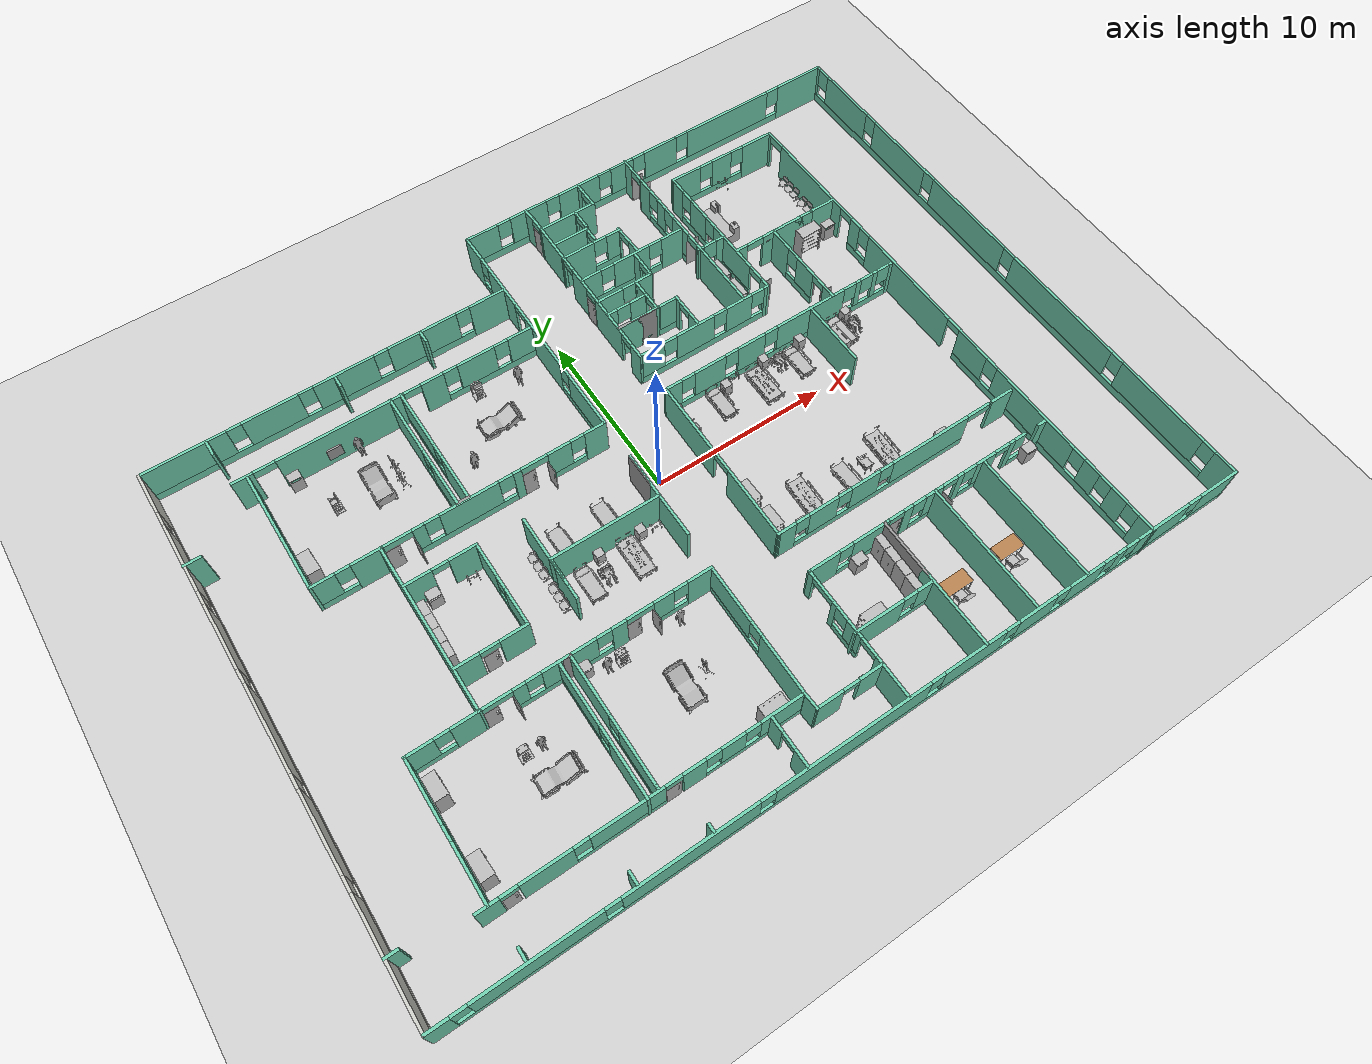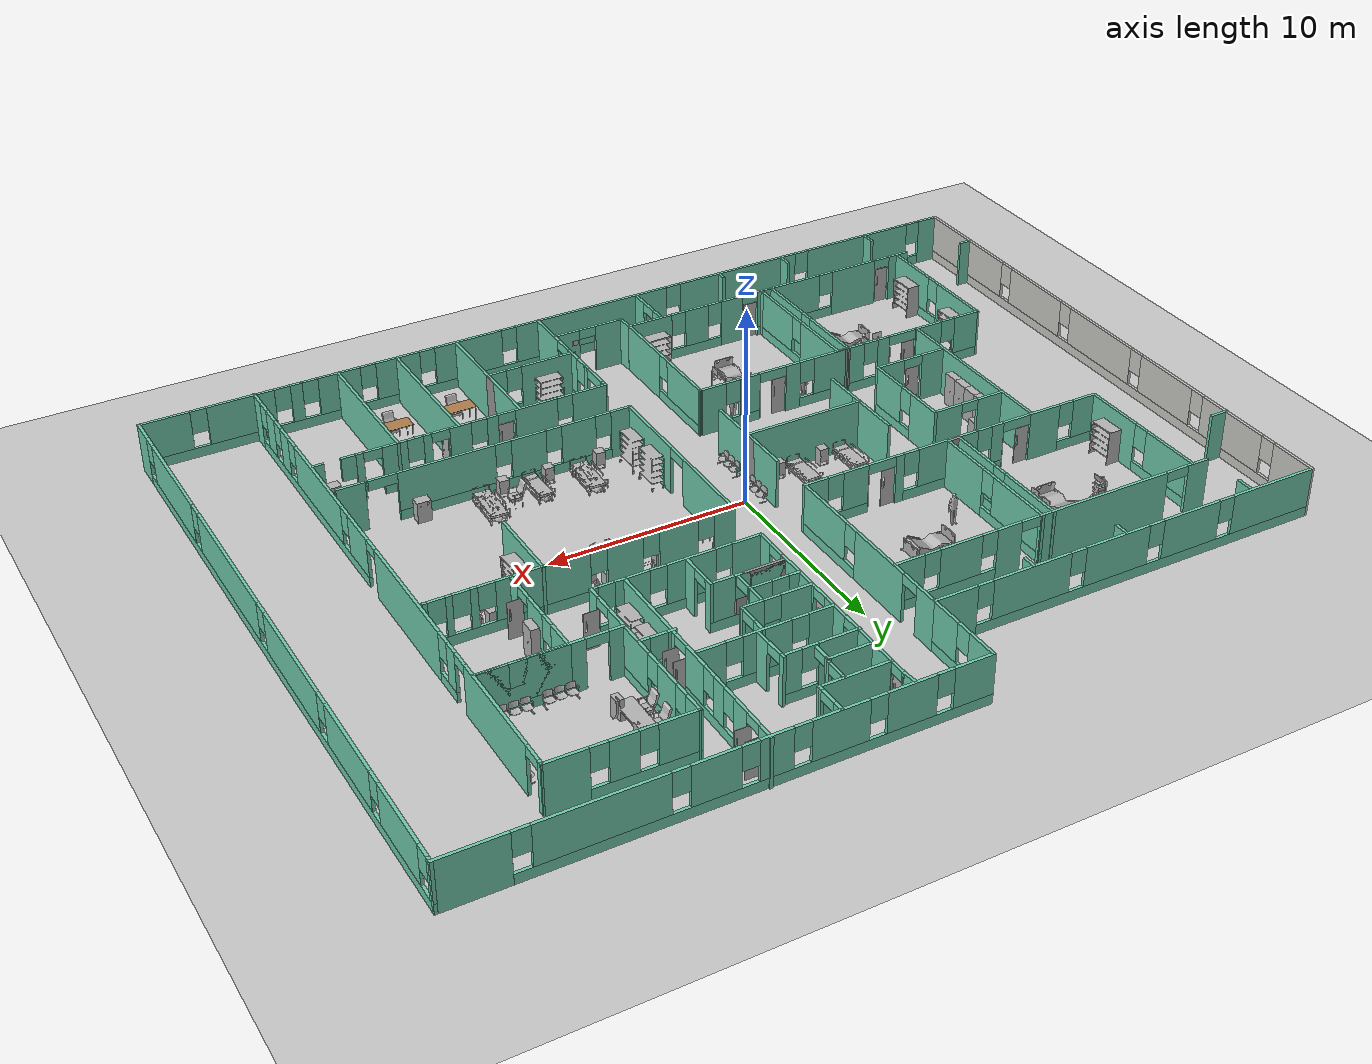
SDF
<sdf version="1.6">
 <world name="default">
  <light name="sun" type="directional">
   <pose>0 0 10 0 -0 0</pose>
   <diffuse>0.8 0.8 0.8 1</diffuse>
   <specular>0.1 0.1 0.1 1</specular>
   <attenuation>
    <range>1000</range>
    <constant>0.9</constant>
    <linear>0.01</linear>
    <quadratic>0.001</quadratic>
   </attenuation>
   <direction>-0.5 0.5 -1</direction>
  </light>
  <model name="ground_plane">
   <static>1</static>
   <link name="link">
    <collision name="collision">
     <geometry><plane><normal>0 0 1</normal><size>100 100</size></plane></geometry>
     <surface><friction><ode><mu>100</mu><mu2>50</mu2></ode></friction></surface>
    </collision>
    <visual name="visual">
     <cast_shadows>0</cast_shadows>
     <geometry><plane><normal>0 0 1</normal><size>100 100</size></plane></geometry>
     <material>
      <script><uri>file://media/materials/scripts/gazebo.material</uri><name>Gazebo/Grey</name></script>
     </material>
    </visual>
   </link>
  </model>
  <gravity>0 0 -9.8</gravity>
  <magnetic_field>6e-06 2.3e-05 -4.2e-05</magnetic_field>
  <atmosphere type="adiabatic"/>
  <physics name="default_physics" default="0" type="ode">
   <max_step_size>0.001</max_step_size>
   <real_time_factor>1</real_time_factor>
   <real_time_update_rate>1000</real_time_update_rate>
  </physics>
  <scene><ambient>0.4 0.4 0.4 1</ambient><background>0.7 0.7 0.7 1</background><shadows>false</shadows></scene>
  <spherical_coordinates>
   <surface_model>EARTH_WGS84</surface_model>
   <latitude_deg>0</latitude_deg>
   <longitude_deg>0</longitude_deg>
   <elevation>0</elevation>
   <heading_deg>0</heading_deg>
  </spherical_coordinates>
  <model name="Hospital_empty">
   <pose>0.7078 0.61575 0 0 -0 0</pose>
   <link name="Wall_0">
    <pose>-22.2855 -2.07101 0 0 0 -1.57157</pose>
    <visual name="Wall_0_Visual_0">
     <pose>-13.6979 0 1.25 0 -0 0</pose>
     <geometry><box><size>2.48559 0.15 2.5</size></box></geometry>
     <material>
      <script><uri>file://media/materials/scripts/gazebo.material</uri><name>Gazebo/CeilingTiled</name></script>
      <ambient>0.435294 0.796078 0.67451 1</ambient>
     </material>
    </visual>
    <collision name="Wall_0_Collision_0">
     <geometry><box><size>2.48559 0.15 2.5</size></box></geometry>
     <pose>-13.6979 0 1.25 0 -0 0</pose>
    </collision>
    <visual name="Wall_0_Visual_1">
     <pose>1.2428 0 0.25 0 -0 0</pose>
     <geometry><box><size>27.3959 0.15 0.5</size></box></geometry>
     <material>
      <script><uri>file://media/materials/scripts/gazebo.material</uri><name>Gazebo/CeilingTiled</name></script>
      <ambient>0.435294 0.796078 0.67451 1</ambient>
     </material>
    </visual>
    <collision name="Wall_0_Collision_1">
     <geometry><box><size>27.3959 0.15 0.5</size></box></geometry>
     <pose>1.2428 0 0.25 0 -0 0</pose>
    </collision>
    <visual name="Wall_0_Visual_2">
     <pose>-9.59967 0 1.5 0 -0 0</pose>
     <geometry><box><size>4.11095 0.15 2</size></box></geometry>
     <material>
      <script><uri>file://media/materials/scripts/gazebo.material</uri><name>Gazebo/CeilingTiled</name></script>
      <ambient>0.435294 0.796078 0.67451 1</ambient>
     </material>
    </visual>
    <collision name="Wall_0_Collision_2">
     <geometry><box><size>4.11095 0.15 2</size></box></geometry>
     <pose>-9.59967 0 1.5 0 -0 0</pose>
    </collision>
    <visual name="Wall_0_Visual_3">
     <pose>-4.86411 0 1.5 0 -0 0</pose>
     <geometry><box><size>3.76016 0.15 2</size></box></geometry>
     <material>
      <script><uri>file://media/materials/scripts/gazebo.material</uri><name>Gazebo/CeilingTiled</name></script>
      <ambient>0.435294 0.796078 0.67451 1</ambient>
     </material>
    </visual>
    <collision name="Wall_0_Collision_3">
     <geometry><box><size>3.76016 0.15 2</size></box></geometry>
     <pose>-4.86411 0 1.5 0 -0 0</pose>
    </collision>
    <visual name="Wall_0_Visual_4">
     <pose>0.23681 0 1.5 0 -0 0</pose>
     <geometry><box><size>4.84168 0.15 2</size></box></geometry>
     <material>
      <script><uri>file://media/materials/scripts/gazebo.material</uri><name>Gazebo/CeilingTiled</name></script>
      <ambient>0.435294 0.796078 0.67451 1</ambient>
     </material>
    </visual>
    <collision name="Wall_0_Collision_4">
     <geometry><box><size>4.84168 0.15 2</size></box></geometry>
     <pose>0.23681 0 1.5 0 -0 0</pose>
    </collision>
    <visual name="Wall_0_Visual_5">
     <pose>5.5901 0 1.5 0 -0 0</pose>
     <geometry><box><size>4.2649 0.15 2</size></box></geometry>
     <material>
      <script><uri>file://media/materials/scripts/gazebo.material</uri><name>Gazebo/CeilingTiled</name></script>
      <ambient>0.435294 0.796078 0.67451 1</ambient>
     </material>
    </visual>
    <collision name="Wall_0_Collision_5">
     <geometry><box><size>4.2649 0.15 2</size></box></geometry>
     <pose>5.5901 0 1.5 0 -0 0</pose>
    </collision>
    <visual name="Wall_0_Visual_6">
     <pose>11.7316 0 1.5 0 -0 0</pose>
     <geometry><box><size>6.41818 0.15 2</size></box></geometry>
     <material>
      <script><uri>file://media/materials/scripts/gazebo.material</uri><name>Gazebo/CeilingTiled</name></script>
      <ambient>0.435294 0.796078 0.67451 1</ambient>
     </material>
    </visual>
    <collision name="Wall_0_Collision_6">
     <geometry><box><size>6.41818 0.15 2</size></box></geometry>
     <pose>11.7316 0 1.5 0 -0 0</pose>
    </collision>
    <visual name="Wall_0_Visual_7">
     <pose>-12.0551 0 1.9 0 -0 0</pose>
     <geometry><box><size>0.8 0.15 1.2</size></box></geometry>
     <material>
      <script><uri>file://media/materials/scripts/gazebo.material</uri><name>Gazebo/CeilingTiled</name></script>
      <ambient>0.435294 0.796078 0.67451 1</ambient>
     </material>
    </visual>
    <collision name="Wall_0_Collision_7">
     <geometry><box><size>0.8 0.15 1.2</size></box></geometry>
     <pose>-12.0551 0 1.9 0 -0 0</pose>
    </collision>
    <visual name="Wall_0_Visual_8">
     <pose>-7.14419 0 1.9 0 -0 0</pose>
     <geometry><box><size>0.8 0.15 1.2</size></box></geometry>
     <material>
      <script><uri>file://media/materials/scripts/gazebo.material</uri><name>Gazebo/CeilingTiled</name></script>
      <ambient>0.435294 0.796078 0.67451 1</ambient>
     </material>
    </visual>
    <collision name="Wall_0_Collision_8">
     <geometry><box><size>0.8 0.15 1.2</size></box></geometry>
     <pose>-7.14419 0 1.9 0 -0 0</pose>
    </collision>
    <visual name="Wall_0_Visual_9">
     <pose>-2.58403 0 1.9 0 -0 0</pose>
     <geometry><box><size>0.8 0.15 1.2</size></box></geometry>
     <material>
      <script><uri>file://media/materials/scripts/gazebo.material</uri><name>Gazebo/CeilingTiled</name></script>
      <ambient>0.435294 0.796078 0.67451 1</ambient>
     </material>
    </visual>
    <collision name="Wall_0_Collision_9">
     <geometry><box><size>0.8 0.15 1.2</size></box></geometry>
     <pose>-2.58403 0 1.9 0 -0 0</pose>
    </collision>
    <visual name="Wall_0_Visual_10">
     <pose>3.05765 0 1.9 0 -0 0</pose>
     <geometry><box><size>0.8 0.15 1.2</size></box></geometry>
     <material>
      <script><uri>file://media/materials/scripts/gazebo.material</uri><name>Gazebo/CeilingTiled</name></script>
      <ambient>0.435294 0.796078 0.67451 1</ambient>
     </material>
    </visual>
    <collision name="Wall_0_Collision_10">
     <geometry><box><size>0.8 0.15 1.2</size></box></geometry>
     <pose>3.05765 0 1.9 0 -0 0</pose>
    </collision>
    <visual name="Wall_0_Visual_11">
     <pose>8.12255 0 1.9 0 -0 0</pose>
     <geometry><box><size>0.8 0.15 1.2</size></box></geometry>
     <material>
      <script><uri>file://media/materials/scripts/gazebo.material</uri><name>Gazebo/CeilingTiled</name></script>
      <ambient>0.435294 0.796078 0.67451 1</ambient>
     </material>
    </visual>
    <collision name="Wall_0_Collision_11">
     <geometry><box><size>0.8 0.15 1.2</size></box></geometry>
     <pose>8.12255 0 1.9 0 -0 0</pose>
    </collision>
   </link>
   <link name="Wall_1">
    <pose>0.002999 -16.937 0 0 -0 0</pose>
    <visual name="Wall_1_Visual_0">
     <pose>-21.7746 0 1.25 0 -0 0</pose>
     <geometry><box><size>1.20077 0.15 2.5</size></box></geometry>
     <material>
      <script><uri>file://media/materials/scripts/gazebo.material</uri><name>Gazebo/Grey</name></script>
      <ambient>0.435294 0.796078 0.67451 1</ambient>
     </material>
    </visual>
    <collision name="Wall_1_Collision_0">
     <geometry><box><size>1.20077 0.15 2.5</size></box></geometry>
     <pose>-21.7746 0 1.25 0 -0 0</pose>
    </collision>
    <visual name="Wall_1_Visual_1">
     <pose>0.600387 0 0.25 0 -0 0</pose>
     <geometry><box><size>43.5492 0.15 0.5</size></box></geometry>
     <material>
      <script><uri>file://media/materials/scripts/gazebo.material</uri><name>Gazebo/Grey</name></script>
      <ambient>0.435294 0.796078 0.67451 1</ambient>
     </material>
    </visual>
    <collision name="Wall_1_Collision_1">
     <geometry><box><size>43.5492 0.15 0.5</size></box></geometry>
     <pose>0.600387 0 0.25 0 -0 0</pose>
    </collision>
    <visual name="Wall_1_Visual_2">
     <pose>-17.2192 0 1.5 0 -0 0</pose>
     <geometry><box><size>6.31 0.15 2</size></box></geometry>
     <material>
      <script><uri>file://media/materials/scripts/gazebo.material</uri><name>Gazebo/Grey</name></script>
      <ambient>0.435294 0.796078 0.67451 1</ambient>
     </material>
    </visual>
    <collision name="Wall_1_Collision_2">
     <geometry><box><size>6.31 0.15 2</size></box></geometry>
     <pose>-17.2192 0 1.5 0 -0 0</pose>
    </collision>
    <visual name="Wall_1_Visual_3">
     <pose>-9.77173 0 1.5 0 -0 0</pose>
     <geometry><box><size>6.985 0.15 2</size></box></geometry>
     <material>
      <script><uri>file://media/materials/scripts/gazebo.material</uri><name>Gazebo/Grey</name></script>
      <ambient>0.435294 0.796078 0.67451 1</ambient>
     </material>
    </visual>
    <collision name="Wall_1_Collision_3">
     <geometry><box><size>6.985 0.15 2</size></box></geometry>
     <pose>-9.77173 0 1.5 0 -0 0</pose>
    </collision>
    <visual name="Wall_1_Visual_4">
     <pose>-1.19923 0 1.5 0 -0 0</pose>
     <geometry><box><size>8.56 0.15 2</size></box></geometry>
     <material>
      <script><uri>file://media/materials/scripts/gazebo.material</uri><name>Gazebo/Grey</name></script>
      <ambient>0.435294 0.796078 0.67451 1</ambient>
     </material>
    </visual>
    <collision name="Wall_1_Collision_4">
     <geometry><box><size>8.56 0.15 2</size></box></geometry>
     <pose>-1.19923 0 1.5 0 -0 0</pose>
    </collision>
    <visual name="Wall_1_Visual_5">
     <pose>5.68577 0 1.5 0 -0 0</pose>
     <geometry><box><size>3.61 0.15 2</size></box></geometry>
     <material>
      <script><uri>file://media/materials/scripts/gazebo.material</uri><name>Gazebo/Grey</name></script>
      <ambient>0.435294 0.796078 0.67451 1</ambient>
     </material>
    </visual>
    <collision name="Wall_1_Collision_5">
     <geometry><box><size>3.61 0.15 2</size></box></geometry>
     <pose>5.68577 0 1.5 0 -0 0</pose>
    </collision>
    <visual name="Wall_1_Visual_6">
     <pose>9.44327 0 1.5 0 -0 0</pose>
     <geometry><box><size>2.305 0.15 2</size></box></geometry>
     <material>
      <script><uri>file://media/materials/scripts/gazebo.material</uri><name>Gazebo/Grey</name></script>
      <ambient>0.435294 0.796078 0.67451 1</ambient>
     </material>
    </visual>
    <collision name="Wall_1_Collision_6">
     <geometry><box><size>2.305 0.15 2</size></box></geometry>
     <pose>9.44327 0 1.5 0 -0 0</pose>
    </collision>
    <visual name="Wall_1_Visual_7">
     <pose>12.4808 0 1.5 0 -0 0</pose>
     <geometry><box><size>2.17 0.15 2</size></box></geometry>
     <material>
      <script><uri>file://media/materials/scripts/gazebo.material</uri><name>Gazebo/Grey</name></script>
      <ambient>0.435294 0.796078 0.67451 1</ambient>
     </material>
    </visual>
    <collision name="Wall_1_Collision_7">
     <geometry><box><size>2.17 0.15 2</size></box></geometry>
     <pose>12.4808 0 1.5 0 -0 0</pose>
    </collision>
    <visual name="Wall_1_Visual_8">
     <pose>14.6633 0 1.5 0 -0 0</pose>
     <geometry><box><size>0.595 0.15 2</size></box></geometry>
     <material>
      <script><uri>file://media/materials/scripts/gazebo.material</uri><name>Gazebo/Grey</name></script>
      <ambient>0.435294 0.796078 0.67451 1</ambient>
     </material>
    </visual>
    <collision name="Wall_1_Collision_8">
     <geometry><box><size>0.595 0.15 2</size></box></geometry>
     <pose>14.6633 0 1.5 0 -0 0</pose>
    </collision>
    <visual name="Wall_1_Visual_9">
     <pose>17.4308 0 1.5 0 -0 0</pose>
     <geometry><box><size>3.34 0.15 2</size></box></geometry>
     <material>
      <script><uri>file://media/materials/scripts/gazebo.material</uri><name>Gazebo/Grey</name></script>
      <ambient>0.435294 0.796078 0.67451 1</ambient>
     </material>
    </visual>
    <collision name="Wall_1_Collision_9">
     <geometry><box><size>3.34 0.15 2</size></box></geometry>
     <pose>17.4308 0 1.5 0 -0 0</pose>
    </collision>
    <visual name="Wall_1_Visual_10">
     <pose>21.1379 0 1.5 0 -0 0</pose>
     <geometry><box><size>2.47423 0.15 2</size></box></geometry>
     <material>
      <script><uri>file://media/materials/scripts/gazebo.material</uri><name>Gazebo/Grey</name></script>
      <ambient>0.435294 0.796078 0.67451 1</ambient>
     </material>
    </visual>
    <collision name="Wall_1_Collision_10">
     <geometry><box><size>2.47423 0.15 2</size></box></geometry>
     <pose>21.1379 0 1.5 0 -0 0</pose>
    </collision>
    <visual name="Wall_1_Visual_11">
     <pose>-20.7742 0 1.9 0 -0 0</pose>
     <geometry><box><size>0.8 0.15 1.2</size></box></geometry>
     <material>
      <script><uri>file://media/materials/scripts/gazebo.material</uri><name>Gazebo/Grey</name></script>
      <ambient>0.435294 0.796078 0.67451 1</ambient>
     </material>
    </visual>
    <collision name="Wall_1_Collision_11">
     <geometry><box><size>0.8 0.15 1.2</size></box></geometry>
     <pose>-20.7742 0 1.9 0 -0 0</pose>
    </collision>
    <visual name="Wall_1_Visual_12">
     <pose>-13.6642 0 1.9 0 -0 0</pose>
     <geometry><box><size>0.8 0.15 1.2</size></box></geometry>
     <material>
      <script><uri>file://media/materials/scripts/gazebo.material</uri><name>Gazebo/Grey</name></script>
      <ambient>0.435294 0.796078 0.67451 1</ambient>
     </material>
    </visual>
    <collision name="Wall_1_Collision_12">
     <geometry><box><size>0.8 0.15 1.2</size></box></geometry>
     <pose>-13.6642 0 1.9 0 -0 0</pose>
    </collision>
    <visual name="Wall_1_Visual_13">
     <pose>-5.87923 0 1.9 0 -0 0</pose>
     <geometry><box><size>0.8 0.15 1.2</size></box></geometry>
     <material>
      <script><uri>file://media/materials/scripts/gazebo.material</uri><name>Gazebo/Grey</name></script>
      <ambient>0.435294 0.796078 0.67451 1</ambient>
     </material>
    </visual>
    <collision name="Wall_1_Collision_13">
     <geometry><box><size>0.8 0.15 1.2</size></box></geometry>
     <pose>-5.87923 0 1.9 0 -0 0</pose>
    </collision>
    <visual name="Wall_1_Visual_14">
     <pose>3.48077 0 1.9 0 -0 0</pose>
     <geometry><box><size>0.8 0.15 1.2</size></box></geometry>
     <material>
      <script><uri>file://media/materials/scripts/gazebo.material</uri><name>Gazebo/Grey</name></script>
      <ambient>0.435294 0.796078 0.67451 1</ambient>
     </material>
    </visual>
    <collision name="Wall_1_Collision_14">
     <geometry><box><size>0.8 0.15 1.2</size></box></geometry>
     <pose>3.48077 0 1.9 0 -0 0</pose>
    </collision>
    <visual name="Wall_1_Visual_15">
     <pose>7.89077 0 1.9 0 -0 0</pose>
     <geometry><box><size>0.8 0.15 1.2</size></box></geometry>
     <material>
      <script><uri>file://media/materials/scripts/gazebo.material</uri><name>Gazebo/Grey</name></script>
      <ambient>0.435294 0.796078 0.67451 1</ambient>
     </material>
    </visual>
    <collision name="Wall_1_Collision_15">
     <geometry><box><size>0.8 0.15 1.2</size></box></geometry>
     <pose>7.89077 0 1.9 0 -0 0</pose>
    </collision>
    <visual name="Wall_1_Visual_16">
     <pose>10.9958 0 1.9 0 -0 0</pose>
     <geometry><box><size>0.8 0.15 1.2</size></box></geometry>
     <material>
      <script><uri>file://media/materials/scripts/gazebo.material</uri><name>Gazebo/Grey</name></script>
      <ambient>0.435294 0.796078 0.67451 1</ambient>
     </material>
    </visual>
    <collision name="Wall_1_Collision_16">
     <geometry><box><size>0.8 0.15 1.2</size></box></geometry>
     <pose>10.9958 0 1.9 0 -0 0</pose>
    </collision>
    <visual name="Wall_1_Visual_17">
     <pose>13.9658 0 1.9 0 -0 0</pose>
     <geometry><box><size>0.8 0.15 1.2</size></box></geometry>
     <material>
      <script><uri>file://media/materials/scripts/gazebo.material</uri><name>Gazebo/Grey</name></script>
      <ambient>0.435294 0.796078 0.67451 1</ambient>
     </material>
    </visual>
    <collision name="Wall_1_Collision_17">
     <geometry><box><size>0.8 0.15 1.2</size></box></geometry>
     <pose>13.9658 0 1.9 0 -0 0</pose>
    </collision>
    <visual name="Wall_1_Visual_18">
     <pose>15.3608 0 1.9 0 -0 0</pose>
     <geometry><box><size>0.8 0.15 1.2</size></box></geometry>
     <material>
      <script><uri>file://media/materials/scripts/gazebo.material</uri><name>Gazebo/Grey</name></script>
      <ambient>0.435294 0.796078 0.67451 1</ambient>
     </material>
    </visual>
    <collision name="Wall_1_Collision_18">
     <geometry><box><size>0.8 0.15 1.2</size></box></geometry>
     <pose>15.3608 0 1.9 0 -0 0</pose>
    </collision>
    <visual name="Wall_1_Visual_19">
     <pose>19.5008 0 1.9 0 -0 0</pose>
     <geometry><box><size>0.8 0.15 1.2</size></box></geometry>
     <material>
      <script><uri>file://media/materials/scripts/gazebo.material</uri><name>Gazebo/Grey</name></script>
      <ambient>0.435294 0.796078 0.67451 1</ambient>
     </material>
    </visual>
    <collision name="Wall_1_Collision_19">
     <geometry><box><size>0.8 0.15 1.2</size></box></geometry>
     <pose>19.5008 0 1.9 0 -0 0</pose>
    </collision>
   </link>
   <link name="Wall_100">
    <pose>3.70852 12.8706 0 0 -0 0</pose>
    <visual name="Wall_100_Visual_0">
     <pose>-0.873017 0 1.25 0 -0 0</pose>
     <geometry><box><size>2.00397 0.15 2.5</size></box></geometry>
     <material>
      <script><uri>file://media/materials/scripts/gazebo.material</uri><name>Gazebo/Grey</name></script>
      <ambient>0.435294 0.796078 0.67451 1</ambient>
     </material>
    </visual>
    <collision name="Wall_100_Collision_0">
     <geometry><box><size>2.00397 0.15 2.5</size></box></geometry>
     <pose>-0.873017 0 1.25 0 -0 0</pose>
    </collision>
    <visual name="Wall_100_Visual_1">
     <pose>1.00198 0 0.25 0 -0 0</pose>
     <geometry><box><size>1.74603 0.15 0.5</size></box></geometry>
     <material>
      <script><uri>file://media/materials/scripts/gazebo.material</uri><name>Gazebo/Grey</name></script>
      <ambient>0.435294 0.796078 0.67451 1</ambient>
     </material>
    </visual>
    <collision name="Wall_100_Collision_1">
     <geometry><box><size>1.74603 0.15 0.5</size></box></geometry>
     <pose>1.00198 0 0.25 0 -0 0</pose>
    </collision>
    <visual name="Wall_100_Visual_2">
     <pose>1.40198 0 1.5 0 -0 0</pose>
     <geometry><box><size>0.946034 0.15 2</size></box></geometry>
     <material>
      <script><uri>file://media/materials/scripts/gazebo.material</uri><name>Gazebo/Grey</name></script>
      <ambient>0.435294 0.796078 0.67451 1</ambient>
     </material>
    </visual>
    <collision name="Wall_100_Collision_2">
     <geometry><box><size>0.946034 0.15 2</size></box></geometry>
     <pose>1.40198 0 1.5 0 -0 0</pose>
    </collision>
    <visual name="Wall_100_Visual_3">
     <pose>0.528966 0 1.9 0 -0 0</pose>
     <geometry><box><size>0.8 0.15 1.2</size></box></geometry>
     <material>
      <script><uri>file://media/materials/scripts/gazebo.material</uri><name>Gazebo/Grey</name></script>
      <ambient>0.435294 0.796078 0.67451 1</ambient>
     </material>
    </visual>
    <collision name="Wall_100_Collision_3">
     <geometry><box><size>0.8 0.15 1.2</size></box></geometry>
     <pose>0.528966 0 1.9 0 -0 0</pose>
    </collision>
   </link>
   <link name="Wall_101">
    <pose>5.53676 11.9973 0 0 0 -1.5414</pose>
    <visual name="Wall_101_Visual_0">
     <pose>-0.894743 0 1.25 0 -0 0</pose>
     <geometry><box><size>0.281917 0.15 2.5</size></box></geometry>
     <material>
      <script><uri>file://media/materials/scripts/gazebo.material</uri><name>Gazebo/Grey</name></script>
      <ambient>0.435294 0.796078 0.67451 1</ambient>
     </material>
    </visual>
    <collision name="Wall_101_Collision_0">
     <geometry><box><size>0.281917 0.15 2.5</size></box></geometry>
     <pose>-0.894743 0 1.25 0 -0 0</pose>
    </collision>
    <visual name="Wall_101_Visual_1">
     <pose>0.590959 0 1.25 0 -0 0</pose>
     <geometry><box><size>0.889485 0.15 2.5</size></box></geometry>
     <material>
      <script><uri>file://media/materials/scripts/gazebo.material</uri><name>Gazebo/Grey</name></script>
      <ambient>0.435294 0.796078 0.67451 1</ambient>
     </material>
    </visual>
    <collision name="Wall_101_Collision_1">
     <geometry><box><size>0.889485 0.15 2.5</size></box></geometry>
     <pose>0.590959 0 1.25 0 -0 0</pose>
    </collision>
    <visual name="Wall_101_Visual_2">
     <pose>-0.303784 0 2.25 0 -0 0</pose>
     <geometry><box><size>0.9 0.15 0.5</size></box></geometry>
     <material>
      <script><uri>file://media/materials/scripts/gazebo.material</uri><name>Gazebo/Grey</name></script>
      <ambient>0.435294 0.796078 0.67451 1</ambient>
     </material>
    </visual>
    <collision name="Wall_101_Collision_2">
     <geometry><box><size>0.9 0.15 0.5</size></box></geometry>
     <pose>-0.303784 0 2.25 0 -0 0</pose>
    </collision>
   </link>
   <link name="Wall_103">
    <pose>5.15177 11.0095 0 0 -0 3.14159</pose>
    <visual name="Wall_103_Visual_0">
     <pose>-2.56982 0 1.25 0 -0 0</pose>
     <geometry><box><size>1.36037 0.15 2.5</size></box></geometry>
     <material>
      <script><uri>file://media/materials/scripts/gazebo.material</uri><name>Gazebo/Grey</name></script>
      <ambient>0.435294 0.796078 0.67451 1</ambient>
     </material>
    </visual>
    <collision name="Wall_103_Collision_0">
     <geometry><box><size>1.36037 0.15 2.5</size></box></geometry>
     <pose>-2.56982 0 1.25 0 -0 0</pose>
    </collision>
    <visual name="Wall_103_Visual_1">
     <pose>0.680183 0 0.25 0 -0 0</pose>
     <geometry><box><size>5.13964 0.15 0.5</size></box></geometry>
     <material>
      <script><uri>file://media/materials/scripts/gazebo.material</uri><name>Gazebo/Grey</name></script>
      <ambient>0.435294 0.796078 0.67451 1</ambient>
     </material>
    </visual>
    <collision name="Wall_103_Collision_1">
     <geometry><box><size>5.13964 0.15 0.5</size></box></geometry>
     <pose>0.680183 0 0.25 0 -0 0</pose>
    </collision>
    <visual name="Wall_103_Visual_2">
     <pose>0.054099 0 1.5 0 -0 0</pose>
     <geometry><box><size>2.28747 0.15 2</size></box></geometry>
     <material>
      <script><uri>file://media/materials/scripts/gazebo.material</uri><name>Gazebo/Grey</name></script>
      <ambient>0.435294 0.796078 0.67451 1</ambient>
     </material>
    </visual>
    <collision name="Wall_103_Collision_2">
     <geometry><box><size>2.28747 0.15 2</size></box></geometry>
     <pose>0.054099 0 1.5 0 -0 0</pose>
    </collision>
    <visual name="Wall_103_Visual_3">
     <pose>2.62392 0 1.5 0 -0 0</pose>
     <geometry><box><size>1.25217 0.15 2</size></box></geometry>
     <material>
      <script><uri>file://media/materials/scripts/gazebo.material</uri><name>Gazebo/Grey</name></script>
      <ambient>0.435294 0.796078 0.67451 1</ambient>
     </material>
    </visual>
    <collision name="Wall_103_Collision_3">
     <geometry><box><size>1.25217 0.15 2</size></box></geometry>
     <pose>2.62392 0 1.5 0 -0 0</pose>
    </collision>
    <visual name="Wall_103_Visual_4">
     <pose>-1.48964 0 1.9 0 -0 0</pose>
     <geometry><box><size>0.8 0.15 1.2</size></box></geometry>
     <material>
      <script><uri>file://media/materials/scripts/gazebo.material</uri><name>Gazebo/Grey</name></script>
      <ambient>0.435294 0.796078 0.67451 1</ambient>
     </material>
    </visual>
    <collision name="Wall_103_Collision_4">
     <geometry><box><size>0.8 0.15 1.2</size></box></geometry>
     <pose>-1.48964 0 1.9 0 -0 0</pose>
    </collision>
    <visual name="Wall_103_Visual_5">
     <pose>1.59783 0 1.9 0 -0 0</pose>
     <geometry><box><size>0.8 0.15 1.2</size></box></geometry>
     <material>
      <script><uri>file://media/materials/scripts/gazebo.material</uri><name>Gazebo/Grey</name></script>
      <ambient>0.435294 0.796078 0.67451 1</ambient>
     </material>
    </visual>
    <collision name="Wall_103_Collision_5">
     <geometry><box><size>0.8 0.15 1.2</size></box></geometry>
     <pose>1.59783 0 1.9 0 -0 0</pose>
    </collision>
   </link>
   <link name="Wall_105">
    <pose>5.291 10.1575 0 0 0 -1.58367</pose>
    <visual name="Wall_105_Visual_0">
     <pose>-0.562111 0 1.25 0 -0 0</pose>
     <geometry><box><size>0.734515 0.15 2.5</size></box></geometry>
     <material>
      <script><uri>file://media/materials/scripts/gazebo.material</uri><name>Gazebo/Grey</name></script>
      <ambient>0.435294 0.796078 0.67451 1</ambient>
     </material>
    </visual>
    <collision name="Wall_105_Collision_0">
     <geometry><box><size>0.734515 0.15 2.5</size></box></geometry>
     <pose>-0.562111 0 1.25 0 -0 0</pose>
    </collision>
    <visual name="Wall_105_Visual_1">
     <pose>0.817258 0 1.25 0 -0 0</pose>
     <geometry><box><size>0.224223 0.15 2.5</size></box></geometry>
     <material>
      <script><uri>file://media/materials/scripts/gazebo.material</uri><name>Gazebo/Grey</name></script>
      <ambient>0.435294 0.796078 0.67451 1</ambient>
     </material>
    </visual>
    <collision name="Wall_105_Collision_1">
     <geometry><box><size>0.224223 0.15 2.5</size></box></geometry>
     <pose>0.817258 0 1.25 0 -0 0</pose>
    </collision>
    <visual name="Wall_105_Visual_2">
     <pose>0.255146 0 2.25 0 -0 0</pose>
     <geometry><box><size>0.9 0.15 0.5</size></box></geometry>
     <material>
      <script><uri>file://media/materials/scripts/gazebo.material</uri><name>Gazebo/Grey</name></script>
      <ambient>0.435294 0.796078 0.67451 1</ambient>
     </material>
    </visual>
    <collision name="Wall_105_Collision_2">
     <geometry><box><size>0.9 0.15 0.5</size></box></geometry>
     <pose>0.255146 0 2.25 0 -0 0</pose>
    </collision>
   </link>
   <link name="Wall_106">
    <pose>3.616 9.30314 0 0 -0 3.1415</pose>
    <visual name="Wall_106_Visual_0">
     <pose>-1.18986 0 1.25 0 -0 0</pose>
     <geometry><box><size>1.09829 0.15 2.5</size></box></geometry>
     <material>
      <script><uri>file://media/materials/scripts/gazebo.material</uri><name>Gazebo/Grey</name></script>
      <ambient>0.435294 0.796078 0.67451 1</ambient>
     </material>
    </visual>
    <collision name="Wall_106_Collision_0">
     <geometry><box><size>1.09829 0.15 2.5</size></box></geometry>
     <pose>-1.18986 0 1.25 0 -0 0</pose>
    </collision>
    <visual name="Wall_106_Visual_1">
     <pose>0.549144 0 0.25 0 -0 0</pose>
     <geometry><box><size>2.37971 0.15 0.5</size></box></geometry>
     <material>
      <script><uri>file://media/materials/scripts/gazebo.material</uri><name>Gazebo/Grey</name></script>
      <ambient>0.435294 0.796078 0.67451 1</ambient>
     </material>
    </visual>
    <collision name="Wall_106_Collision_1">
     <geometry><box><size>2.37971 0.15 0.5</size></box></geometry>
     <pose>0.549144 0 0.25 0 -0 0</pose>
    </collision>
    <visual name="Wall_106_Visual_2">
     <pose>0.949144 0 1.5 0 -0 0</pose>
     <geometry><box><size>1.57971 0.15 2</size></box></geometry>
     <material>
      <script><uri>file://media/materials/scripts/gazebo.material</uri><name>Gazebo/Grey</name></script>
      <ambient>0.435294 0.796078 0.67451 1</ambient>
     </material>
    </visual>
    <collision name="Wall_106_Collision_2">
     <geometry><box><size>1.57971 0.15 2</size></box></geometry>
     <pose>0.949144 0 1.5 0 -0 0</pose>
    </collision>
    <visual name="Wall_106_Visual_3">
     <pose>-0.240712 0 1.9 0 -0 0</pose>
     <geometry><box><size>0.8 0.15 1.2</size></box></geometry>
     <material>
      <script><uri>file://media/materials/scripts/gazebo.material</uri><name>Gazebo/Grey</name></script>
      <ambient>0.435294 0.796078 0.67451 1</ambient>
     </material>
    </visual>
    <collision name="Wall_106_Collision_3">
     <geometry><box><size>0.8 0.15 1.2</size></box></geometry>
     <pose>-0.240712 0 1.9 0 -0 0</pose>
    </collision>
   </link>
   <link name="Wall_108">
    <pose>3.12156 8.29555 0 0 0 -0.004715</pose>
    <visual name="Wall_108_Visual_0">
     <pose>-0.954583 0 1.25 0 -0 0</pose>
     <geometry><box><size>0.60173 0.15 2.5</size></box></geometry>
     <material>
      <script><uri>file://media/materials/scripts/gazebo.material</uri><name>Gazebo/Grey</name></script>
      <ambient>0.435294 0.796078 0.67451 1</ambient>
     </material>
    </visual>
    <collision name="Wall_108_Collision_0">
     <geometry><box><size>0.60173 0.15 2.5</size></box></geometry>
     <pose>-0.954583 0 1.25 0 -0 0</pose>
    </collision>
    <visual name="Wall_108_Visual_1">
     <pose>0.300865 0 0.25 0 -0 0</pose>
     <geometry><box><size>1.90917 0.15 0.5</size></box></geometry>
     <material>
      <script><uri>file://media/materials/scripts/gazebo.material</uri><name>Gazebo/Grey</name></script>
      <ambient>0.435294 0.796078 0.67451 1</ambient>
     </material>
    </visual>
    <collision name="Wall_108_Collision_1">
     <geometry><box><size>1.90917 0.15 0.5</size></box></geometry>
     <pose>0.300865 0 0.25 0 -0 0</pose>
    </collision>
    <visual name="Wall_108_Visual_2">
     <pose>0.700865 0 1.5 0 -0 0</pose>
     <geometry><box><size>1.10916 0.15 2</size></box></geometry>
     <material>
      <script><uri>file://media/materials/scripts/gazebo.material</uri><name>Gazebo/Grey</name></script>
      <ambient>0.435294 0.796078 0.67451 1</ambient>
     </material>
    </visual>
    <collision name="Wall_108_Collision_2">
     <geometry><box><size>1.10916 0.15 2</size></box></geometry>
     <pose>0.700865 0 1.5 0 -0 0</pose>
    </collision>
    <visual name="Wall_108_Visual_3">
     <pose>-0.253718 0 1.9 0 -0 0</pose>
     <geometry><box><size>0.8 0.15 1.2</size></box></geometry>
     <material>
      <script><uri>file://media/materials/scripts/gazebo.material</uri><name>Gazebo/Grey</name></script>
      <ambient>0.435294 0.796078 0.67451 1</ambient>
     </material>
    </visual>
    <collision name="Wall_108_Collision_3">
     <geometry><box><size>0.8 0.15 1.2</size></box></geometry>
     <pose>-0.253718 0 1.9 0 -0 0</pose>
    </collision>
   </link>
   <link name="Wall_109">
    <pose>4.302 7.75099 0 0 0 -1.5708</pose>
    <visual name="Wall_109_Visual_0">
     <pose>-0.512428 0 1.25 0 -0 0</pose>
     <geometry><box><size>0.203406 0.15 2.5</size></box></geometry>
     <material>
      <script><uri>file://media/materials/scripts/gazebo.material</uri><name>Gazebo/Grey</name></script>
      <ambient>0.435294 0.796078 0.67451 1</ambient>
     </material>
    </visual>
    <collision name="Wall_109_Collision_0">
     <geometry><box><size>0.203406 0.15 2.5</size></box></geometry>
     <pose>-0.512428 0 1.25 0 -0 0</pose>
    </collision>
    <visual name="Wall_109_Visual_1">
     <pose>0.551703 0 1.25 0 -0 0</pose>
     <geometry><box><size>0.124856 0.15 2.5</size></box></geometry>
     <material>
      <script><uri>file://media/materials/scripts/gazebo.material</uri><name>Gazebo/Grey</name></script>
      <ambient>0.435294 0.796078 0.67451 1</ambient>
     </material>
    </visual>
    <collision name="Wall_109_Collision_1">
     <geometry><box><size>0.124856 0.15 2.5</size></box></geometry>
     <pose>0.551703 0 1.25 0 -0 0</pose>
    </collision>
    <visual name="Wall_109_Visual_2">
     <pose>0.039275 0 2.25 0 -0 0</pose>
     <geometry><box><size>0.9 0.15 0.5</size></box></geometry>
     <material>
      <script><uri>file://media/materials/scripts/gazebo.material</uri><name>Gazebo/Grey</name></script>
      <ambient>0.435294 0.796078 0.67451 1</ambient>
     </material>
    </visual>
    <collision name="Wall_109_Collision_2">
     <geometry><box><size>0.9 0.15 0.5</size></box></geometry>
     <pose>0.039275 0 2.25 0 -0 0</pose>
    </collision>
   </link>
   <link name="Wall_11">
    <collision name="Wall_11_Collision">
     <geometry><box><size>0.75 0.15 2.5</size></box></geometry>
     <pose>0 0 1.25 0 -0 0</pose>
    </collision>
    <visual name="Wall_11_Visual">
     <pose>0 0 1.25 0 -0 0</pose>
     <geometry><box><size>0.75 0.15 2.5</size></box></geometry>
     <material>
      <script><uri>file://media/materials/scripts/gazebo.material</uri><name>Gazebo/Grey</name></script>
      <ambient>0.435294 0.796078 0.67451 1</ambient>
     </material>
    </visual>
    <pose>-11.779 12.417 0 0 0 -1.5708</pose>
   </link>
   <link name="Wall_110">
    <collision name="Wall_110_Collision">
     <geometry><box><size>2.5 0.15 2.5</size></box></geometry>
     <pose>0 0 1.25 0 -0 0</pose>
    </collision>
    <visual name="Wall_110_Visual">
     <pose>0 0 1.25 0 -0 0</pose>
     <geometry><box><size>2.5 0.15 2.5</size></box></geometry>
     <material>
      <script><uri>file://media/materials/scripts/gazebo.material</uri><name>Gazebo/Grey</name></script>
      <ambient>1 1 1 1</ambient>
     </material>
    </visual>
    <pose>3.127 7.21199 0 0 -0 3.14159</pose>
   </link>
   <link name="Wall_111">
    <pose>3.752 7.21199 0 0 -0 0</pose>
    <visual name="Wall_111_Visual_0">
     <pose>-0.993085 0 1.25 0 -0 0</pose>
     <geometry><box><size>1.76383 0.15 2.5</size></box></geometry>
     <material>
      <script><uri>file://media/materials/scripts/gazebo.material</uri><name>Gazebo/Grey</name></script>
      <ambient>0.435294 0.796078 0.67451 1</ambient>
     </material>
    </visual>
    <collision name="Wall_111_Collision_0">
     <geometry><box><size>1.76383 0.15 2.5</size></box></geometry>
     <pose>-0.993085 0 1.25 0 -0 0</pose>
    </collision>
    <visual name="Wall_111_Visual_1">
     <pose>0.881915 0 0.25 0 -0 0</pose>
     <geometry><box><size>1.98617 0.15 0.5</size></box></geometry>
     <material>
      <script><uri>file://media/materials/scripts/gazebo.material</uri><name>Gazebo/Grey</name></script>
      <ambient>0.435294 0.796078 0.67451 1</ambient>
     </material>
    </visual>
    <collision name="Wall_111_Collision_1">
     <geometry><box><size>1.98617 0.15 0.5</size></box></geometry>
     <pose>0.881915 0 0.25 0 -0 0</pose>
    </collision>
    <visual name="Wall_111_Visual_2">
     <pose>1.28191 0 1.5 0 -0 0</pose>
     <geometry><box><size>1.18617 0.15 2</size></box></geometry>
     <material>
      <script><uri>file://media/materials/scripts/gazebo.material</uri><name>Gazebo/Grey</name></script>
      <ambient>0.435294 0.796078 0.67451 1</ambient>
     </material>
    </visual>
    <collision name="Wall_111_Collision_2">
     <geometry><box><size>1.18617 0.15 2</size></box></geometry>
     <pose>1.28191 0 1.5 0 -0 0</pose>
    </collision>
    <visual name="Wall_111_Visual_3">
     <pose>0.28883 0 1.9 0 -0 0</pose>
     <geometry><box><size>0.8 0.15 1.2</size></box></geometry>
     <material>
      <script><uri>file://media/materials/scripts/gazebo.material</uri><name>Gazebo/Grey</name></script>
      <ambient>0.435294 0.796078 0.67451 1</ambient>
     </material>
    </visual>
    <collision name="Wall_111_Collision_3">
     <geometry><box><size>0.8 0.15 1.2</size></box></geometry>
     <pose>0.28883 0 1.9 0 -0 0</pose>
    </collision>
   </link>
   <link name="Wall_112">
    <pose>5.552 6.16199 0 0 0 -1.5708</pose>
    <visual name="Wall_112_Visual_0">
     <pose>-0.900897 0 1.25 0 -0 0</pose>
     <geometry><box><size>0.448206 0.15 2.5</size></box></geometry>
     <material>
      <script><uri>file://media/materials/scripts/gazebo.material</uri><name>Gazebo/Grey</name></script>
      <ambient>0.435294 0.796078 0.67451 1</ambient>
     </material>
    </visual>
    <collision name="Wall_112_Collision_0">
     <geometry><box><size>0.448206 0.15 2.5</size></box></geometry>
     <pose>-0.900897 0 1.25 0 -0 0</pose>
    </collision>
    <visual name="Wall_112_Visual_1">
     <pose>0.674103 0 1.25 0 -0 0</pose>
     <geometry><box><size>0.901794 0.15 2.5</size></box></geometry>
     <material>
      <script><uri>file://media/materials/scripts/gazebo.material</uri><name>Gazebo/Grey</name></script>
      <ambient>0.435294 0.796078 0.67451 1</ambient>
     </material>
    </visual>
    <collision name="Wall_112_Collision_1">
     <geometry><box><size>0.901794 0.15 2.5</size></box></geometry>
     <pose>0.674103 0 1.25 0 -0 0</pose>
    </collision>
    <visual name="Wall_112_Visual_2">
     <pose>-0.226794 0 2.25 0 -0 0</pose>
     <geometry><box><size>0.9 0.15 0.5</size></box></geometry>
     <material>
      <script><uri>file://media/materials/scripts/gazebo.material</uri><name>Gazebo/Grey</name></script>
      <ambient>0.435294 0.796078 0.67451 1</ambient>
     </material>
    </visual>
    <collision name="Wall_112_Collision_2">
     <geometry><box><size>0.9 0.15 0.5</size></box></geometry>
     <pose>-0.226794 0 2.25 0 -0 0</pose>
    </collision>
   </link>
   <link name="Wall_116">
    <pose>4.302 8.72599 0 0 -0 1.5708</pose>
    <visual name="Wall_116_Visual_0">
     <pose>0 0 1.25 0 -0 0</pose>
     <geometry><box><size>1.02174 0.15 2.5</size></box></geometry>
     <material>
      <script><uri>file://media/materials/scripts/gazebo.material</uri><name>Gazebo/Grey</name></script>
      <ambient>0.435294 0.796078 0.67451 1</ambient>
     </material>
    </visual>
    <collision name="Wall_116_Collision_0">
     <geometry><box><size>1.02174 0.15 2.5</size></box></geometry>
     <pose>0 0 1.25 0 -0 0</pose>
    </collision>
    <visual name="Wall_116_Visual_1">
     <pose>0.442682 0 1.25 0 -0 0</pose>
     <geometry><box><size>0.136373 0.15 2.5</size></box></geometry>
     <material>
      <script><uri>file://media/materials/scripts/gazebo.material</uri><name>Gazebo/Grey</name></script>
      <ambient>0.435294 0.796078 0.67451 1</ambient>
     </material>
    </visual>
    <collision name="Wall_116_Collision_1">
     <geometry><box><size>0.136373 0.15 2.5</size></box></geometry>
     <pose>0.442682 0 1.25 0 -0 0</pose>
    </collision>
   </link>
   <link name="Wall_118">
    <pose>4.139 14.674 0 0 0 -1.5708</pose>
    <visual name="Wall_118_Visual_0">
     <pose>-0.532999 0 1.25 0 -0 0</pose>
     <geometry><box><size>0.184003 0.15 2.5</size></box></geometry>
     <material>
      <script><uri>file://media/materials/scripts/gazebo.material</uri><name>Gazebo/Grey</name></script>
      <ambient>0.435294 0.796078 0.67451 1</ambient>
     </material>
    </visual>
    <collision name="Wall_118_Collision_0">
     <geometry><box><size>0.184003 0.15 2.5</size></box></geometry>
     <pose>-0.532999 0 1.25 0 -0 0</pose>
    </collision>
    <visual name="Wall_118_Visual_1">
     <pose>0.542001 0 1.25 0 -0 0</pose>
     <geometry><box><size>0.165997 0.15 2.5</size></box></geometry>
     <material>
      <script><uri>file://media/materials/scripts/gazebo.material</uri><name>Gazebo/Grey</name></script>
      <ambient>0.435294 0.796078 0.67451 1</ambient>
     </material>
    </visual>
    <collision name="Wall_118_Collision_1">
     <geometry><box><size>0.165997 0.15 2.5</size></box></geometry>
     <pose>0.542001 0 1.25 0 -0 0</pose>
    </collision>
    <visual name="Wall_118_Visual_2">
     <pose>0.009003 0 2.25 0 -0 0</pose>
     <geometry><box><size>0.9 0.15 0.5</size></box></geometry>
     <material>
      <script><uri>file://media/materials/scripts/gazebo.material</uri><name>Gazebo/Grey</name></script>
      <ambient>0.435294 0.796078 0.67451 1</ambient>
     </material>
    </visual>
    <collision name="Wall_118_Collision_2">
     <geometry><box><size>0.9 0.15 0.5</size></box></geometry>
     <pose>0.009003 0 2.25 0 -0 0</pose>
    </collision>
   </link>
   <link name="Wall_120">
    <pose>1.827 -13.228 0 0 0 -1.5708</pose>
    <visual name="Wall_120_Visual_0">
     <pose>-3.53507 0 1.25 0 -0 0</pose>
     <geometry><box><size>0.429854 0.15 2.5</size></box></geometry>
     <material>
      <script><uri>file://media/materials/scripts/gazebo.material</uri><name>Gazebo/Grey</name></script>
      <ambient>0.435294 0.796078 0.67451 1</ambient>
     </material>
    </visual>
    <collision name="Wall_120_Collision_0">
     <geometry><box><size>0.429854 0.15 2.5</size></box></geometry>
     <pose>-3.53507 0 1.25 0 -0 0</pose>
    </collision>
    <visual name="Wall_120_Visual_1">
     <pose>-1.69703 0 1.25 0 -0 0</pose>
     <geometry><box><size>0.315461 0.15 2.5</size></box></geometry>
     <material>
      <script><uri>file://media/materials/scripts/gazebo.material</uri><name>Gazebo/Grey</name></script>
      <ambient>0.435294 0.796078 0.67451 1</ambient>
     </material>
    </visual>
    <collision name="Wall_120_Collision_1">
     <geometry><box><size>0.315461 0.15 2.5</size></box></geometry>
     <pose>-1.69703 0 1.25 0 -0 0</pose>
    </collision>
    <visual name="Wall_120_Visual_2">
     <pose>2.55431 0 1.25 0 -0 0</pose>
     <geometry><box><size>2.39139 0.15 2.5</size></box></geometry>
     <material>
      <script><uri>file://media/materials/scripts/gazebo.material</uri><name>Gazebo/Grey</name></script>
      <ambient>0.435294 0.796078 0.67451 1</ambient>
     </material>
    </visual>
    <collision name="Wall_120_Collision_2">
     <geometry><box><size>2.39139 0.15 2.5</size></box></geometry>
     <pose>2.55431 0 1.25 0 -0 0</pose>
    </collision>
    <visual name="Wall_120_Visual_3">
     <pose>-0.625311 0 0.25 0 -0 0</pose>
     <geometry><box><size>1.82798 0.15 0.5</size></box></geometry>
     <material>
      <script><uri>file://media/materials/scripts/gazebo.material</uri><name>Gazebo/Grey</name></script>
      <ambient>0.435294 0.796078 0.67451 1</ambient>
     </material>
    </visual>
    <collision name="Wall_120_Collision_3">
     <geometry><box><size>1.82798 0.15 0.5</size></box></geometry>
     <pose>-0.625311 0 0.25 0 -0 0</pose>
    </collision>
    <visual name="Wall_120_Visual_4">
     <pose>-0.225311 0 1.5 0 -0 0</pose>
     <geometry><box><size>1.02798 0.15 2</size></box></geometry>
     <material>
      <script><uri>file://media/materials/scripts/gazebo.material</uri><name>Gazebo/Grey</name></script>
      <ambient>0.435294 0.796078 0.67451 1</ambient>
     </material>
    </visual>
    <collision name="Wall_120_Collision_4">
     <geometry><box><size>1.02798 0.15 2</size></box></geometry>
     <pose>-0.225311 0 1.5 0 -0 0</pose>
    </collision>
    <visual name="Wall_120_Visual_5">
     <pose>-1.1393 0 1.9 0 -0 0</pose>
     <geometry><box><size>0.8 0.15 1.2</size></box></geometry>
     <material>
      <script><uri>file://media/materials/scripts/gazebo.material</uri><name>Gazebo/Grey</name></script>
      <ambient>0.435294 0.796078 0.67451 1</ambient>
     </material>
    </visual>
    <collision name="Wall_120_Collision_5">
     <geometry><box><size>0.8 0.15 1.2</size></box></geometry>
     <pose>-1.1393 0 1.9 0 -0 0</pose>
    </collision>
    <visual name="Wall_120_Visual_6">
     <pose>-2.58745 0 2.25 0 -0 0</pose>
     <geometry><box><size>1.46538 0.15 0.5</size></box></geometry>
     <material>
      <script><uri>file://media/materials/scripts/gazebo.material</uri><name>Gazebo/Grey</name></script>
      <ambient>0.435294 0.796078 0.67451 1</ambient>
     </material>
    </visual>
    <collision name="Wall_120_Collision_6">
     <geometry><box><size>1.46538 0.15 0.5</size></box></geometry>
     <pose>-2.58745 0 2.25 0 -0 0</pose>
    </collision>
    <visual name="Wall_120_Visual_7">
     <pose>0.823647 0 2.25 0 -0 0</pose>
     <geometry><box><size>1.06994 0.15 0.5</size></box></geometry>
     <material>
      <script><uri>file://media/materials/scripts/gazebo.material</uri><name>Gazebo/Grey</name></script>
      <ambient>0.435294 0.796078 0.67451 1</ambient>
     </material>
    </visual>
    <collision name="Wall_120_Collision_7">
     <geometry><box><size>1.06994 0.15 0.5</size></box></geometry>
     <pose>0.823647 0 2.25 0 -0 0</pose>
    </collision>
   </link>
   <link name="Wall_13">
    <collision name="Wall_13_Collision">
     <geometry><box><size>0.75 0.15 2.5</size></box></geometry>
     <pose>0 0 1.25 0 -0 0</pose>
    </collision>
    <visual name="Wall_13_Visual">
     <pose>0 0 1.25 0 -0 0</pose>
     <geometry><box><size>0.75 0.15 2.5</size></box></geometry>
     <material>
      <script><uri>file://media/materials/scripts/gazebo.material</uri><name>Gazebo/Grey</name></script>
      <ambient>0.435294 0.796078 0.67451 1</ambient>
     </material>
    </visual>
    <pose>-6.851 12.478 0 0 0 -1.5708</pose>
   </link>
   <link name="Wall_15">
    <pose>-10.243 9.85799 0 0 -0 0</pose>
    <visual name="Wall_15_Visual_0">
     <pose>-7.92165 0 1.25 0 -0 0</pose>
     <geometry><box><size>1.1567 0.15 2.5</size></box></geometry>
     <material>
      <script><uri>file://media/materials/scripts/gazebo.material</uri><name>Gazebo/Grey</name></script>
      <ambient>0.435294 0.796078 0.67451 1</ambient>
     </material>
    </visual>
    <collision name="Wall_15_Collision_0">
     <geometry><box><size>1.1567 0.15 2.5</size></box></geometry>
     <pose>-7.92165 0 1.25 0 -0 0</pose>
    </collision>
    <visual name="Wall_15_Visual_1">
     <pose>-2.63446 0 1.25 0 -0 0</pose>
     <geometry><box><size>7.0372 0.15 2.5</size></box></geometry>
     <material>
      <script><uri>file://media/materials/scripts/gazebo.material</uri><name>Gazebo/Grey</name></script>
      <ambient>0.435294 0.796078 0.67451 1</ambient>
     </material>
    </visual>
    <collision name="Wall_15_Collision_1">
     <geometry><box><size>7.0372 0.15 2.5</size></box></geometry>
     <pose>-2.63446 0 1.25 0 -0 0</pose>
    </collision>
    <visual name="Wall_15_Visual_2">
     <pose>2.50875 0 1.25 0 -0 0</pose>
     <geometry><box><size>1.28668 0.15 2.5</size></box></geometry>
     <material>
      <script><uri>file://media/materials/scripts/gazebo.material</uri><name>Gazebo/Grey</name></script>
      <ambient>0.435294 0.796078 0.67451 1</ambient>
     </material>
    </visual>
    <collision name="Wall_15_Collision_2">
     <geometry><box><size>1.28668 0.15 2.5</size></box></geometry>
     <pose>2.50875 0 1.25 0 -0 0</pose>
    </collision>
    <visual name="Wall_15_Visual_3">
     <pose>5.82605 0 0.25 0 -0 0</pose>
     <geometry><box><size>5.34791 0.15 0.5</size></box></geometry>
     <material>
      <script><uri>file://media/materials/scripts/gazebo.material</uri><name>Gazebo/Grey</name></script>
      <ambient>0.435294 0.796078 0.67451 1</ambient>
     </material>
    </visual>
    <collision name="Wall_15_Collision_3">
     <geometry><box><size>5.34791 0.15 0.5</size></box></geometry>
     <pose>5.82605 0 0.25 0 -0 0</pose>
    </collision>
    <visual name="Wall_15_Visual_4">
     <pose>5.03895 0 1.5 0 -0 0</pose>
     <geometry><box><size>2.17371 0.15 2</size></box></geometry>
     <material>
      <script><uri>file://media/materials/scripts/gazebo.material</uri><name>Gazebo/Grey</name></script>
      <ambient>0.435294 0.796078 0.67451 1</ambient>
     </material>
    </visual>
    <collision name="Wall_15_Collision_4">
     <geometry><box><size>2.17371 0.15 2</size></box></geometry>
     <pose>5.03895 0 1.5 0 -0 0</pose>
    </collision>
    <visual name="Wall_15_Visual_5">
     <pose>7.7129 0 1.5 0 -0 0</pose>
     <geometry><box><size>1.5742 0.15 2</size></box></geometry>
     <material>
      <script><uri>file://media/materials/scripts/gazebo.material</uri><name>Gazebo/Grey</name></script>
      <ambient>0.435294 0.796078 0.67451 1</ambient>
     </material>
    </visual>
    <collision name="Wall_15_Collision_5">
     <geometry><box><size>1.5742 0.15 2</size></box></geometry>
     <pose>7.7129 0 1.5 0 -0 0</pose>
    </collision>
    <visual name="Wall_15_Visual_6">
     <pose>3.55209 0 1.9 0 -0 0</pose>
     <geometry><box><size>0.8 0.15 1.2</size></box></geometry>
     <material>
      <script><uri>file://media/materials/scripts/gazebo.material</uri><name>Gazebo/Grey</name></script>
      <ambient>0.435294 0.796078 0.67451 1</ambient>
     </material>
    </visual>
    <collision name="Wall_15_Collision_6">
     <geometry><box><size>0.8 0.15 1.2</size></box></geometry>
     <pose>3.55209 0 1.9 0 -0 0</pose>
    </collision>
    <visual name="Wall_15_Visual_7">
     <pose>6.5258 0 1.9 0 -0 0</pose>
     <geometry><box><size>0.8 0.15 1.2</size></box></geometry>
     <material>
      <script><uri>file://media/materials/scripts/gazebo.material</uri><name>Gazebo/Grey</name></script>
      <ambient>0.435294 0.796078 0.67451 1</ambient>
     </material>
    </visual>
    <collision name="Wall_15_Collision_7">
     <geometry><box><size>0.8 0.15 1.2</size></box></geometry>
     <pose>6.5258 0 1.9 0 -0 0</pose>
    </collision>
    <visual name="Wall_15_Visual_8">
     <pose>-6.74818 0 2.25 0 -0 0</pose>
     <geometry><box><size>1.19024 0.15 0.5</size></box></geometry>
     <material>
      <script><uri>file://media/materials/scripts/gazebo.material</uri><name>Gazebo/Grey</name></script>
      <ambient>0.435294 0.796078 0.67451 1</ambient>
     </material>
    </visual>
    <collision name="Wall_15_Collision_8">
     <geometry><box><size>1.19024 0.15 0.5</size></box></geometry>
     <pose>-6.74818 0 2.25 0 -0 0</pose>
    </collision>
    <visual name="Wall_15_Visual_9">
     <pose>1.37478 0 2.25 0 -0 0</pose>
     <geometry><box><size>0.981268 0.15 0.5</size></box></geometry>
     <material>
      <script><uri>file://media/materials/scripts/gazebo.material</uri><name>Gazebo/Grey</name></script>
      <ambient>0.435294 0.796078 0.67451 1</ambient>
     </material>
    </visual>
    <collision name="Wall_15_Collision_9">
     <geometry><box><size>0.981268 0.15 0.5</size></box></geometry>
     <pose>1.37478 0 2.25 0 -0 0</pose>
    </collision>
   </link>
   <link name="Wall_17">
    <pose>-1.797 7.76299 0 0 0 -1.5708</pose>
    <visual name="Wall_17_Visual_0">
     <pose>-4.48744 0 1.25 0 -0 0</pose>
     <geometry><box><size>1.27512 0.15 2.5</size></box></geometry>
     <material>
      <script><uri>file://media/materials/scripts/gazebo.material</uri><name>Gazebo/Grey</name></script>
      <ambient>0.435294 0.796078 0.67451 1</ambient>
     </material>
    </visual>
    <collision name="Wall_17_Collision_0">
     <geometry><box><size>1.27512 0.15 2.5</size></box></geometry>
     <pose>-4.48744 0 1.25 0 -0 0</pose>
    </collision>
    <visual name="Wall_17_Visual_1">
     <pose>-1.00157 0 1.25 0 -0 0</pose>
     <geometry><box><size>3.65689 0.15 2.5</size></box></geometry>
     <material>
      <script><uri>file://media/materials/scripts/gazebo.material</uri><name>Gazebo/Grey</name></script>
      <ambient>0.435294 0.796078 0.67451 1</ambient>
     </material>
    </visual>
    <collision name="Wall_17_Collision_1">
     <geometry><box><size>3.65689 0.15 2.5</size></box></geometry>
     <pose>-1.00157 0 1.25 0 -0 0</pose>
    </collision>
    <visual name="Wall_17_Visual_2">
     <pose>2.97594 0 0.25 0 -0 0</pose>
     <geometry><box><size>4.29813 0.15 0.5</size></box></geometry>
     <material>
      <script><uri>file://media/materials/scripts/gazebo.material</uri><name>Gazebo/Grey</name></script>
      <ambient>0.435294 0.796078 0.67451 1</ambient>
     </material>
    </visual>
    <collision name="Wall_17_Collision_2">
     <geometry><box><size>4.29813 0.15 0.5</size></box></geometry>
     <pose>2.97594 0 0.25 0 -0 0</pose>
    </collision>
    <visual name="Wall_17_Visual_3">
     <pose>3.37594 0 1.5 0 -0 0</pose>
     <geometry><box><size>3.49813 0.15 2</size></box></geometry>
     <material>
      <script><uri>file://media/materials/scripts/gazebo.material</uri><name>Gazebo/Grey</name></script>
      <ambient>0.435294 0.796078 0.67451 1</ambient>
     </material>
    </visual>
    <collision name="Wall_17_Collision_3">
     <geometry><box><size>3.49813 0.15 2</size></box></geometry>
     <pose>3.37594 0 1.5 0 -0 0</pose>
    </collision>
    <visual name="Wall_17_Visual_4">
     <pose>1.22687 0 1.9 0 -0 0</pose>
     <geometry><box><size>0.8 0.15 1.2</size></box></geometry>
     <material>
      <script><uri>file://media/materials/scripts/gazebo.material</uri><name>Gazebo/Grey</name></script>
      <ambient>0.435294 0.796078 0.67451 1</ambient>
     </material>
    </visual>
    <collision name="Wall_17_Collision_4">
     <geometry><box><size>0.8 0.15 1.2</size></box></geometry>
     <pose>1.22687 0 1.9 0 -0 0</pose>
    </collision>
    <visual name="Wall_17_Visual_5">
     <pose>-3.33995 0 2.25 0 -0 0</pose>
     <geometry><box><size>1.01986 0.15 0.5</size></box></geometry>
     <material>
      <script><uri>file://media/materials/scripts/gazebo.material</uri><name>Gazebo/Grey</name></script>
      <ambient>0.435294 0.796078 0.67451 1</ambient>
     </material>
    </visual>
    <collision name="Wall_17_Collision_5">
     <geometry><box><size>1.01986 0.15 0.5</size></box></geometry>
     <pose>-3.33995 0 2.25 0 -0 0</pose>
    </collision>
   </link>
   <link name="Wall_18">
    <pose>-9.847 2.71299 0 0 -0 3.14159</pose>
    <visual name="Wall_18_Visual_0">
     <pose>-7.48508 0 1.25 0 -0 0</pose>
     <geometry><box><size>1.27984 0.15 2.5</size></box></geometry>
     <material>
      <script><uri>file://media/materials/scripts/gazebo.material</uri><name>Gazebo/Grey</name></script>
      <ambient>0.435294 0.796078 0.67451 1</ambient>
     </material>
    </visual>
    <collision name="Wall_18_Collision_0">
     <geometry><box><size>1.27984 0.15 2.5</size></box></geometry>
     <pose>-7.48508 0 1.25 0 -0 0</pose>
    </collision>
    <visual name="Wall_18_Visual_1">
     <pose>-2.99948 0 1.25 0 -0 0</pose>
     <geometry><box><size>0.447791 0.15 2.5</size></box></geometry>
     <material>
      <script><uri>file://media/materials/scripts/gazebo.material</uri><name>Gazebo/Grey</name></script>
      <ambient>0.435294 0.796078 0.67451 1</ambient>
     </material>
    </visual>
    <collision name="Wall_18_Collision_1">
     <geometry><box><size>0.447791 0.15 2.5</size></box></geometry>
     <pose>-2.99948 0 1.25 0 -0 0</pose>
    </collision>
    <visual name="Wall_18_Visual_2">
     <pose>5.13794 0 1.25 0 -0 0</pose>
     <geometry><box><size>1.70338 0.15 2.5</size></box></geometry>
     <material>
      <script><uri>file://media/materials/scripts/gazebo.material</uri><name>Gazebo/Grey</name></script>
      <ambient>0.435294 0.796078 0.67451 1</ambient>
     </material>
    </visual>
    <collision name="Wall_18_Collision_2">
     <geometry><box><size>1.70338 0.15 2.5</size></box></geometry>
     <pose>5.13794 0 1.25 0 -0 0</pose>
    </collision>
    <visual name="Wall_18_Visual_3">
     <pose>-5.78127 0 0.25 0 -0 0</pose>
     <geometry><box><size>2.12777 0.15 0.5</size></box></geometry>
     <material>
      <script><uri>file://media/materials/scripts/gazebo.material</uri><name>Gazebo/Grey</name></script>
      <ambient>0.435294 0.796078 0.67451 1</ambient>
     </material>
    </visual>
    <collision name="Wall_18_Collision_3">
     <geometry><box><size>2.12777 0.15 0.5</size></box></geometry>
     <pose>-5.78127 0 0.25 0 -0 0</pose>
    </collision>
    <visual name="Wall_18_Visual_4">
     <pose>-0.014485 0 0.25 0 -0 0</pose>
     <geometry><box><size>5.52221 0.15 0.5</size></box></geometry>
     <material>
      <script><uri>file://media/materials/scripts/gazebo.material</uri><name>Gazebo/Grey</name></script>
      <ambient>0.435294 0.796078 0.67451 1</ambient>
     </material>
    </visual>
    <collision name="Wall_18_Collision_4">
     <geometry><box><size>5.52221 0.15 0.5</size></box></geometry>
     <pose>-0.014485 0 0.25 0 -0 0</pose>
    </collision>
    <visual name="Wall_18_Visual_5">
     <pose>7.05731 0 0.25 0 -0 0</pose>
     <geometry><box><size>2.13537 0.15 0.5</size></box></geometry>
     <material>
      <script><uri>file://media/materials/scripts/gazebo.material</uri><name>Gazebo/Grey</name></script>
      <ambient>0.435294 0.796078 0.67451 1</ambient>
     </material>
    </visual>
    <collision name="Wall_18_Collision_5">
     <geometry><box><size>2.13537 0.15 0.5</size></box></geometry>
     <pose>7.05731 0 0.25 0 -0 0</pose>
    </collision>
    <visual name="Wall_18_Visual_6">
     <pose>-5.38127 0 1.5 0 -0 0</pose>
     <geometry><box><size>1.32777 0.15 2</size></box></geometry>
     <material>
      <script><uri>file://media/materials/scripts/gazebo.material</uri><name>Gazebo/Grey</name></script>
      <ambient>0.435294 0.796078 0.67451 1</ambient>
     </material>
    </visual>
    <collision name="Wall_18_Collision_6">
     <geometry><box><size>1.32777 0.15 2</size></box></geometry>
     <pose>-5.38127 0 1.5 0 -0 0</pose>
    </collision>
    <visual name="Wall_18_Visual_7">
     <pose>-5.38127 0 1.5 0 -0 0</pose>
     <geometry><box><size>1.32777 0.15 2</size></box></geometry>
     <material>
      <script><uri>file://media/materials/scripts/gazebo.material</uri><name>Gazebo/Grey</name></script>
      <ambient>0.435294 0.796078 0.67451 1</ambient>
     </material>
    </visual>
    <collision name="Wall_18_Collision_7">
     <geometry><box><size>1.32777 0.15 2</size></box></geometry>
     <pose>-5.38127 0 1.5 0 -0 0</pose>
    </collision>
    <visual name="Wall_18_Visual_8">
     <pose>-0.340807 0 1.5 0 -0 0</pose>
     <geometry><box><size>3.26957 0.15 2</size></box></geometry>
     <material>
      <script><uri>file://media/materials/scripts/gazebo.material</uri><name>Gazebo/Grey</name></script>
      <ambient>0.435294 0.796078 0.67451 1</ambient>
     </material>
    </visual>
    <collision name="Wall_18_Collision_8">
     <geometry><box><size>3.26957 0.15 2</size></box></geometry>
     <pose>-0.340807 0 1.5 0 -0 0</pose>
    </collision>
    <visual name="Wall_18_Visual_9">
     <pose>2.4203 0 1.5 0 -0 0</pose>
     <geometry><box><size>0.652644 0.15 2</size></box></geometry>
     <material>
      <script><uri>file://media/materials/scripts/gazebo.material</uri><name>Gazebo/Grey</name></script>
      <ambient>0.435294 0.796078 0.67451 1</ambient>
     </material>
    </visual>
    <collision name="Wall_18_Collision_9">
     <geometry><box><size>0.652644 0.15 2</size></box></geometry>
     <pose>2.4203 0 1.5 0 -0 0</pose>
    </collision>
    <visual name="Wall_18_Visual_10">
     <pose>2.4203 0 1.5 0 -0 0</pose>
     <geometry><box><size>0.652644 0.15 2</size></box></geometry>
     <material>
      <script><uri>file://media/materials/scripts/gazebo.material</uri><name>Gazebo/Grey</name></script>
      <ambient>0.435294 0.796078 0.67451 1</ambient>
     </material>
    </visual>
    <collision name="Wall_18_Collision_10">
     <geometry><box><size>0.652644 0.15 2</size></box></geometry>
     <pose>2.4203 0 1.5 0 -0 0</pose>
    </collision>
    <visual name="Wall_18_Visual_11">
     <pose>7.45731 0 1.5 0 -0 0</pose>
     <geometry><box><size>1.33537 0.15 2</size></box></geometry>
     <material>
      <script><uri>file://media/materials/scripts/gazebo.material</uri><name>Gazebo/Grey</name></script>
      <ambient>0.435294 0.796078 0.67451 1</ambient>
     </material>
    </visual>
    <collision name="Wall_18_Collision_11">
     <geometry><box><size>1.33537 0.15 2</size></box></geometry>
     <pose>7.45731 0 1.5 0 -0 0</pose>
    </collision>
    <visual name="Wall_18_Visual_12">
     <pose>-6.44515 0 1.9 0 -0 0</pose>
     <geometry><box><size>0.8 0.15 1.2</size></box></geometry>
     <material>
      <script><uri>file://media/materials/scripts/gazebo.material</uri><name>Gazebo/Grey</name></script>
      <ambient>0.435294 0.796078 0.67451 1</ambient>
     </material>
    </visual>
    <collision name="Wall_18_Collision_12">
     <geometry><box><size>0.8 0.15 1.2</size></box></geometry>
     <pose>-6.44515 0 1.9 0 -0 0</pose>
    </collision>
    <visual name="Wall_18_Visual_13">
     <pose>-2.37559 0 1.9 0 -0 0</pose>
     <geometry><box><size>0.8 0.15 1.2</size></box></geometry>
     <material>
      <script><uri>file://media/materials/scripts/gazebo.material</uri><name>Gazebo/Grey</name></script>
      <ambient>0.435294 0.796078 0.67451 1</ambient>
     </material>
    </visual>
    <collision name="Wall_18_Collision_13">
     <geometry><box><size>0.8 0.15 1.2</size></box></geometry>
     <pose>-2.37559 0 1.9 0 -0 0</pose>
    </collision>
    <visual name="Wall_18_Visual_14">
     <pose>6.38963 0 1.9 0 -0 0</pose>
     <geometry><box><size>0.8 0.15 1.2</size></box></geometry>
     <material>
      <script><uri>file://media/materials/scripts/gazebo.material</uri><name>Gazebo/Grey</name></script>
      <ambient>0.435294 0.796078 0.67451 1</ambient>
     </material>
    </visual>
    <collision name="Wall_18_Collision_14">
     <geometry><box><size>0.8 0.15 1.2</size></box></geometry>
     <pose>6.38963 0 1.9 0 -0 0</pose>
    </collision>
    <visual name="Wall_18_Visual_15">
     <pose>1.69398 0 1.9 0 -0 0</pose>
     <geometry><box><size>0.8 0.15 1.2</size></box></geometry>
     <material>
      <script><uri>file://media/materials/scripts/gazebo.material</uri><name>Gazebo/Grey</name></script>
      <ambient>0.435294 0.796078 0.67451 1</ambient>
     </material>
    </visual>
    <collision name="Wall_18_Collision_15">
     <geometry><box><size>0.8 0.15 1.2</size></box></geometry>
     <pose>1.69398 0 1.9 0 -0 0</pose>
    </collision>
    <visual name="Wall_18_Visual_16">
     <pose>-3.97038 0 2.25 0 -0 0</pose>
     <geometry><box><size>1.494 0.15 0.5</size></box></geometry>
     <material>
      <script><uri>file://media/materials/scripts/gazebo.material</uri><name>Gazebo/Grey</name></script>
      <ambient>0.435294 0.796078 0.67451 1</ambient>
     </material>
    </visual>
    <collision name="Wall_18_Collision_16">
     <geometry><box><size>1.494 0.15 0.5</size></box></geometry>
     <pose>-3.97038 0 2.25 0 -0 0</pose>
    </collision>
    <visual name="Wall_18_Visual_17">
     <pose>-3.97038 0 2.25 0 -0 0</pose>
     <geometry><box><size>1.494 0.15 0.5</size></box></geometry>
     <material>
      <script><uri>file://media/materials/scripts/gazebo.material</uri><name>Gazebo/Grey</name></script>
      <ambient>0.435294 0.796078 0.67451 1</ambient>
     </material>
    </visual>
    <collision name="Wall_18_Collision_17">
     <geometry><box><size>1.494 0.15 0.5</size></box></geometry>
     <pose>-3.97038 0 2.25 0 -0 0</pose>
    </collision>
    <visual name="Wall_18_Visual_18">
     <pose>3.51643 0 2.25 0 -0 0</pose>
     <geometry><box><size>1.53963 0.15 0.5</size></box></geometry>
     <material>
      <script><uri>file://media/materials/scripts/gazebo.material</uri><name>Gazebo/Grey</name></script>
      <ambient>0.435294 0.796078 0.67451 1</ambient>
     </material>
    </visual>
    <collision name="Wall_18_Collision_18">
     <geometry><box><size>1.53963 0.15 0.5</size></box></geometry>
     <pose>3.51643 0 2.25 0 -0 0</pose>
    </collision>
    <visual name="Wall_18_Visual_19">
     <pose>3.51643 0 2.25 0 -0 0</pose>
     <geometry><box><size>1.53963 0.15 0.5</size></box></geometry>
     <material>
      <script><uri>file://media/materials/scripts/gazebo.material</uri><name>Gazebo/Grey</name></script>
      <ambient>0.435294 0.796078 0.67451 1</ambient>
     </material>
    </visual>
    <collision name="Wall_18_Collision_19">
     <geometry><box><size>1.53963 0.15 0.5</size></box></geometry>
     <pose>3.51643 0 2.25 0 -0 0</pose>
    </collision>
   </link>
   <link name="Wall_19">
    <pose>-17.897 6.26299 0 0 -0 1.5708</pose>
    <visual name="Wall_19_Visual_0">
     <pose>-2.00631 0 1.25 0 -0 0</pose>
     <geometry><box><size>3.23738 0.15 2.5</size></box></geometry>
     <material>
      <script><uri>file://media/materials/scripts/gazebo.material</uri><name>Gazebo/Grey</name></script>
      <ambient>0.435294 0.796078 0.67451 1</ambient>
     </material>
    </visual>
    <collision name="Wall_19_Collision_0">
     <geometry><box><size>3.23738 0.15 2.5</size></box></geometry>
     <pose>-2.00631 0 1.25 0 -0 0</pose>
    </collision>
    <visual name="Wall_19_Visual_1">
     <pose>1.61869 0 0.25 0 -0 0</pose>
     <geometry><box><size>4.01262 0.15 0.5</size></box></geometry>
     <material>
      <script><uri>file://media/materials/scripts/gazebo.material</uri><name>Gazebo/Grey</name></script>
      <ambient>0.435294 0.796078 0.67451 1</ambient>
     </material>
    </visual>
    <collision name="Wall_19_Collision_1">
     <geometry><box><size>4.01262 0.15 0.5</size></box></geometry>
     <pose>1.61869 0 0.25 0 -0 0</pose>
    </collision>
    <visual name="Wall_19_Visual_2">
     <pose>2.01869 0 1.5 0 -0 0</pose>
     <geometry><box><size>3.21262 0.15 2</size></box></geometry>
     <material>
      <script><uri>file://media/materials/scripts/gazebo.material</uri><name>Gazebo/Grey</name></script>
      <ambient>0.435294 0.796078 0.67451 1</ambient>
     </material>
    </visual>
    <collision name="Wall_19_Collision_2">
     <geometry><box><size>3.21262 0.15 2</size></box></geometry>
     <pose>2.01869 0 1.5 0 -0 0</pose>
    </collision>
    <visual name="Wall_19_Visual_3">
     <pose>0.012383 0 1.9 0 -0 0</pose>
     <geometry><box><size>0.8 0.15 1.2</size></box></geometry>
     <material>
      <script><uri>file://media/materials/scripts/gazebo.material</uri><name>Gazebo/Grey</name></script>
      <ambient>0.435294 0.796078 0.67451 1</ambient>
     </material>
    </visual>
    <collision name="Wall_19_Collision_3">
     <geometry><box><size>0.8 0.15 1.2</size></box></geometry>
     <pose>0.012383 0 1.9 0 -0 0</pose>
    </collision>
   </link>
   <link name="Wall_2">
    <pose>22.303 -0.012012 0 0 -0 1.5708</pose>
    <visual name="Wall_2_Visual_0">
     <pose>-16.2974 0 1.25 0 -0 0</pose>
     <geometry><box><size>1.40521 0.15 2.5</size></box></geometry>
     <material>
      <script><uri>file://media/materials/scripts/gazebo.material</uri><name>Gazebo/Grey</name></script>
      <ambient>0.435294 0.796078 0.67451 1</ambient>
     </material>
    </visual>
    <collision name="Wall_2_Collision_0">
     <geometry><box><size>1.40521 0.15 2.5</size></box></geometry>
     <pose>-16.2974 0 1.25 0 -0 0</pose>
    </collision>
    <visual name="Wall_2_Visual_1">
     <pose>0.702607 0 0.25 0 -0 0</pose>
     <geometry><box><size>32.5948 0.15 0.5</size></box></geometry>
     <material>
      <script><uri>file://media/materials/scripts/gazebo.material</uri><name>Gazebo/Grey</name></script>
      <ambient>0.435294 0.796078 0.67451 1</ambient>
     </material>
    </visual>
    <collision name="Wall_2_Collision_1">
     <geometry><box><size>32.5948 0.15 0.5</size></box></geometry>
     <pose>0.702607 0 0.25 0 -0 0</pose>
    </collision>
    <visual name="Wall_2_Visual_2">
     <pose>-11.9773 0 1.5 0 -0 0</pose>
     <geometry><box><size>5.635 0.15 2</size></box></geometry>
     <material>
      <script><uri>file://media/materials/scripts/gazebo.material</uri><name>Gazebo/Grey</name></script>
      <ambient>0.435294 0.796078 0.67451 1</ambient>
     </material>
    </visual>
    <collision name="Wall_2_Collision_2">
     <geometry><box><size>5.635 0.15 2</size></box></geometry>
     <pose>-11.9773 0 1.5 0 -0 0</pose>
    </collision>
    <visual name="Wall_2_Visual_3">
     <pose>-4.57479 0 1.5 0 -0 0</pose>
     <geometry><box><size>7.57 0.15 2</size></box></geometry>
     <material>
      <script><uri>file://media/materials/scripts/gazebo.material</uri><name>Gazebo/Grey</name></script>
      <ambient>0.435294 0.796078 0.67451 1</ambient>
     </material>
    </visual>
    <collision name="Wall_2_Collision_3">
     <geometry><box><size>7.57 0.15 2</size></box></geometry>
     <pose>-4.57479 0 1.5 0 -0 0</pose>
    </collision>
    <visual name="Wall_2_Visual_4">
     <pose>3.00771 0 1.5 0 -0 0</pose>
     <geometry><box><size>5.995 0.15 2</size></box></geometry>
     <material>
      <script><uri>file://media/materials/scripts/gazebo.material</uri><name>Gazebo/Grey</name></script>
      <ambient>0.435294 0.796078 0.67451 1</ambient>
     </material>
    </visual>
    <collision name="Wall_2_Collision_4">
     <geometry><box><size>5.995 0.15 2</size></box></geometry>
     <pose>3.00771 0 1.5 0 -0 0</pose>
    </collision>
    <visual name="Wall_2_Visual_5">
     <pose>9.0669 0 1.5 0 -0 0</pose>
     <geometry><box><size>4.52336 0.15 2</size></box></geometry>
     <material>
      <script><uri>file://media/materials/scripts/gazebo.material</uri><name>Gazebo/Grey</name></script>
      <ambient>0.435294 0.796078 0.67451 1</ambient>
     </material>
    </visual>
    <collision name="Wall_2_Collision_5">
     <geometry><box><size>4.52336 0.15 2</size></box></geometry>
     <pose>9.0669 0 1.5 0 -0 0</pose>
    </collision>
    <visual name="Wall_2_Visual_6">
     <pose>14.0011 0 1.5 0 -0 0</pose>
     <geometry><box><size>3.745 0.15 2</size></box></geometry>
     <material>
      <script><uri>file://media/materials/scripts/gazebo.material</uri><name>Gazebo/Grey</name></script>
      <ambient>0.435294 0.796078 0.67451 1</ambient>
     </material>
    </visual>
    <collision name="Wall_2_Collision_6">
     <geometry><box><size>3.745 0.15 2</size></box></geometry>
     <pose>14.0011 0 1.5 0 -0 0</pose>
    </collision>
    <visual name="Wall_2_Visual_7">
     <pose>16.8368 0 1.5 0 -0 0</pose>
     <geometry><box><size>0.326426 0.15 2</size></box></geometry>
     <material>
      <script><uri>file://media/materials/scripts/gazebo.material</uri><name>Gazebo/Grey</name></script>
      <ambient>0.435294 0.796078 0.67451 1</ambient>
     </material>
    </visual>
    <collision name="Wall_2_Collision_7">
     <geometry><box><size>0.326426 0.15 2</size></box></geometry>
     <pose>16.8368 0 1.5 0 -0 0</pose>
    </collision>
    <visual name="Wall_2_Visual_8">
     <pose>-15.1948 0 1.9 0 -0 0</pose>
     <geometry><box><size>0.8 0.15 1.2</size></box></geometry>
     <material>
      <script><uri>file://media/materials/scripts/gazebo.material</uri><name>Gazebo/Grey</name></script>
      <ambient>0.435294 0.796078 0.67451 1</ambient>
     </material>
    </visual>
    <collision name="Wall_2_Collision_8">
     <geometry><box><size>0.8 0.15 1.2</size></box></geometry>
     <pose>-15.1948 0 1.9 0 -0 0</pose>
    </collision>
    <visual name="Wall_2_Visual_9">
     <pose>-8.75979 0 1.9 0 -0 0</pose>
     <geometry><box><size>0.8 0.15 1.2</size></box></geometry>
     <material>
      <script><uri>file://media/materials/scripts/gazebo.material</uri><name>Gazebo/Grey</name></script>
      <ambient>0.435294 0.796078 0.67451 1</ambient>
     </material>
    </visual>
    <collision name="Wall_2_Collision_9">
     <geometry><box><size>0.8 0.15 1.2</size></box></geometry>
     <pose>-8.75979 0 1.9 0 -0 0</pose>
    </collision>
    <visual name="Wall_2_Visual_10">
     <pose>-0.389785 0 1.9 0 -0 0</pose>
     <geometry><box><size>0.8 0.15 1.2</size></box></geometry>
     <material>
      <script><uri>file://media/materials/scripts/gazebo.material</uri><name>Gazebo/Grey</name></script>
      <ambient>0.435294 0.796078 0.67451 1</ambient>
     </material>
    </visual>
    <collision name="Wall_2_Collision_10">
     <geometry><box><size>0.8 0.15 1.2</size></box></geometry>
     <pose>-0.389785 0 1.9 0 -0 0</pose>
    </collision>
    <visual name="Wall_2_Visual_11">
     <pose>6.40521 0 1.9 0 -0 0</pose>
     <geometry><box><size>0.8 0.15 1.2</size></box></geometry>
     <material>
      <script><uri>file://media/materials/scripts/gazebo.material</uri><name>Gazebo/Grey</name></script>
      <ambient>0.435294 0.796078 0.67451 1</ambient>
     </material>
    </visual>
    <collision name="Wall_2_Collision_11">
     <geometry><box><size>0.8 0.15 1.2</size></box></geometry>
     <pose>6.40521 0 1.9 0 -0 0</pose>
    </collision>
    <visual name="Wall_2_Visual_12">
     <pose>11.7286 0 1.9 0 -0 0</pose>
     <geometry><box><size>0.8 0.15 1.2</size></box></geometry>
     <material>
      <script><uri>file://media/materials/scripts/gazebo.material</uri><name>Gazebo/Grey</name></script>
      <ambient>0.435294 0.796078 0.67451 1</ambient>
     </material>
    </visual>
    <collision name="Wall_2_Collision_12">
     <geometry><box><size>0.8 0.15 1.2</size></box></geometry>
     <pose>11.7286 0 1.9 0 -0 0</pose>
    </collision>
    <visual name="Wall_2_Visual_13">
     <pose>16.2736 0 1.9 0 -0 0</pose>
     <geometry><box><size>0.8 0.15 1.2</size></box></geometry>
     <material>
      <script><uri>file://media/materials/scripts/gazebo.material</uri><name>Gazebo/Grey</name></script>
      <ambient>0.435294 0.796078 0.67451 1</ambient>
     </material>
    </visual>
    <collision name="Wall_2_Collision_13">
     <geometry><box><size>0.8 0.15 1.2</size></box></geometry>
     <pose>16.2736 0 1.9 0 -0 0</pose>
    </collision>
   </link>
   <link name="Wall_21">
    <pose>-10.075 6.33799 0 0 0 -1.5708</pose>
    <visual name="Wall_21_Visual_0">
     <pose>-1.82469 0 1.25 0 -0 0</pose>
     <geometry><box><size>3.60062 0.15 2.5</size></box></geometry>
     <material>
      <script><uri>file://media/materials/scripts/gazebo.material</uri><name>Gazebo/Grey</name></script>
      <ambient>0.435294 0.796078 0.67451 1</ambient>
     </material>
    </visual>
    <collision name="Wall_21_Collision_0">
     <geometry><box><size>3.60062 0.15 2.5</size></box></geometry>
     <pose>-1.82469 0 1.25 0 -0 0</pose>
    </collision>
    <visual name="Wall_21_Visual_1">
     <pose>1.80031 0 0.25 0 -0 0</pose>
     <geometry><box><size>3.64938 0.15 0.5</size></box></geometry>
     <material>
      <script><uri>file://media/materials/scripts/gazebo.material</uri><name>Gazebo/Grey</name></script>
      <ambient>0.435294 0.796078 0.67451 1</ambient>
     </material>
    </visual>
    <collision name="Wall_21_Collision_1">
     <geometry><box><size>3.64938 0.15 0.5</size></box></geometry>
     <pose>1.80031 0 0.25 0 -0 0</pose>
    </collision>
    <visual name="Wall_21_Visual_2">
     <pose>2.20031 0 1.5 0 -0 0</pose>
     <geometry><box><size>2.84938 0.15 2</size></box></geometry>
     <material>
      <script><uri>file://media/materials/scripts/gazebo.material</uri><name>Gazebo/Grey</name></script>
      <ambient>0.435294 0.796078 0.67451 1</ambient>
     </material>
    </visual>
    <collision name="Wall_21_Collision_2">
     <geometry><box><size>2.84938 0.15 2</size></box></geometry>
     <pose>2.20031 0 1.5 0 -0 0</pose>
    </collision>
    <visual name="Wall_21_Visual_3">
     <pose>0.375624 0 1.9 0 -0 0</pose>
     <geometry><box><size>0.8 0.15 1.2</size></box></geometry>
     <material>
      <script><uri>file://media/materials/scripts/gazebo.material</uri><name>Gazebo/Grey</name></script>
      <ambient>0.435294 0.796078 0.67451 1</ambient>
     </material>
    </visual>
    <collision name="Wall_21_Collision_3">
     <geometry><box><size>0.8 0.15 1.2</size></box></geometry>
     <pose>0.375624 0 1.9 0 -0 0</pose>
    </collision>
   </link>
   <link name="Wall_22">
    <collision name="Wall_22_Collision">
     <geometry><box><size>0.75 0.15 2.5</size></box></geometry>
     <pose>0 0 1.25 0 -0 0</pose>
    </collision>
    <visual name="Wall_22_Visual">
     <pose>0 0 1.25 0 -0 0</pose>
     <geometry><box><size>0.75 0.15 2.5</size></box></geometry>
     <material>
      <script><uri>file://media/materials/scripts/gazebo.material</uri><name>Gazebo/Grey</name></script>
      <ambient>1 1 1 1</ambient>
     </material>
    </visual>
    <pose>-9.775 2.78799 0 0 -0 0</pose>
   </link>
   <link name="Wall_23">
    <pose>-9.475 6.33799 0 0 -0 1.5708</pose>
    <visual name="Wall_23_Visual_0">
     <pose>-2.20031 0 1.25 0 -0 0</pose>
     <geometry><box><size>2.84938 0.15 2.5</size></box></geometry>
     <material>
      <script><uri>file://media/materials/scripts/gazebo.material</uri><name>Gazebo/Grey</name></script>
      <ambient>0.435294 0.796078 0.67451 1</ambient>
     </material>
    </visual>
    <collision name="Wall_23_Collision_0">
     <geometry><box><size>2.84938 0.15 2.5</size></box></geometry>
     <pose>-2.20031 0 1.25 0 -0 0</pose>
    </collision>
    <visual name="Wall_23_Visual_1">
     <pose>1.42469 0 0.25 0 -0 0</pose>
     <geometry><box><size>4.40062 0.15 0.5</size></box></geometry>
     <material>
      <script><uri>file://media/materials/scripts/gazebo.material</uri><name>Gazebo/Grey</name></script>
      <ambient>0.435294 0.796078 0.67451 1</ambient>
     </material>
    </visual>
    <collision name="Wall_23_Collision_1">
     <geometry><box><size>4.40062 0.15 0.5</size></box></geometry>
     <pose>1.42469 0 0.25 0 -0 0</pose>
    </collision>
    <visual name="Wall_23_Visual_2">
     <pose>1.82469 0 1.5 0 -0 0</pose>
     <geometry><box><size>3.60062 0.15 2</size></box></geometry>
     <material>
      <script><uri>file://media/materials/scripts/gazebo.material</uri><name>Gazebo/Grey</name></script>
      <ambient>0.435294 0.796078 0.67451 1</ambient>
     </material>
    </visual>
    <collision name="Wall_23_Collision_2">
     <geometry><box><size>3.60062 0.15 2</size></box></geometry>
     <pose>1.82469 0 1.5 0 -0 0</pose>
    </collision>
    <visual name="Wall_23_Visual_3">
     <pose>-0.375624 0 1.9 0 -0 0</pose>
     <geometry><box><size>0.8 0.15 1.2</size></box></geometry>
     <material>
      <script><uri>file://media/materials/scripts/gazebo.material</uri><name>Gazebo/Grey</name></script>
      <ambient>0.435294 0.796078 0.67451 1</ambient>
     </material>
    </visual>
    <collision name="Wall_23_Collision_3">
     <geometry><box><size>0.8 0.15 1.2</size></box></geometry>
     <pose>-0.375624 0 1.9 0 -0 0</pose>
    </collision>
   </link>
   <link name="Wall_25">
    <collision name="Wall_25_Collision">
     <geometry><box><size>9.67974 0.15 2.5</size></box></geometry>
     <pose>0 0 1.25 0 -0 0</pose>
    </collision>
    <visual name="Wall_25_Visual">
     <pose>0 0 1.25 0 -0 0</pose>
     <geometry><box><size>9.67974 0.15 2.5</size></box></geometry>
     <material>
      <script><uri>file://media/materials/scripts/gazebo.material</uri><name>Gazebo/Grey</name></script>
      <ambient>0.435294 0.796078 0.67451 1</ambient>
     </material>
    </visual>
    <pose>-14.252 -2.06201 0 0 0 -1.57038</pose>
   </link>
   <link name="Wall_26">
    <pose>-16.0778 -6.83628 0 0 0 -3.13652</pose>
    <visual name="Wall_26_Visual_0">
     <pose>-1.13589 0 1.25 0 -0 0</pose>
     <geometry><box><size>1.53388 0.15 2.5</size></box></geometry>
     <material>
      <script><uri>file://media/materials/scripts/gazebo.material</uri><name>Gazebo/Grey</name></script>
      <ambient>0.435294 0.796078 0.67451 1</ambient>
     </material>
    </visual>
    <collision name="Wall_26_Collision_0">
     <geometry><box><size>1.53388 0.15 2.5</size></box></geometry>
     <pose>-1.13589 0 1.25 0 -0 0</pose>
    </collision>
    <visual name="Wall_26_Visual_1">
     <pose>0.766942 0 0.25 0 -0 0</pose>
     <geometry><box><size>2.27178 0.15 0.5</size></box></geometry>
     <material>
      <script><uri>file://media/materials/scripts/gazebo.material</uri><name>Gazebo/Grey</name></script>
      <ambient>0.435294 0.796078 0.67451 1</ambient>
     </material>
    </visual>
    <collision name="Wall_26_Collision_1">
     <geometry><box><size>2.27178 0.15 0.5</size></box></geometry>
     <pose>0.766942 0 0.25 0 -0 0</pose>
    </collision>
    <visual name="Wall_26_Visual_2">
     <pose>1.16694 0 1.5 0 -0 0</pose>
     <geometry><box><size>1.47178 0.15 2</size></box></geometry>
     <material>
      <script><uri>file://media/materials/scripts/gazebo.material</uri><name>Gazebo/Grey</name></script>
      <ambient>0.435294 0.796078 0.67451 1</ambient>
     </material>
    </visual>
    <collision name="Wall_26_Collision_2">
     <geometry><box><size>1.47178 0.15 2</size></box></geometry>
     <pose>1.16694 0 1.5 0 -0 0</pose>
    </collision>
    <visual name="Wall_26_Visual_3">
     <pose>0.031054 0 1.9 0 -0 0</pose>
     <geometry><box><size>0.8 0.15 1.2</size></box></geometry>
     <material>
      <script><uri>file://media/materials/scripts/gazebo.material</uri><name>Gazebo/Grey</name></script>
      <ambient>0.435294 0.796078 0.67451 1</ambient>
     </material>
    </visual>
    <collision name="Wall_26_Collision_3">
     <geometry><box><size>0.8 0.15 1.2</size></box></geometry>
     <pose>0.031054 0 1.9 0 -0 0</pose>
    </collision>
   </link>
   <link name="Wall_27">
    <pose>-17.9239 -10.5019 0 0 0 -1.57074</pose>
    <visual name="Wall_27_Visual_0">
     <pose>-1.97654 0 1.25 0 -0 0</pose>
     <geometry><box><size>3.50967 0.15 2.5</size></box></geometry>
     <material>
      <script><uri>file://media/materials/scripts/gazebo.material</uri><name>Gazebo/Grey</name></script>
      <ambient>0.435294 0.796078 0.67451 1</ambient>
     </material>
    </visual>
    <collision name="Wall_27_Collision_0">
     <geometry><box><size>3.50967 0.15 2.5</size></box></geometry>
     <pose>-1.97654 0 1.25 0 -0 0</pose>
    </collision>
    <visual name="Wall_27_Visual_1">
     <pose>1.75483 0 0.25 0 -0 0</pose>
     <geometry><box><size>3.95309 0.15 0.5</size></box></geometry>
     <material>
      <script><uri>file://media/materials/scripts/gazebo.material</uri><name>Gazebo/Grey</name></script>
      <ambient>0.435294 0.796078 0.67451 1</ambient>
     </material>
    </visual>
    <collision name="Wall_27_Collision_1">
     <geometry><box><size>3.95309 0.15 0.5</size></box></geometry>
     <pose>1.75483 0 0.25 0 -0 0</pose>
    </collision>
    <visual name="Wall_27_Visual_2">
     <pose>2.15483 0 1.5 0 -0 0</pose>
     <geometry><box><size>3.15309 0.15 2</size></box></geometry>
     <material>
      <script><uri>file://media/materials/scripts/gazebo.material</uri><name>Gazebo/Grey</name></script>
      <ambient>0.435294 0.796078 0.67451 1</ambient>
     </material>
    </visual>
    <collision name="Wall_27_Collision_2">
     <geometry><box><size>3.15309 0.15 2</size></box></geometry>
     <pose>2.15483 0 1.5 0 -0 0</pose>
    </collision>
    <visual name="Wall_27_Visual_3">
     <pose>0.17829 0 1.9 0 -0 0</pose>
     <geometry><box><size>0.8 0.15 1.2</size></box></geometry>
     <material>
      <script><uri>file://media/materials/scripts/gazebo.material</uri><name>Gazebo/Grey</name></script>
      <ambient>0.435294 0.796078 0.67451 1</ambient>
     </material>
    </visual>
    <collision name="Wall_27_Collision_3">
     <geometry><box><size>0.8 0.15 1.2</size></box></geometry>
     <pose>0.17829 0 1.9 0 -0 0</pose>
    </collision>
   </link>
   <link name="Wall_29">
    <pose>-10.1967 -14.1601 0 0 -0 0</pose>
    <visual name="Wall_29_Visual_0">
     <pose>-7.78661 0 1.25 0 -0 0</pose>
     <geometry><box><size>1.17678 0.15 2.5</size></box></geometry>
     <material>
      <script><uri>file://media/materials/scripts/gazebo.material</uri><name>Gazebo/Grey</name></script>
      <ambient>0.435294 0.796078 0.67451 1</ambient>
     </material>
    </visual>
    <collision name="Wall_29_Collision_0">
     <geometry><box><size>1.17678 0.15 2.5</size></box></geometry>
     <pose>-7.78661 0 1.25 0 -0 0</pose>
    </collision>
    <visual name="Wall_29_Visual_1">
     <pose>-4.98142 0 1.25 0 -0 0</pose>
     <geometry><box><size>2.6336 0.15 2.5</size></box></geometry>
     <material>
      <script><uri>file://media/materials/scripts/gazebo.material</uri><name>Gazebo/Grey</name></script>
      <ambient>0.435294 0.796078 0.67451 1</ambient>
     </material>
    </visual>
    <collision name="Wall_29_Collision_1">
     <geometry><box><size>2.6336 0.15 2.5</size></box></geometry>
     <pose>-4.98142 0 1.25 0 -0 0</pose>
    </collision>
    <visual name="Wall_29_Visual_2">
     <pose>2.41717 0 1.25 0 -0 0</pose>
     <geometry><box><size>1.21642 0.15 2.5</size></box></geometry>
     <material>
      <script><uri>file://media/materials/scripts/gazebo.material</uri><name>Gazebo/Grey</name></script>
      <ambient>0.435294 0.796078 0.67451 1</ambient>
     </material>
    </visual>
    <collision name="Wall_29_Collision_2">
     <geometry><box><size>1.21642 0.15 2.5</size></box></geometry>
     <pose>2.41717 0 1.25 0 -0 0</pose>
    </collision>
    <visual name="Wall_29_Visual_3">
     <pose>-1.37783 0 0.25 0 -0 0</pose>
     <geometry><box><size>4.57358 0.15 0.5</size></box></geometry>
     <material>
      <script><uri>file://media/materials/scripts/gazebo.material</uri><name>Gazebo/Grey</name></script>
      <ambient>0.435294 0.796078 0.67451 1</ambient>
     </material>
    </visual>
    <collision name="Wall_29_Collision_3">
     <geometry><box><size>4.57358 0.15 0.5</size></box></geometry>
     <pose>-1.37783 0 0.25 0 -0 0</pose>
    </collision>
    <visual name="Wall_29_Visual_4">
     <pose>5.70019 0 0.25 0 -0 0</pose>
     <geometry><box><size>5.34962 0.15 0.5</size></box></geometry>
     <material>
      <script><uri>file://media/materials/scripts/gazebo.material</uri><name>Gazebo/Grey</name></script>
      <ambient>0.435294 0.796078 0.67451 1</ambient>
     </material>
    </visual>
    <collision name="Wall_29_Collision_4">
     <geometry><box><size>5.34962 0.15 0.5</size></box></geometry>
     <pose>5.70019 0 0.25 0 -0 0</pose>
    </collision>
    <visual name="Wall_29_Visual_5">
     <pose>-0.97783 0 1.5 0 -0 0</pose>
     <geometry><box><size>3.77358 0.15 2</size></box></geometry>
     <material>
      <script><uri>file://media/materials/scripts/gazebo.material</uri><name>Gazebo/Grey</name></script>
      <ambient>0.435294 0.796078 0.67451 1</ambient>
     </material>
    </visual>
    <collision name="Wall_29_Collision_5">
     <geometry><box><size>3.77358 0.15 2</size></box></geometry>
     <pose>-0.97783 0 1.5 0 -0 0</pose>
    </collision>
    <visual name="Wall_29_Visual_6">
     <pose>-0.97783 0 1.5 0 -0 0</pose>
     <geometry><box><size>3.77358 0.15 2</size></box></geometry>
     <material>
      <script><uri>file://media/materials/scripts/gazebo.material</uri><name>Gazebo/Grey</name></script>
      <ambient>0.435294 0.796078 0.67451 1</ambient>
     </material>
    </visual>
    <collision name="Wall_29_Collision_6">
     <geometry><box><size>3.77358 0.15 2</size></box></geometry>
     <pose>-0.97783 0 1.5 0 -0 0</pose>
    </collision>
    <visual name="Wall_29_Visual_7">
     <pose>4.47538 0 1.5 0 -0 0</pose>
     <geometry><box><size>1.3 0.15 2</size></box></geometry>
     <material>
      <script><uri>file://media/materials/scripts/gazebo.material</uri><name>Gazebo/Grey</name></script>
      <ambient>0.435294 0.796078 0.67451 1</ambient>
     </material>
    </visual>
    <collision name="Wall_29_Collision_7">
     <geometry><box><size>1.3 0.15 2</size></box></geometry>
     <pose>4.47538 0 1.5 0 -0 0</pose>
    </collision>
    <visual name="Wall_29_Visual_8">
     <pose>7.15019 0 1.5 0 -0 0</pose>
     <geometry><box><size>2.44962 0.15 2</size></box></geometry>
     <material>
      <script><uri>file://media/materials/scripts/gazebo.material</uri><name>Gazebo/Grey</name></script>
      <ambient>0.435294 0.796078 0.67451 1</ambient>
     </material>
    </visual>
    <collision name="Wall_29_Collision_8">
     <geometry><box><size>2.44962 0.15 2</size></box></geometry>
     <pose>7.15019 0 1.5 0 -0 0</pose>
    </collision>
    <visual name="Wall_29_Visual_9">
     <pose>-3.26462 0 1.9 0 -0 0</pose>
     <geometry><box><size>0.8 0.15 1.2</size></box></geometry>
     <material>
      <script><uri>file://media/materials/scripts/gazebo.material</uri><name>Gazebo/Grey</name></script>
      <ambient>0.435294 0.796078 0.67451 1</ambient>
     </material>
    </visual>
    <collision name="Wall_29_Collision_9">
     <geometry><box><size>0.8 0.15 1.2</size></box></geometry>
     <pose>-3.26462 0 1.9 0 -0 0</pose>
    </collision>
    <visual name="Wall_29_Visual_10">
     <pose>3.42538 0 1.9 0 -0 0</pose>
     <geometry><box><size>0.8 0.15 1.2</size></box></geometry>
     <material>
      <script><uri>file://media/materials/scripts/gazebo.material</uri><name>Gazebo/Grey</name></script>
      <ambient>0.435294 0.796078 0.67451 1</ambient>
     </material>
    </visual>
    <collision name="Wall_29_Collision_10">
     <geometry><box><size>0.8 0.15 1.2</size></box></geometry>
     <pose>3.42538 0 1.9 0 -0 0</pose>
    </collision>
    <visual name="Wall_29_Visual_11">
     <pose>5.52538 0 1.9 0 -0 0</pose>
     <geometry><box><size>0.8 0.15 1.2</size></box></geometry>
     <material>
      <script><uri>file://media/materials/scripts/gazebo.material</uri><name>Gazebo/Grey</name></script>
      <ambient>0.435294 0.796078 0.67451 1</ambient>
     </material>
    </visual>
    <collision name="Wall_29_Collision_11">
     <geometry><box><size>0.8 0.15 1.2</size></box></geometry>
     <pose>5.52538 0 1.9 0 -0 0</pose>
    </collision>
    <visual name="Wall_29_Visual_12">
     <pose>-6.74822 0 2.25 0 -0 0</pose>
     <geometry><box><size>0.9 0.15 0.5</size></box></geometry>
     <material>
      <script><uri>file://media/materials/scripts/gazebo.material</uri><name>Gazebo/Grey</name></script>
      <ambient>0.435294 0.796078 0.67451 1</ambient>
     </material>
    </visual>
    <collision name="Wall_29_Collision_12">
     <geometry><box><size>0.9 0.15 0.5</size></box></geometry>
     <pose>-6.74822 0 2.25 0 -0 0</pose>
    </collision>
    <visual name="Wall_29_Visual_13">
     <pose>1.35896 0 2.25 0 -0 0</pose>
     <geometry><box><size>0.9 0.15 0.5</size></box></geometry>
     <material>
      <script><uri>file://media/materials/scripts/gazebo.material</uri><name>Gazebo/Grey</name></script>
      <ambient>0.435294 0.796078 0.67451 1</ambient>
     </material>
    </visual>
    <collision name="Wall_29_Collision_13">
     <geometry><box><size>0.9 0.15 0.5</size></box></geometry>
     <pose>1.35896 0 2.25 0 -0 0</pose>
    </collision>
    <visual name="Wall_29_Visual_14">
     <pose>1.35896 0 2.25 0 -0 0</pose>
     <geometry><box><size>0.9 0.15 0.5</size></box></geometry>
     <material>
      <script><uri>file://media/materials/scripts/gazebo.material</uri><name>Gazebo/Grey</name></script>
      <ambient>0.435294 0.796078 0.67451 1</ambient>
     </material>
    </visual>
    <collision name="Wall_29_Collision_14">
     <geometry><box><size>0.9 0.15 0.5</size></box></geometry>
     <pose>1.35896 0 2.25 0 -0 0</pose>
    </collision>
   </link>
   <link name="Wall_3">
    <pose>10.253 16.913 0 0 -0 3.14159</pose>
    <visual name="Wall_3_Visual_0">
     <pose>-10.5614 0 1.25 0 -0 0</pose>
     <geometry><box><size>3.12716 0.15 2.5</size></box></geometry>
     <material>
      <script><uri>file://media/materials/scripts/gazebo.material</uri><name>Gazebo/Grey</name></script>
      <ambient>0.435294 0.796078 0.67451 1</ambient>
     </material>
    </visual>
    <collision name="Wall_3_Collision_0">
     <geometry><box><size>3.12716 0.15 2.5</size></box></geometry>
     <pose>-10.5614 0 1.25 0 -0 0</pose>
    </collision>
    <visual name="Wall_3_Visual_1">
     <pose>1.56358 0 0.25 0 -0 0</pose>
     <geometry><box><size>21.1228 0.15 0.5</size></box></geometry>
     <material>
      <script><uri>file://media/materials/scripts/gazebo.material</uri><name>Gazebo/Grey</name></script>
      <ambient>0.435294 0.796078 0.67451 1</ambient>
     </material>
    </visual>
    <collision name="Wall_3_Collision_1">
     <geometry><box><size>21.1228 0.15 0.5</size></box></geometry>
     <pose>1.56358 0 0.25 0 -0 0</pose>
    </collision>
    <visual name="Wall_3_Visual_2">
     <pose>-5.33534 0 1.5 0 -0 0</pose>
     <geometry><box><size>5.725 0.15 2</size></box></geometry>
     <material>
      <script><uri>file://media/materials/scripts/gazebo.material</uri><name>Gazebo/Grey</name></script>
      <ambient>0.435294 0.796078 0.67451 1</ambient>
     </material>
    </visual>
    <collision name="Wall_3_Collision_2">
     <geometry><box><size>5.725 0.15 2</size></box></geometry>
     <pose>-5.33534 0 1.5 0 -0 0</pose>
    </collision>
    <visual name="Wall_3_Visual_3">
     <pose>-0.584865 0 1.5 0 -0 0</pose>
     <geometry><box><size>2.17595 0.15 2</size></box></geometry>
     <material>
      <script><uri>file://media/materials/scripts/gazebo.material</uri><name>Gazebo/Grey</name></script>
      <ambient>0.435294 0.796078 0.67451 1</ambient>
     </material>
    </visual>
    <collision name="Wall_3_Collision_3">
     <geometry><box><size>2.17595 0.15 2</size></box></geometry>
     <pose>-0.584865 0 1.5 0 -0 0</pose>
    </collision>
    <visual name="Wall_3_Visual_4">
     <pose>2.05094 0 1.5 0 -0 0</pose>
     <geometry><box><size>1.49565 0.15 2</size></box></geometry>
     <material>
      <script><uri>file://media/materials/scripts/gazebo.material</uri><name>Gazebo/Grey</name></script>
      <ambient>0.435294 0.796078 0.67451 1</ambient>
     </material>
    </visual>
    <collision name="Wall_3_Collision_4">
     <geometry><box><size>1.49565 0.15 2</size></box></geometry>
     <pose>2.05094 0 1.5 0 -0 0</pose>
    </collision>
    <visual name="Wall_3_Visual_5">
     <pose>4.9205 0 1.5 0 -0 0</pose>
     <geometry><box><size>2.64348 0.15 2</size></box></geometry>
     <material>
      <script><uri>file://media/materials/scripts/gazebo.material</uri><name>Gazebo/Grey</name></script>
      <ambient>0.435294 0.796078 0.67451 1</ambient>
     </material>
    </visual>
    <collision name="Wall_3_Collision_5">
     <geometry><box><size>2.64348 0.15 2</size></box></geometry>
     <pose>4.9205 0 1.5 0 -0 0</pose>
    </collision>
    <visual name="Wall_3_Visual_6">
     <pose>8.20746 0 1.5 0 -0 0</pose>
     <geometry><box><size>2.33044 0.15 2</size></box></geometry>
     <material>
      <script><uri>file://media/materials/scripts/gazebo.material</uri><name>Gazebo/Grey</name></script>
      <ambient>0.435294 0.796078 0.67451 1</ambient>
     </material>
    </visual>
    <collision name="Wall_3_Collision_6">
     <geometry><box><size>2.33044 0.15 2</size></box></geometry>
     <pose>8.20746 0 1.5 0 -0 0</pose>
    </collision>
    <visual name="Wall_3_Visual_7">
     <pose>11.1488 0 1.5 0 -0 0</pose>
     <geometry><box><size>1.95233 0.15 2</size></box></geometry>
     <material>
      <script><uri>file://media/materials/scripts/gazebo.material</uri><name>Gazebo/Grey</name></script>
      <ambient>0.435294 0.796078 0.67451 1</ambient>
     </material>
    </visual>
    <collision name="Wall_3_Collision_7">
     <geometry><box><size>1.95233 0.15 2</size></box></geometry>
     <pose>11.1488 0 1.5 0 -0 0</pose>
    </collision>
    <visual name="Wall_3_Visual_8">
     <pose>-8.59784 0 1.9 0 -0 0</pose>
     <geometry><box><size>0.8 0.15 1.2</size></box></geometry>
     <material>
      <script><uri>file://media/materials/scripts/gazebo.material</uri><name>Gazebo/Grey</name></script>
      <ambient>0.435294 0.796078 0.67451 1</ambient>
     </material>
    </visual>
    <collision name="Wall_3_Collision_8">
     <geometry><box><size>0.8 0.15 1.2</size></box></geometry>
     <pose>-8.59784 0 1.9 0 -0 0</pose>
    </collision>
    <visual name="Wall_3_Visual_9">
     <pose>-2.07284 0 1.9 0 -0 0</pose>
     <geometry><box><size>0.8 0.15 1.2</size></box></geometry>
     <material>
      <script><uri>file://media/materials/scripts/gazebo.material</uri><name>Gazebo/Grey</name></script>
      <ambient>0.435294 0.796078 0.67451 1</ambient>
     </material>
    </visual>
    <collision name="Wall_3_Collision_9">
     <geometry><box><size>0.8 0.15 1.2</size></box></geometry>
     <pose>-2.07284 0 1.9 0 -0 0</pose>
    </collision>
    <visual name="Wall_3_Visual_10">
     <pose>0.90311 0 1.9 0 -0 0</pose>
     <geometry><box><size>0.8 0.15 1.2</size></box></geometry>
     <material>
      <script><uri>file://media/materials/scripts/gazebo.material</uri><name>Gazebo/Grey</name></script>
      <ambient>0.435294 0.796078 0.67451 1</ambient>
     </material>
    </visual>
    <collision name="Wall_3_Collision_10">
     <geometry><box><size>0.8 0.15 1.2</size></box></geometry>
     <pose>0.90311 0 1.9 0 -0 0</pose>
    </collision>
    <visual name="Wall_3_Visual_11">
     <pose>3.19876 0 1.9 0 -0 0</pose>
     <geometry><box><size>0.8 0.15 1.2</size></box></geometry>
     <material>
      <script><uri>file://media/materials/scripts/gazebo.material</uri><name>Gazebo/Grey</name></script>
      <ambient>0.435294 0.796078 0.67451 1</ambient>
     </material>
    </visual>
    <collision name="Wall_3_Collision_11">
     <geometry><box><size>0.8 0.15 1.2</size></box></geometry>
     <pose>3.19876 0 1.9 0 -0 0</pose>
    </collision>
    <visual name="Wall_3_Visual_12">
     <pose>6.64224 0 1.9 0 -0 0</pose>
     <geometry><box><size>0.8 0.15 1.2</size></box></geometry>
     <material>
      <script><uri>file://media/materials/scripts/gazebo.material</uri><name>Gazebo/Grey</name></script>
      <ambient>0.435294 0.796078 0.67451 1</ambient>
     </material>
    </visual>
    <collision name="Wall_3_Collision_12">
     <geometry><box><size>0.8 0.15 1.2</size></box></geometry>
     <pose>6.64224 0 1.9 0 -0 0</pose>
    </collision>
    <visual name="Wall_3_Visual_13">
     <pose>9.77267 0 1.9 0 -0 0</pose>
     <geometry><box><size>0.8 0.15 1.2</size></box></geometry>
     <material>
      <script><uri>file://media/materials/scripts/gazebo.material</uri><name>Gazebo/Grey</name></script>
      <ambient>0.435294 0.796078 0.67451 1</ambient>
     </material>
    </visual>
    <collision name="Wall_3_Collision_13">
     <geometry><box><size>0.8 0.15 1.2</size></box></geometry>
     <pose>9.77267 0 1.9 0 -0 0</pose>
    </collision>
   </link>
   <link name="Wall_30">
    <pose>-1.87337 -10.5028 0 0 -0 1.56444</pose>
    <visual name="Wall_30_Visual_0">
     <pose>-2.06072 0 1.25 0 -0 0</pose>
     <geometry><box><size>3.38045 0.15 2.5</size></box></geometry>
     <material>
      <script><uri>file://media/materials/scripts/gazebo.material</uri><name>Gazebo/Grey</name></script>
      <ambient>0.435294 0.796078 0.67451 1</ambient>
     </material>
    </visual>
    <collision name="Wall_30_Collision_0">
     <geometry><box><size>3.38045 0.15 2.5</size></box></geometry>
     <pose>-2.06072 0 1.25 0 -0 0</pose>
    </collision>
    <visual name="Wall_30_Visual_1">
     <pose>1.69023 0 0.25 0 -0 0</pose>
     <geometry><box><size>4.12145 0.15 0.5</size></box></geometry>
     <material>
      <script><uri>file://media/materials/scripts/gazebo.material</uri><name>Gazebo/Grey</name></script>
      <ambient>0.435294 0.796078 0.67451 1</ambient>
     </material>
    </visual>
    <collision name="Wall_30_Collision_1">
     <geometry><box><size>4.12145 0.15 0.5</size></box></geometry>
     <pose>1.69023 0 0.25 0 -0 0</pose>
    </collision>
    <visual name="Wall_30_Visual_2">
     <pose>2.09023 0 1.5 0 -0 0</pose>
     <geometry><box><size>3.32145 0.15 2</size></box></geometry>
     <material>
      <script><uri>file://media/materials/scripts/gazebo.material</uri><name>Gazebo/Grey</name></script>
      <ambient>0.435294 0.796078 0.67451 1</ambient>
     </material>
    </visual>
    <collision name="Wall_30_Collision_2">
     <geometry><box><size>3.32145 0.15 2</size></box></geometry>
     <pose>2.09023 0 1.5 0 -0 0</pose>
    </collision>
    <visual name="Wall_30_Visual_3">
     <pose>0.029504 0 1.9 0 -0 0</pose>
     <geometry><box><size>0.8 0.15 1.2</size></box></geometry>
     <material>
      <script><uri>file://media/materials/scripts/gazebo.material</uri><name>Gazebo/Grey</name></script>
      <ambient>0.435294 0.796078 0.67451 1</ambient>
     </material>
    </visual>
    <collision name="Wall_30_Collision_3">
     <geometry><box><size>0.8 0.15 1.2</size></box></geometry>
     <pose>0.029504 0 1.9 0 -0 0</pose>
    </collision>
   </link>
   <link name="Wall_31">
    <pose>-8.05 -6.82701 0 0 -0 3.14159</pose>
    <visual name="Wall_31_Visual_0">
     <pose>-5.55699 0 1.25 0 -0 0</pose>
     <geometry><box><size>1.43602 0.15 2.5</size></box></geometry>
     <material>
      <script><uri>file://media/materials/scripts/gazebo.material</uri><name>Gazebo/Grey</name></script>
      <ambient>0.435294 0.796078 0.67451 1</ambient>
     </material>
    </visual>
    <collision name="Wall_31_Collision_0">
     <geometry><box><size>1.43602 0.15 2.5</size></box></geometry>
     <pose>-5.55699 0 1.25 0 -0 0</pose>
    </collision>
    <visual name="Wall_31_Visual_1">
     <pose>-1.06729 0 1.25 0 -0 0</pose>
     <geometry><box><size>0.804786 0.15 2.5</size></box></geometry>
     <material>
      <script><uri>file://media/materials/scripts/gazebo.material</uri><name>Gazebo/Grey</name></script>
      <ambient>0.435294 0.796078 0.67451 1</ambient>
     </material>
    </visual>
    <collision name="Wall_31_Collision_1">
     <geometry><box><size>0.804786 0.15 2.5</size></box></geometry>
     <pose>-1.06729 0 1.25 0 -0 0</pose>
    </collision>
    <visual name="Wall_31_Visual_2">
     <pose>6.1767 0 1.25 0 -0 0</pose>
     <geometry><box><size>0.196605 0.15 2.5</size></box></geometry>
     <material>
      <script><uri>file://media/materials/scripts/gazebo.material</uri><name>Gazebo/Grey</name></script>
      <ambient>0.435294 0.796078 0.67451 1</ambient>
     </material>
    </visual>
    <collision name="Wall_31_Collision_2">
     <geometry><box><size>0.196605 0.15 2.5</size></box></geometry>
     <pose>6.1767 0 1.25 0 -0 0</pose>
    </collision>
    <visual name="Wall_31_Visual_3">
     <pose>-3.8954 0 0.25 0 -0 0</pose>
     <geometry><box><size>1.88718 0.15 0.5</size></box></geometry>
     <material>
      <script><uri>file://media/materials/scripts/gazebo.material</uri><name>Gazebo/Grey</name></script>
      <ambient>0.435294 0.796078 0.67451 1</ambient>
     </material>
    </visual>
    <collision name="Wall_31_Collision_3">
     <geometry><box><size>1.88718 0.15 0.5</size></box></geometry>
     <pose>-3.8954 0 0.25 0 -0 0</pose>
    </collision>
    <visual name="Wall_31_Visual_4">
     <pose>1.93145 0 0.25 0 -0 0</pose>
     <geometry><box><size>5.19268 0.15 0.5</size></box></geometry>
     <material>
      <script><uri>file://media/materials/scripts/gazebo.material</uri><name>Gazebo/Grey</name></script>
      <ambient>0.435294 0.796078 0.67451 1</ambient>
     </material>
    </visual>
    <collision name="Wall_31_Collision_4">
     <geometry><box><size>5.19268 0.15 0.5</size></box></geometry>
     <pose>1.93145 0 0.25 0 -0 0</pose>
    </collision>
    <visual name="Wall_31_Visual_5">
     <pose>-3.49539 0 1.5 0 -0 0</pose>
     <geometry><box><size>1.08718 0.15 2</size></box></geometry>
     <material>
      <script><uri>file://media/materials/scripts/gazebo.material</uri><name>Gazebo/Grey</name></script>
      <ambient>0.435294 0.796078 0.67451 1</ambient>
     </material>
    </visual>
    <collision name="Wall_31_Collision_5">
     <geometry><box><size>1.08718 0.15 2</size></box></geometry>
     <pose>-3.49539 0 1.5 0 -0 0</pose>
    </collision>
    <visual name="Wall_31_Visual_6">
     <pose>-3.49539 0 1.5 0 -0 0</pose>
     <geometry><box><size>1.08718 0.15 2</size></box></geometry>
     <material>
      <script><uri>file://media/materials/scripts/gazebo.material</uri><name>Gazebo/Grey</name></script>
      <ambient>0.435294 0.796078 0.67451 1</ambient>
     </material>
    </visual>
    <collision name="Wall_31_Collision_6">
     <geometry><box><size>1.08718 0.15 2</size></box></geometry>
     <pose>-3.49539 0 1.5 0 -0 0</pose>
    </collision>
    <visual name="Wall_31_Visual_7">
     <pose>1.58719 0 1.5 0 -0 0</pose>
     <geometry><box><size>2.90417 0.15 2</size></box></geometry>
     <material>
      <script><uri>file://media/materials/scripts/gazebo.material</uri><name>Gazebo/Grey</name></script>
      <ambient>0.435294 0.796078 0.67451 1</ambient>
     </material>
    </visual>
    <collision name="Wall_31_Collision_7">
     <geometry><box><size>2.90417 0.15 2</size></box></geometry>
     <pose>1.58719 0 1.5 0 -0 0</pose>
    </collision>
    <visual name="Wall_31_Visual_8">
     <pose>4.18353 0 1.5 0 -0 0</pose>
     <geometry><box><size>0.688507 0.15 2</size></box></geometry>
     <material>
      <script><uri>file://media/materials/scripts/gazebo.material</uri><name>Gazebo/Grey</name></script>
      <ambient>0.435294 0.796078 0.67451 1</ambient>
     </material>
    </visual>
    <collision name="Wall_31_Collision_8">
     <geometry><box><size>0.688507 0.15 2</size></box></geometry>
     <pose>4.18353 0 1.5 0 -0 0</pose>
    </collision>
    <visual name="Wall_31_Visual_9">
     <pose>-4.43898 0 1.9 0 -0 0</pose>
     <geometry><box><size>0.8 0.15 1.2</size></box></geometry>
     <material>
      <script><uri>file://media/materials/scripts/gazebo.material</uri><name>Gazebo/Grey</name></script>
      <ambient>0.435294 0.796078 0.67451 1</ambient>
     </material>
    </visual>
    <collision name="Wall_31_Collision_9">
     <geometry><box><size>0.8 0.15 1.2</size></box></geometry>
     <pose>-4.43898 0 1.9 0 -0 0</pose>
    </collision>
    <visual name="Wall_31_Visual_10">
     <pose>-0.264895 0 1.9 0 -0 0</pose>
     <geometry><box><size>0.8 0.15 1.2</size></box></geometry>
     <material>
      <script><uri>file://media/materials/scripts/gazebo.material</uri><name>Gazebo/Grey</name></script>
      <ambient>0.435294 0.796078 0.67451 1</ambient>
     </material>
    </visual>
    <collision name="Wall_31_Collision_10">
     <geometry><box><size>0.8 0.15 1.2</size></box></geometry>
     <pose>-0.264895 0 1.9 0 -0 0</pose>
    </collision>
    <visual name="Wall_31_Visual_11">
     <pose>3.43928 0 1.9 0 -0 0</pose>
     <geometry><box><size>0.8 0.15 1.2</size></box></geometry>
     <material>
      <script><uri>file://media/materials/scripts/gazebo.material</uri><name>Gazebo/Grey</name></script>
      <ambient>0.435294 0.796078 0.67451 1</ambient>
     </material>
    </visual>
    <collision name="Wall_31_Collision_11">
     <geometry><box><size>0.8 0.15 1.2</size></box></geometry>
     <pose>3.43928 0 1.9 0 -0 0</pose>
    </collision>
    <visual name="Wall_31_Visual_12">
     <pose>-2.21074 0 2.25 0 -0 0</pose>
     <geometry><box><size>1.48212 0.15 0.5</size></box></geometry>
     <material>
      <script><uri>file://media/materials/scripts/gazebo.material</uri><name>Gazebo/Grey</name></script>
      <ambient>0.435294 0.796078 0.67451 1</ambient>
     </material>
    </visual>
    <collision name="Wall_31_Collision_12">
     <geometry><box><size>1.48212 0.15 0.5</size></box></geometry>
     <pose>-2.21074 0 2.25 0 -0 0</pose>
    </collision>
    <visual name="Wall_31_Visual_13">
     <pose>-2.21074 0 2.25 0 -0 0</pose>
     <geometry><box><size>1.48212 0.15 0.5</size></box></geometry>
     <material>
      <script><uri>file://media/materials/scripts/gazebo.material</uri><name>Gazebo/Grey</name></script>
      <ambient>0.435294 0.796078 0.67451 1</ambient>
     </material>
    </visual>
    <collision name="Wall_31_Collision_13">
     <geometry><box><size>1.48212 0.15 0.5</size></box></geometry>
     <pose>-2.21074 0 2.25 0 -0 0</pose>
    </collision>
    <visual name="Wall_31_Visual_14">
     <pose>5.30309 0 2.25 0 -0 0</pose>
     <geometry><box><size>1.55061 0.15 0.5</size></box></geometry>
     <material>
      <script><uri>file://media/materials/scripts/gazebo.material</uri><name>Gazebo/Grey</name></script>
      <ambient>0.435294 0.796078 0.67451 1</ambient>
     </material>
    </visual>
    <collision name="Wall_31_Collision_14">
     <geometry><box><size>1.55061 0.15 0.5</size></box></geometry>
     <pose>5.30309 0 2.25 0 -0 0</pose>
    </collision>
   </link>
   <link name="Wall_33">
    <pose>-10.174 -10.496 0 0 -0 1.5708</pose>
    <visual name="Wall_33_Visual_0">
     <pose>-2.18363 0 1.25 0 -0 0</pose>
     <geometry><box><size>3.13274 0.15 2.5</size></box></geometry>
     <material>
      <script><uri>file://media/materials/scripts/gazebo.material</uri><name>Gazebo/Grey</name></script>
      <ambient>0.435294 0.796078 0.67451 1</ambient>
     </material>
    </visual>
    <collision name="Wall_33_Collision_0">
     <geometry><box><size>3.13274 0.15 2.5</size></box></geometry>
     <pose>-2.18363 0 1.25 0 -0 0</pose>
    </collision>
    <visual name="Wall_33_Visual_1">
     <pose>1.56637 0 0.25 0 -0 0</pose>
     <geometry><box><size>4.36726 0.15 0.5</size></box></geometry>
     <material>
      <script><uri>file://media/materials/scripts/gazebo.material</uri><name>Gazebo/Grey</name></script>
      <ambient>0.435294 0.796078 0.67451 1</ambient>
     </material>
    </visual>
    <collision name="Wall_33_Collision_1">
     <geometry><box><size>4.36726 0.15 0.5</size></box></geometry>
     <pose>1.56637 0 0.25 0 -0 0</pose>
    </collision>
    <visual name="Wall_33_Visual_2">
     <pose>1.96637 0 1.5 0 -0 0</pose>
     <geometry><box><size>3.56726 0.15 2</size></box></geometry>
     <material>
      <script><uri>file://media/materials/scripts/gazebo.material</uri><name>Gazebo/Grey</name></script>
      <ambient>0.435294 0.796078 0.67451 1</ambient>
     </material>
    </visual>
    <collision name="Wall_33_Collision_2">
     <geometry><box><size>3.56726 0.15 2</size></box></geometry>
     <pose>1.96637 0 1.5 0 -0 0</pose>
    </collision>
    <visual name="Wall_33_Visual_3">
     <pose>-0.217261 0 1.9 0 -0 0</pose>
     <geometry><box><size>0.8 0.15 1.2</size></box></geometry>
     <material>
      <script><uri>file://media/materials/scripts/gazebo.material</uri><name>Gazebo/Grey</name></script>
      <ambient>0.435294 0.796078 0.67451 1</ambient>
     </material>
    </visual>
    <collision name="Wall_33_Collision_3">
     <geometry><box><size>0.8 0.15 1.2</size></box></geometry>
     <pose>-0.217261 0 1.9 0 -0 0</pose>
    </collision>
   </link>
   <link name="Wall_34">
    <collision name="Wall_34_Collision">
     <geometry><box><size>0.75 0.15 2.5</size></box></geometry>
     <pose>0 0 1.25 0 -0 0</pose>
    </collision>
    <visual name="Wall_34_Visual">
     <pose>0 0 1.25 0 -0 0</pose>
     <geometry><box><size>0.75 0.15 2.5</size></box></geometry>
     <material>
      <script><uri>file://media/materials/scripts/gazebo.material</uri><name>Gazebo/Grey</name></script>
      <ambient>1 1 1 1</ambient>
     </material>
    </visual>
    <pose>-9.874 -6.83101 0 0 0 -0.033321</pose>
   </link>
   <link name="Wall_35">
    <pose>-9.574 -10.391 0 0 0 -1.5708</pose>
    <visual name="Wall_35_Visual_0">
     <pose>-1.91963 0 1.25 0 -0 0</pose>
     <geometry><box><size>3.41074 0.15 2.5</size></box></geometry>
     <material>
      <script><uri>file://media/materials/scripts/gazebo.material</uri><name>Gazebo/Grey</name></script>
      <ambient>0.435294 0.796078 0.67451 1</ambient>
     </material>
    </visual>
    <collision name="Wall_35_Collision_0">
     <geometry><box><size>3.41074 0.15 2.5</size></box></geometry>
     <pose>-1.91963 0 1.25 0 -0 0</pose>
    </collision>
    <visual name="Wall_35_Visual_1">
     <pose>1.70537 0 0.25 0 -0 0</pose>
     <geometry><box><size>3.83926 0.15 0.5</size></box></geometry>
     <material>
      <script><uri>file://media/materials/scripts/gazebo.material</uri><name>Gazebo/Grey</name></script>
      <ambient>0.435294 0.796078 0.67451 1</ambient>
     </material>
    </visual>
    <collision name="Wall_35_Collision_1">
     <geometry><box><size>3.83926 0.15 0.5</size></box></geometry>
     <pose>1.70537 0 0.25 0 -0 0</pose>
    </collision>
    <visual name="Wall_35_Visual_2">
     <pose>2.10537 0 1.5 0 -0 0</pose>
     <geometry><box><size>3.03926 0.15 2</size></box></geometry>
     <material>
      <script><uri>file://media/materials/scripts/gazebo.material</uri><name>Gazebo/Grey</name></script>
      <ambient>0.435294 0.796078 0.67451 1</ambient>
     </material>
    </visual>
    <collision name="Wall_35_Collision_2">
     <geometry><box><size>3.03926 0.15 2</size></box></geometry>
     <pose>2.10537 0 1.5 0 -0 0</pose>
    </collision>
    <visual name="Wall_35_Visual_3">
     <pose>0.185739 0 1.9 0 -0 0</pose>
     <geometry><box><size>0.8 0.15 1.2</size></box></geometry>
     <material>
      <script><uri>file://media/materials/scripts/gazebo.material</uri><name>Gazebo/Grey</name></script>
      <ambient>0.435294 0.796078 0.67451 1</ambient>
     </material>
    </visual>
    <collision name="Wall_35_Collision_3">
     <geometry><box><size>0.8 0.15 1.2</size></box></geometry>
     <pose>0.185739 0 1.9 0 -0 0</pose>
    </collision>
   </link>
   <link name="Wall_36">
    <collision name="Wall_36_Collision">
     <geometry><box><size>0.25 0.15 2.5</size></box></geometry>
     <pose>0 0 1.25 0 -0 0</pose>
    </collision>
    <visual name="Wall_36_Visual">
     <pose>0 0 1.25 0 -0 0</pose>
     <geometry><box><size>0.25 0.15 2.5</size></box></geometry>
     <material>
      <script><uri>file://media/materials/scripts/gazebo.material</uri><name>Gazebo/Grey</name></script>
      <ambient>0.435294 0.796078 0.67451 1</ambient>
     </material>
    </visual>
    <pose>-9.574 -13.991 0 0 0 -1.5708</pose>
   </link>
   <link name="Wall_38">
    <collision name="Wall_38_Collision">
     <geometry><box><size>0.75 0.15 2.5</size></box></geometry>
     <pose>0 0 1.25 0 -0 0</pose>
    </collision>
    <visual name="Wall_38_Visual">
     <pose>0 0 1.25 0 -0 0</pose>
     <geometry><box><size>0.75 0.15 2.5</size></box></geometry>
     <material>
      <script><uri>file://media/materials/scripts/gazebo.material</uri><name>Gazebo/Grey</name></script>
      <ambient>0.435294 0.796078 0.67451 1</ambient>
     </material>
    </visual>
    <pose>-22.001 -13.61 0 0 -0 0</pose>
   </link>
   <link name="Wall_4">
    <pose>-1.797 14.863 0 0 0 -1.5708</pose>
    <visual name="Wall_4_Visual_0">
     <pose>-1.30929 0 1.25 0 -0 0</pose>
     <geometry><box><size>1.63142 0.15 2.5</size></box></geometry>
     <material>
      <script><uri>file://media/materials/scripts/gazebo.material</uri><name>Gazebo/Grey</name></script>
      <ambient>0.435294 0.796078 0.67451 1</ambient>
     </material>
    </visual>
    <collision name="Wall_4_Collision_0">
     <geometry><box><size>1.63142 0.15 2.5</size></box></geometry>
     <pose>-1.30929 0 1.25 0 -0 0</pose>
    </collision>
    <visual name="Wall_4_Visual_1">
     <pose>0.815712 0 0.25 0 -0 0</pose>
     <geometry><box><size>2.61857 0.15 0.5</size></box></geometry>
     <material>
      <script><uri>file://media/materials/scripts/gazebo.material</uri><name>Gazebo/Grey</name></script>
      <ambient>0.435294 0.796078 0.67451 1</ambient>
     </material>
    </visual>
    <collision name="Wall_4_Collision_1">
     <geometry><box><size>2.61857 0.15 0.5</size></box></geometry>
     <pose>0.815712 0 0.25 0 -0 0</pose>
    </collision>
    <visual name="Wall_4_Visual_2">
     <pose>1.21571 0 1.5 0 -0 0</pose>
     <geometry><box><size>1.81858 0.15 2</size></box></geometry>
     <material>
      <script><uri>file://media/materials/scripts/gazebo.material</uri><name>Gazebo/Grey</name></script>
      <ambient>0.435294 0.796078 0.67451 1</ambient>
     </material>
    </visual>
    <collision name="Wall_4_Collision_2">
     <geometry><box><size>1.81858 0.15 2</size></box></geometry>
     <pose>1.21571 0 1.5 0 -0 0</pose>
    </collision>
    <visual name="Wall_4_Visual_3">
     <pose>-0.093575 0 1.9 0 -0 0</pose>
     <geometry><box><size>0.8 0.15 1.2</size></box></geometry>
     <material>
      <script><uri>file://media/materials/scripts/gazebo.material</uri><name>Gazebo/Grey</name></script>
      <ambient>0.435294 0.796078 0.67451 1</ambient>
     </material>
    </visual>
    <collision name="Wall_4_Collision_3">
     <geometry><box><size>0.8 0.15 1.2</size></box></geometry>
     <pose>-0.093575 0 1.9 0 -0 0</pose>
    </collision>
   </link>
   <link name="Wall_40">
    <collision name="Wall_40_Collision">
     <geometry><box><size>0.75 0.15 2.5</size></box></geometry>
     <pose>0 0 1.25 0 -0 0</pose>
    </collision>
    <visual name="Wall_40_Visual">
     <pose>0 0 1.25 0 -0 0</pose>
     <geometry><box><size>0.75 0.15 2.5</size></box></geometry>
     <material>
      <script><uri>file://media/materials/scripts/gazebo.material</uri><name>Gazebo/Grey</name></script>
      <ambient>0.435294 0.796078 0.67451 1</ambient>
     </material>
    </visual>
    <pose>-17.675 -16.545 0 0 -0 1.5708</pose>
   </link>
   <link name="Wall_42">
    <collision name="Wall_42_Collision">
     <geometry><box><size>0.75 0.15 2.5</size></box></geometry>
     <pose>0 0 1.25 0 -0 0</pose>
    </collision>
    <visual name="Wall_42_Visual">
     <pose>0 0 1.25 0 -0 0</pose>
     <geometry><box><size>0.75 0.15 2.5</size></box></geometry>
     <material>
      <script><uri>file://media/materials/scripts/gazebo.material</uri><name>Gazebo/Grey</name></script>
      <ambient>0.435294 0.796078 0.67451 1</ambient>
     </material>
    </visual>
    <pose>-12.423 -16.545 0 0 -0 1.5708</pose>
   </link>
   <link name="Wall_44">
    <collision name="Wall_44_Collision">
     <geometry><box><size>0.5 0.15 2.5</size></box></geometry>
     <pose>0 0 1.25 0 -0 0</pose>
    </collision>
    <visual name="Wall_44_Visual">
     <pose>0 0 1.25 0 -0 0</pose>
     <geometry><box><size>0.5 0.15 2.5</size></box></geometry>
     <material>
      <script><uri>file://media/materials/scripts/gazebo.material</uri><name>Gazebo/Grey</name></script>
      <ambient>0.435294 0.796078 0.67451 1</ambient>
     </material>
    </visual>
    <pose>-8.632 -16.67 0 0 -0 1.5708</pose>
   </link>
   <link name="Wall_46">
    <pose>-3.727 -15.579 0 0 -0 1.5708</pose>
    <visual name="Wall_46_Visual_0">
     <pose>-0.872309 0 1.25 0 -0 0</pose>
     <geometry><box><size>1.00538 0.15 2.5</size></box></geometry>
     <material>
      <script><uri>file://media/materials/scripts/gazebo.material</uri><name>Gazebo/Grey</name></script>
      <ambient>0.435294 0.796078 0.67451 1</ambient>
     </material>
    </visual>
    <collision name="Wall_46_Collision_0">
     <geometry><box><size>1.00538 0.15 2.5</size></box></geometry>
     <pose>-0.872309 0 1.25 0 -0 0</pose>
    </collision>
    <visual name="Wall_46_Visual_1">
     <pose>0.952691 0 1.25 0 -0 0</pose>
     <geometry><box><size>0.844619 0.15 2.5</size></box></geometry>
     <material>
      <script><uri>file://media/materials/scripts/gazebo.material</uri><name>Gazebo/Grey</name></script>
      <ambient>0.435294 0.796078 0.67451 1</ambient>
     </material>
    </visual>
    <collision name="Wall_46_Collision_1">
     <geometry><box><size>0.844619 0.15 2.5</size></box></geometry>
     <pose>0.952691 0 1.25 0 -0 0</pose>
    </collision>
    <visual name="Wall_46_Visual_2">
     <pose>0.080381 0 2.25 0 -0 0</pose>
     <geometry><box><size>0.9 0.15 0.5</size></box></geometry>
     <material>
      <script><uri>file://media/materials/scripts/gazebo.material</uri><name>Gazebo/Grey</name></script>
      <ambient>0.435294 0.796078 0.67451 1</ambient>
     </material>
    </visual>
    <collision name="Wall_46_Collision_2">
     <geometry><box><size>0.9 0.15 0.5</size></box></geometry>
     <pose>0.080381 0 2.25 0 -0 0</pose>
    </collision>
   </link>
   <link name="Wall_48">
    <collision name="Wall_48_Collision">
     <geometry><box><size>0.999675 0.15 2.5</size></box></geometry>
     <pose>0 0 1.25 0 -0 0</pose>
    </collision>
    <visual name="Wall_48_Visual">
     <pose>0 0 1.25 0 -0 0</pose>
     <geometry><box><size>0.999675 0.15 2.5</size></box></geometry>
     <material>
      <script><uri>file://media/materials/scripts/gazebo.material</uri><name>Gazebo/Grey</name></script>
      <ambient>0.435294 0.796078 0.67451 1</ambient>
     </material>
    </visual>
    <pose>-1.87337 -14.6028 0 0 0 -1.51575</pose>
   </link>
   <link name="Wall_49">
    <pose>-0.050001 -15.027 0 0 -0 0</pose>
    <visual name="Wall_49_Visual_0">
     <pose>-1.10746 0 1.25 0 -0 0</pose>
     <geometry><box><size>1.53508 0.15 2.5</size></box></geometry>
     <material>
      <script><uri>file://media/materials/scripts/gazebo.material</uri><name>Gazebo/Grey</name></script>
      <ambient>0.435294 0.796078 0.67451 1</ambient>
     </material>
    </visual>
    <collision name="Wall_49_Collision_0">
     <geometry><box><size>1.53508 0.15 2.5</size></box></geometry>
     <pose>-1.10746 0 1.25 0 -0 0</pose>
    </collision>
    <visual name="Wall_49_Visual_1">
     <pose>1.21754 0 1.25 0 -0 0</pose>
     <geometry><box><size>1.31492 0.15 2.5</size></box></geometry>
     <material>
      <script><uri>file://media/materials/scripts/gazebo.material</uri><name>Gazebo/Grey</name></script>
      <ambient>0.435294 0.796078 0.67451 1</ambient>
     </material>
    </visual>
    <collision name="Wall_49_Collision_1">
     <geometry><box><size>1.31492 0.15 2.5</size></box></geometry>
     <pose>1.21754 0 1.25 0 -0 0</pose>
    </collision>
    <visual name="Wall_49_Visual_2">
     <pose>0.110081 0 2.25 0 -0 0</pose>
     <geometry><box><size>0.9 0.15 0.5</size></box></geometry>
     <material>
      <script><uri>file://media/materials/scripts/gazebo.material</uri><name>Gazebo/Grey</name></script>
      <ambient>0.435294 0.796078 0.67451 1</ambient>
     </material>
    </visual>
    <collision name="Wall_49_Collision_2">
     <geometry><box><size>0.9 0.15 0.5</size></box></geometry>
     <pose>0.110081 0 2.25 0 -0 0</pose>
    </collision>
   </link>
   <link name="Wall_5">
    <pose>-11.972 12.813 0 0 -0 3.14159</pose>
    <visual name="Wall_5_Visual_0">
     <pose>-9.13138 0 1.25 0 -0 0</pose>
     <geometry><box><size>2.23723 0.15 2.5</size></box></geometry>
     <material>
      <script><uri>file://media/materials/scripts/gazebo.material</uri><name>Gazebo/Grey</name></script>
      <ambient>0.435294 0.796078 0.67451 1</ambient>
     </material>
    </visual>
    <collision name="Wall_5_Collision_0">
     <geometry><box><size>2.23723 0.15 2.5</size></box></geometry>
     <pose>-9.13138 0 1.25 0 -0 0</pose>
    </collision>
    <visual name="Wall_5_Visual_1">
     <pose>1.11862 0 0.25 0 -0 0</pose>
     <geometry><box><size>18.2628 0.15 0.5</size></box></geometry>
     <material>
      <script><uri>file://media/materials/scripts/gazebo.material</uri><name>Gazebo/Grey</name></script>
      <ambient>0.435294 0.796078 0.67451 1</ambient>
     </material>
    </visual>
    <collision name="Wall_5_Collision_1">
     <geometry><box><size>18.2628 0.15 0.5</size></box></geometry>
     <pose>1.11862 0 0.25 0 -0 0</pose>
    </collision>
    <visual name="Wall_5_Visual_2">
     <pose>-5.20625 0 1.5 0 -0 0</pose>
     <geometry><box><size>4.01304 0.15 2</size></box></geometry>
     <material>
      <script><uri>file://media/materials/scripts/gazebo.material</uri><name>Gazebo/Grey</name></script>
      <ambient>0.435294 0.796078 0.67451 1</ambient>
     </material>
    </visual>
    <collision name="Wall_5_Collision_2">
     <geometry><box><size>4.01304 0.15 2</size></box></geometry>
     <pose>-5.20625 0 1.5 0 -0 0</pose>
    </collision>
    <visual name="Wall_5_Visual_3">
     <pose>-0.68668 0 1.5 0 -0 0</pose>
     <geometry><box><size>3.42609 0.15 2</size></box></geometry>
     <material>
      <script><uri>file://media/materials/scripts/gazebo.material</uri><name>Gazebo/Grey</name></script>
      <ambient>0.435294 0.796078 0.67451 1</ambient>
     </material>
    </visual>
    <collision name="Wall_5_Collision_3">
     <geometry><box><size>3.42609 0.15 2</size></box></geometry>
     <pose>-0.68668 0 1.5 0 -0 0</pose>
    </collision>
    <visual name="Wall_5_Visual_4">
     <pose>3.38289 0 1.5 0 -0 0</pose>
     <geometry><box><size>3.11304 0.15 2</size></box></geometry>
     <material>
      <script><uri>file://media/materials/scripts/gazebo.material</uri><name>Gazebo/Grey</name></script>
      <ambient>0.435294 0.796078 0.67451 1</ambient>
     </material>
    </visual>
    <collision name="Wall_5_Collision_4">
     <geometry><box><size>3.11304 0.15 2</size></box></geometry>
     <pose>3.38289 0 1.5 0 -0 0</pose>
    </collision>
    <visual name="Wall_5_Visual_5">
     <pose>7.9947 0 1.5 0 -0 0</pose>
     <geometry><box><size>4.51059 0.15 2</size></box></geometry>
     <material>
      <script><uri>file://media/materials/scripts/gazebo.material</uri><name>Gazebo/Grey</name></script>
      <ambient>0.435294 0.796078 0.67451 1</ambient>
     </material>
    </visual>
    <collision name="Wall_5_Collision_5">
     <geometry><box><size>4.51059 0.15 2</size></box></geometry>
     <pose>7.9947 0 1.5 0 -0 0</pose>
    </collision>
    <visual name="Wall_5_Visual_6">
     <pose>-7.61277 0 1.9 0 -0 0</pose>
     <geometry><box><size>0.8 0.15 1.2</size></box></geometry>
     <material>
      <script><uri>file://media/materials/scripts/gazebo.material</uri><name>Gazebo/Grey</name></script>
      <ambient>0.435294 0.796078 0.67451 1</ambient>
     </material>
    </visual>
    <collision name="Wall_5_Collision_6">
     <geometry><box><size>0.8 0.15 1.2</size></box></geometry>
     <pose>-7.61277 0 1.9 0 -0 0</pose>
    </collision>
    <visual name="Wall_5_Visual_7">
     <pose>-2.79972 0 1.9 0 -0 0</pose>
     <geometry><box><size>0.8 0.15 1.2</size></box></geometry>
     <material>
      <script><uri>file://media/materials/scripts/gazebo.material</uri><name>Gazebo/Grey</name></script>
      <ambient>0.435294 0.796078 0.67451 1</ambient>
     </material>
    </visual>
    <collision name="Wall_5_Collision_7">
     <geometry><box><size>0.8 0.15 1.2</size></box></geometry>
     <pose>-2.79972 0 1.9 0 -0 0</pose>
    </collision>
    <visual name="Wall_5_Visual_8">
     <pose>1.42636 0 1.9 0 -0 0</pose>
     <geometry><box><size>0.8 0.15 1.2</size></box></geometry>
     <material>
      <script><uri>file://media/materials/scripts/gazebo.material</uri><name>Gazebo/Grey</name></script>
      <ambient>0.435294 0.796078 0.67451 1</ambient>
     </material>
    </visual>
    <collision name="Wall_5_Collision_8">
     <geometry><box><size>0.8 0.15 1.2</size></box></geometry>
     <pose>1.42636 0 1.9 0 -0 0</pose>
    </collision>
    <visual name="Wall_5_Visual_9">
     <pose>5.33941 0 1.9 0 -0 0</pose>
     <geometry><box><size>0.8 0.15 1.2</size></box></geometry>
     <material>
      <script><uri>file://media/materials/scripts/gazebo.material</uri><name>Gazebo/Grey</name></script>
      <ambient>0.435294 0.796078 0.67451 1</ambient>
     </material>
    </visual>
    <collision name="Wall_5_Collision_9">
     <geometry><box><size>0.8 0.15 1.2</size></box></geometry>
     <pose>5.33941 0 1.9 0 -0 0</pose>
    </collision>
   </link>
   <link name="Wall_52">
    <pose>9.2135 -9.54001 0 0 -0 0.00176</pose>
    <visual name="Wall_52_Visual_0">
     <pose>-6.52704 0 1.25 0 -0 0</pose>
     <geometry><box><size>1.86895 0.15 2.5</size></box></geometry>
     <material>
      <script><uri>file://media/materials/scripts/gazebo.material</uri><name>Gazebo/Grey</name></script>
      <ambient>0.435294 0.796078 0.67451 1</ambient>
     </material>
    </visual>
    <collision name="Wall_52_Collision_0">
     <geometry><box><size>1.86895 0.15 2.5</size></box></geometry>
     <pose>-6.52704 0 1.25 0 -0 0</pose>
    </collision>
    <visual name="Wall_52_Visual_1">
     <pose>-1.42899 0 1.25 0 -0 0</pose>
     <geometry><box><size>0.56652 0.15 2.5</size></box></geometry>
     <material>
      <script><uri>file://media/materials/scripts/gazebo.material</uri><name>Gazebo/Grey</name></script>
      <ambient>0.435294 0.796078 0.67451 1</ambient>
     </material>
    </visual>
    <collision name="Wall_52_Collision_1">
     <geometry><box><size>0.56652 0.15 2.5</size></box></geometry>
     <pose>-1.42899 0 1.25 0 -0 0</pose>
    </collision>
    <visual name="Wall_52_Visual_2">
     <pose>1.84327 0 1.25 0 -0 0</pose>
     <geometry><box><size>0.408722 0.15 2.5</size></box></geometry>
     <material>
      <script><uri>file://media/materials/scripts/gazebo.material</uri><name>Gazebo/Grey</name></script>
      <ambient>0.435294 0.796078 0.67451 1</ambient>
     </material>
    </visual>
    <collision name="Wall_52_Collision_2">
     <geometry><box><size>0.408722 0.15 2.5</size></box></geometry>
     <pose>1.84327 0 1.25 0 -0 0</pose>
    </collision>
    <visual name="Wall_52_Visual_3">
     <pose>5.17521 0 1.25 0 -0 0</pose>
     <geometry><box><size>0.370303 0.15 2.5</size></box></geometry>
     <material>
      <script><uri>file://media/materials/scripts/gazebo.material</uri><name>Gazebo/Grey</name></script>
      <ambient>0.435294 0.796078 0.67451 1</ambient>
     </material>
    </visual>
    <collision name="Wall_52_Collision_3">
     <geometry><box><size>0.370303 0.15 2.5</size></box></geometry>
     <pose>5.17521 0 1.25 0 -0 0</pose>
    </collision>
    <visual name="Wall_52_Visual_4">
     <pose>-4.10241 0 0.25 0 -0 0</pose>
     <geometry><box><size>2.98031 0.15 0.5</size></box></geometry>
     <material>
      <script><uri>file://media/materials/scripts/gazebo.material</uri><name>Gazebo/Grey</name></script>
      <ambient>0.435294 0.796078 0.67451 1</ambient>
     </material>
    </visual>
    <collision name="Wall_52_Collision_4">
     <geometry><box><size>2.98031 0.15 0.5</size></box></geometry>
     <pose>-4.10241 0 0.25 0 -0 0</pose>
    </collision>
    <visual name="Wall_52_Visual_5">
     <pose>-0.203413 0 0.25 0 -0 0</pose>
     <geometry><box><size>1.88464 0.15 0.5</size></box></geometry>
     <material>
      <script><uri>file://media/materials/scripts/gazebo.material</uri><name>Gazebo/Grey</name></script>
      <ambient>0.435294 0.796078 0.67451 1</ambient>
     </material>
    </visual>
    <collision name="Wall_52_Collision_5">
     <geometry><box><size>1.88464 0.15 0.5</size></box></geometry>
     <pose>-0.203413 0 0.25 0 -0 0</pose>
    </collision>
    <visual name="Wall_52_Visual_6">
     <pose>3.06885 0 0.25 0 -0 0</pose>
     <geometry><box><size>2.04244 0.15 0.5</size></box></geometry>
     <material>
      <script><uri>file://media/materials/scripts/gazebo.material</uri><name>Gazebo/Grey</name></script>
      <ambient>0.435294 0.796078 0.67451 1</ambient>
     </material>
    </visual>
    <collision name="Wall_52_Collision_6">
     <geometry><box><size>2.04244 0.15 0.5</size></box></geometry>
     <pose>3.06885 0 0.25 0 -0 0</pose>
    </collision>
    <visual name="Wall_52_Visual_7">
     <pose>6.41094 0 0.25 0 -0 0</pose>
     <geometry><box><size>2.10114 0.15 0.5</size></box></geometry>
     <material>
      <script><uri>file://media/materials/scripts/gazebo.material</uri><name>Gazebo/Grey</name></script>
      <ambient>0.435294 0.796078 0.67451 1</ambient>
     </material>
    </visual>
    <collision name="Wall_52_Collision_7">
     <geometry><box><size>2.10114 0.15 0.5</size></box></geometry>
     <pose>6.41094 0 0.25 0 -0 0</pose>
    </collision>
    <visual name="Wall_52_Visual_8">
     <pose>-3.70241 0 1.5 0 -0 0</pose>
     <geometry><box><size>2.18031 0.15 2</size></box></geometry>
     <material>
      <script><uri>file://media/materials/scripts/gazebo.material</uri><name>Gazebo/Grey</name></script>
      <ambient>0.435294 0.796078 0.67451 1</ambient>
     </material>
    </visual>
    <collision name="Wall_52_Collision_8">
     <geometry><box><size>2.18031 0.15 2</size></box></geometry>
     <pose>-3.70241 0 1.5 0 -0 0</pose>
    </collision>
    <visual name="Wall_52_Visual_9">
     <pose>-3.70241 0 1.5 0 -0 0</pose>
     <geometry><box><size>2.18031 0.15 2</size></box></geometry>
     <material>
      <script><uri>file://media/materials/scripts/gazebo.material</uri><name>Gazebo/Grey</name></script>
      <ambient>0.435294 0.796078 0.67451 1</ambient>
     </material>
    </visual>
    <collision name="Wall_52_Collision_9">
     <geometry><box><size>2.18031 0.15 2</size></box></geometry>
     <pose>-3.70241 0 1.5 0 -0 0</pose>
    </collision>
    <visual name="Wall_52_Visual_10">
     <pose>0.196587 0 1.5 0 -0 0</pose>
     <geometry><box><size>1.08464 0.15 2</size></box></geometry>
     <material>
      <script><uri>file://media/materials/scripts/gazebo.material</uri><name>Gazebo/Grey</name></script>
      <ambient>0.435294 0.796078 0.67451 1</ambient>
     </material>
    </visual>
    <collision name="Wall_52_Collision_10">
     <geometry><box><size>1.08464 0.15 2</size></box></geometry>
     <pose>0.196587 0 1.5 0 -0 0</pose>
    </collision>
    <visual name="Wall_52_Visual_11">
     <pose>0.196587 0 1.5 0 -0 0</pose>
     <geometry><box><size>1.08464 0.15 2</size></box></geometry>
     <material>
      <script><uri>file://media/materials/scripts/gazebo.material</uri><name>Gazebo/Grey</name></script>
      <ambient>0.435294 0.796078 0.67451 1</ambient>
     </material>
    </visual>
    <collision name="Wall_52_Collision_11">
     <geometry><box><size>1.08464 0.15 2</size></box></geometry>
     <pose>0.196587 0 1.5 0 -0 0</pose>
    </collision>
    <visual name="Wall_52_Visual_12">
     <pose>3.46885 0 1.5 0 -0 0</pose>
     <geometry><box><size>1.24244 0.15 2</size></box></geometry>
     <material>
      <script><uri>file://media/materials/scripts/gazebo.material</uri><name>Gazebo/Grey</name></script>
      <ambient>0.435294 0.796078 0.67451 1</ambient>
     </material>
    </visual>
    <collision name="Wall_52_Collision_12">
     <geometry><box><size>1.24244 0.15 2</size></box></geometry>
     <pose>3.46885 0 1.5 0 -0 0</pose>
    </collision>
    <visual name="Wall_52_Visual_13">
     <pose>3.46885 0 1.5 0 -0 0</pose>
     <geometry><box><size>1.24244 0.15 2</size></box></geometry>
     <material>
      <script><uri>file://media/materials/scripts/gazebo.material</uri><name>Gazebo/Grey</name></script>
      <ambient>0.435294 0.796078 0.67451 1</ambient>
     </material>
    </visual>
    <collision name="Wall_52_Collision_13">
     <geometry><box><size>1.24244 0.15 2</size></box></geometry>
     <pose>3.46885 0 1.5 0 -0 0</pose>
    </collision>
    <visual name="Wall_52_Visual_14">
     <pose>7.16907 0 1.5 0 -0 0</pose>
     <geometry><box><size>0.584877 0.15 2</size></box></geometry>
     <material>
      <script><uri>file://media/materials/scripts/gazebo.material</uri><name>Gazebo/Grey</name></script>
      <ambient>0.435294 0.796078 0.67451 1</ambient>
     </material>
    </visual>
    <collision name="Wall_52_Collision_14">
     <geometry><box><size>0.584877 0.15 2</size></box></geometry>
     <pose>7.16907 0 1.5 0 -0 0</pose>
    </collision>
    <visual name="Wall_52_Visual_15">
     <pose>-5.19256 0 1.9 0 -0 0</pose>
     <geometry><box><size>0.8 0.15 1.2</size></box></geometry>
     <material>
      <script><uri>file://media/materials/scripts/gazebo.material</uri><name>Gazebo/Grey</name></script>
      <ambient>0.435294 0.796078 0.67451 1</ambient>
     </material>
    </visual>
    <collision name="Wall_52_Collision_15">
     <geometry><box><size>0.8 0.15 1.2</size></box></geometry>
     <pose>-5.19256 0 1.9 0 -0 0</pose>
    </collision>
    <visual name="Wall_52_Visual_16">
     <pose>-0.745733 0 1.9 0 -0 0</pose>
     <geometry><box><size>0.8 0.15 1.2</size></box></geometry>
     <material>
      <script><uri>file://media/materials/scripts/gazebo.material</uri><name>Gazebo/Grey</name></script>
      <ambient>0.435294 0.796078 0.67451 1</ambient>
     </material>
    </visual>
    <collision name="Wall_52_Collision_16">
     <geometry><box><size>0.8 0.15 1.2</size></box></geometry>
     <pose>-0.745733 0 1.9 0 -0 0</pose>
    </collision>
    <visual name="Wall_52_Visual_17">
     <pose>2.44763 0 1.9 0 -0 0</pose>
     <geometry><box><size>0.8 0.15 1.2</size></box></geometry>
     <material>
      <script><uri>file://media/materials/scripts/gazebo.material</uri><name>Gazebo/Grey</name></script>
      <ambient>0.435294 0.796078 0.67451 1</ambient>
     </material>
    </visual>
    <collision name="Wall_52_Collision_17">
     <geometry><box><size>0.8 0.15 1.2</size></box></geometry>
     <pose>2.44763 0 1.9 0 -0 0</pose>
    </collision>
    <visual name="Wall_52_Visual_18">
     <pose>5.7185 0 1.9 0 -0 0</pose>
     <geometry><box><size>0.716268 0.15 1.2</size></box></geometry>
     <material>
      <script><uri>file://media/materials/scripts/gazebo.material</uri><name>Gazebo/Grey</name></script>
      <ambient>0.435294 0.796078 0.67451 1</ambient>
     </material>
    </visual>
    <collision name="Wall_52_Collision_18">
     <geometry><box><size>0.716268 0.15 1.2</size></box></geometry>
     <pose>5.7185 0 1.9 0 -0 0</pose>
    </collision>
    <visual name="Wall_52_Visual_19">
     <pose>-2.16225 0 2.25 0 -0 0</pose>
     <geometry><box><size>0.9 0.15 0.5</size></box></geometry>
     <material>
      <script><uri>file://media/materials/scripts/gazebo.material</uri><name>Gazebo/Grey</name></script>
      <ambient>0.435294 0.796078 0.67451 1</ambient>
     </material>
    </visual>
    <collision name="Wall_52_Collision_19">
     <geometry><box><size>0.9 0.15 0.5</size></box></geometry>
     <pose>-2.16225 0 2.25 0 -0 0</pose>
    </collision>
    <visual name="Wall_52_Visual_20">
     <pose>-2.16225 0 2.25 0 -0 0</pose>
     <geometry><box><size>0.9 0.15 0.5</size></box></geometry>
     <material>
      <script><uri>file://media/materials/scripts/gazebo.material</uri><name>Gazebo/Grey</name></script>
      <ambient>0.435294 0.796078 0.67451 1</ambient>
     </material>
    </visual>
    <collision name="Wall_52_Collision_20">
     <geometry><box><size>0.9 0.15 0.5</size></box></geometry>
     <pose>-2.16225 0 2.25 0 -0 0</pose>
    </collision>
    <visual name="Wall_52_Visual_21">
     <pose>1.18891 0 2.25 0 -0 0</pose>
     <geometry><box><size>0.9 0.15 0.5</size></box></geometry>
     <material>
      <script><uri>file://media/materials/scripts/gazebo.material</uri><name>Gazebo/Grey</name></script>
      <ambient>0.435294 0.796078 0.67451 1</ambient>
     </material>
    </visual>
    <collision name="Wall_52_Collision_21">
     <geometry><box><size>0.9 0.15 0.5</size></box></geometry>
     <pose>1.18891 0 2.25 0 -0 0</pose>
    </collision>
    <visual name="Wall_52_Visual_22">
     <pose>1.18891 0 2.25 0 -0 0</pose>
     <geometry><box><size>0.9 0.15 0.5</size></box></geometry>
     <material>
      <script><uri>file://media/materials/scripts/gazebo.material</uri><name>Gazebo/Grey</name></script>
      <ambient>0.435294 0.796078 0.67451 1</ambient>
     </material>
    </visual>
    <collision name="Wall_52_Collision_22">
     <geometry><box><size>0.9 0.15 0.5</size></box></geometry>
     <pose>1.18891 0 2.25 0 -0 0</pose>
    </collision>
    <visual name="Wall_52_Visual_23">
     <pose>4.54006 0 2.25 0 -0 0</pose>
     <geometry><box><size>0.9 0.15 0.5</size></box></geometry>
     <material>
      <script><uri>file://media/materials/scripts/gazebo.material</uri><name>Gazebo/Grey</name></script>
      <ambient>0.435294 0.796078 0.67451 1</ambient>
     </material>
    </visual>
    <collision name="Wall_52_Collision_23">
     <geometry><box><size>0.9 0.15 0.5</size></box></geometry>
     <pose>4.54006 0 2.25 0 -0 0</pose>
    </collision>
    <visual name="Wall_52_Visual_24">
     <pose>4.54006 0 2.25 0 -0 0</pose>
     <geometry><box><size>0.9 0.15 0.5</size></box></geometry>
     <material>
      <script><uri>file://media/materials/scripts/gazebo.material</uri><name>Gazebo/Grey</name></script>
      <ambient>0.435294 0.796078 0.67451 1</ambient>
     </material>
    </visual>
    <collision name="Wall_52_Collision_24">
     <geometry><box><size>0.9 0.15 0.5</size></box></geometry>
     <pose>4.54006 0 2.25 0 -0 0</pose>
    </collision>
   </link>
   <link name="Wall_54">
    <pose>16.6784 -1.42889 0 0 -0 1.57237</pose>
    <visual name="Wall_54_Visual_0">
     <pose>-15.1174 0 1.25 0 -0 0</pose>
     <geometry><box><size>1.01516 0.15 2.5</size></box></geometry>
     <material>
      <script><uri>file://media/materials/scripts/gazebo.material</uri><name>Gazebo/Grey</name></script>
      <ambient>0.435294 0.796078 0.67451 1</ambient>
     </material>
    </visual>
    <collision name="Wall_54_Collision_0">
     <geometry><box><size>1.01516 0.15 2.5</size></box></geometry>
     <pose>-15.1174 0 1.25 0 -0 0</pose>
    </collision>
    <visual name="Wall_54_Visual_1">
     <pose>2.81142 0 1.25 0 -0 0</pose>
     <geometry><box><size>6.71487 0.15 2.5</size></box></geometry>
     <material>
      <script><uri>file://media/materials/scripts/gazebo.material</uri><name>Gazebo/Grey</name></script>
      <ambient>0.435294 0.796078 0.67451 1</ambient>
     </material>
    </visual>
    <collision name="Wall_54_Collision_1">
     <geometry><box><size>6.71487 0.15 2.5</size></box></geometry>
     <pose>2.81142 0 1.25 0 -0 0</pose>
    </collision>
    <visual name="Wall_54_Visual_2">
     <pose>11.474 0 1.25 0 -0 0</pose>
     <geometry><box><size>5.63286 0.15 2.5</size></box></geometry>
     <material>
      <script><uri>file://media/materials/scripts/gazebo.material</uri><name>Gazebo/Grey</name></script>
      <ambient>0.435294 0.796078 0.67451 1</ambient>
     </material>
    </visual>
    <collision name="Wall_54_Collision_2">
     <geometry><box><size>5.63286 0.15 2.5</size></box></geometry>
     <pose>11.474 0 1.25 0 -0 0</pose>
    </collision>
    <visual name="Wall_54_Visual_3">
     <pose>15.4602 0 1.25 0 -0 0</pose>
     <geometry><box><size>0.329522 0.15 2.5</size></box></geometry>
     <material>
      <script><uri>file://media/materials/scripts/gazebo.material</uri><name>Gazebo/Grey</name></script>
      <ambient>0.435294 0.796078 0.67451 1</ambient>
     </material>
    </visual>
    <collision name="Wall_54_Collision_3">
     <geometry><box><size>0.329522 0.15 2.5</size></box></geometry>
     <pose>15.4602 0 1.25 0 -0 0</pose>
    </collision>
    <visual name="Wall_54_Visual_4">
     <pose>-8.02793 0 0.25 0 -0 0</pose>
     <geometry><box><size>13.1638 0.15 0.5</size></box></geometry>
     <material>
      <script><uri>file://media/materials/scripts/gazebo.material</uri><name>Gazebo/Grey</name></script>
      <ambient>0.435294 0.796078 0.67451 1</ambient>
     </material>
    </visual>
    <collision name="Wall_54_Collision_4">
     <geometry><box><size>13.1638 0.15 0.5</size></box></geometry>
     <pose>-8.02793 0 0.25 0 -0 0</pose>
    </collision>
    <visual name="Wall_54_Visual_5">
     <pose>6.96319 0 0.25 0 -0 0</pose>
     <geometry><box><size>1.58869 0.15 0.5</size></box></geometry>
     <material>
      <script><uri>file://media/materials/scripts/gazebo.material</uri><name>Gazebo/Grey</name></script>
      <ambient>0.435294 0.796078 0.67451 1</ambient>
     </material>
    </visual>
    <collision name="Wall_54_Collision_5">
     <geometry><box><size>1.58869 0.15 0.5</size></box></geometry>
     <pose>6.96319 0 0.25 0 -0 0</pose>
    </collision>
    <visual name="Wall_54_Visual_6">
     <pose>-13.2798 0 1.5 0 -0 0</pose>
     <geometry><box><size>1.0601 0.15 2</size></box></geometry>
     <material>
      <script><uri>file://media/materials/scripts/gazebo.material</uri><name>Gazebo/Grey</name></script>
      <ambient>0.435294 0.796078 0.67451 1</ambient>
     </material>
    </visual>
    <collision name="Wall_54_Collision_6">
     <geometry><box><size>1.0601 0.15 2</size></box></geometry>
     <pose>-13.2798 0 1.5 0 -0 0</pose>
    </collision>
    <visual name="Wall_54_Visual_7">
     <pose>-11.4197 0 1.5 0 -0 0</pose>
     <geometry><box><size>1.0601 0.15 2</size></box></geometry>
     <material>
      <script><uri>file://media/materials/scripts/gazebo.material</uri><name>Gazebo/Grey</name></script>
      <ambient>0.435294 0.796078 0.67451 1</ambient>
     </material>
    </visual>
    <collision name="Wall_54_Collision_7">
     <geometry><box><size>1.0601 0.15 2</size></box></geometry>
     <pose>-11.4197 0 1.5 0 -0 0</pose>
    </collision>
    <visual name="Wall_54_Visual_8">
     <pose>-7.2458 0 1.5 0 -0 0</pose>
     <geometry><box><size>5.68767 0.15 2</size></box></geometry>
     <material>
      <script><uri>file://media/materials/scripts/gazebo.material</uri><name>Gazebo/Grey</name></script>
      <ambient>0.435294 0.796078 0.67451 1</ambient>
     </material>
    </visual>
    <collision name="Wall_54_Collision_8">
     <geometry><box><size>5.68767 0.15 2</size></box></geometry>
     <pose>-7.2458 0 1.5 0 -0 0</pose>
    </collision>
    <visual name="Wall_54_Visual_9">
     <pose>-2.52399 0 1.5 0 -0 0</pose>
     <geometry><box><size>2.15595 0.15 2</size></box></geometry>
     <material>
      <script><uri>file://media/materials/scripts/gazebo.material</uri><name>Gazebo/Grey</name></script>
      <ambient>0.435294 0.796078 0.67451 1</ambient>
     </material>
    </visual>
    <collision name="Wall_54_Collision_9">
     <geometry><box><size>2.15595 0.15 2</size></box></geometry>
     <pose>-2.52399 0 1.5 0 -0 0</pose>
    </collision>
    <visual name="Wall_54_Visual_10">
     <pose>-2.52399 0 1.5 0 -0 0</pose>
     <geometry><box><size>2.15595 0.15 2</size></box></geometry>
     <material>
      <script><uri>file://media/materials/scripts/gazebo.material</uri><name>Gazebo/Grey</name></script>
      <ambient>0.435294 0.796078 0.67451 1</ambient>
     </material>
    </visual>
    <collision name="Wall_54_Collision_10">
     <geometry><box><size>2.15595 0.15 2</size></box></geometry>
     <pose>-2.52399 0 1.5 0 -0 0</pose>
    </collision>
    <visual name="Wall_54_Visual_11">
     <pose>7.36319 0 1.5 0 -0 0</pose>
     <geometry><box><size>0.788686 0.15 2</size></box></geometry>
     <material>
      <script><uri>file://media/materials/scripts/gazebo.material</uri><name>Gazebo/Grey</name></script>
      <ambient>0.435294 0.796078 0.67451 1</ambient>
     </material>
    </visual>
    <collision name="Wall_54_Collision_11">
     <geometry><box><size>0.788686 0.15 2</size></box></geometry>
     <pose>7.36319 0 1.5 0 -0 0</pose>
    </collision>
    <visual name="Wall_54_Visual_12">
     <pose>-14.2098 0 1.9 0 -0 0</pose>
     <geometry><box><size>0.8 0.15 1.2</size></box></geometry>
     <material>
      <script><uri>file://media/materials/scripts/gazebo.material</uri><name>Gazebo/Grey</name></script>
      <ambient>0.435294 0.796078 0.67451 1</ambient>
     </material>
    </visual>
    <collision name="Wall_54_Collision_12">
     <geometry><box><size>0.8 0.15 1.2</size></box></geometry>
     <pose>-14.2098 0 1.9 0 -0 0</pose>
    </collision>
    <visual name="Wall_54_Visual_13">
     <pose>6.56885 0 1.9 0 -0 0</pose>
     <geometry><box><size>0.8 0.15 1.2</size></box></geometry>
     <material>
      <script><uri>file://media/materials/scripts/gazebo.material</uri><name>Gazebo/Grey</name></script>
      <ambient>0.435294 0.796078 0.67451 1</ambient>
     </material>
    </visual>
    <collision name="Wall_54_Collision_13">
     <geometry><box><size>0.8 0.15 1.2</size></box></geometry>
     <pose>6.56885 0 1.9 0 -0 0</pose>
    </collision>
    <visual name="Wall_54_Visual_14">
     <pose>-12.3497 0 1.9 0 -0 0</pose>
     <geometry><box><size>0.8 0.15 1.2</size></box></geometry>
     <material>
      <script><uri>file://media/materials/scripts/gazebo.material</uri><name>Gazebo/Grey</name></script>
      <ambient>0.435294 0.796078 0.67451 1</ambient>
     </material>
    </visual>
    <collision name="Wall_54_Collision_14">
     <geometry><box><size>0.8 0.15 1.2</size></box></geometry>
     <pose>-12.3497 0 1.9 0 -0 0</pose>
    </collision>
    <visual name="Wall_54_Visual_15">
     <pose>-10.4896 0 1.9 0 -0 0</pose>
     <geometry><box><size>0.8 0.15 1.2</size></box></geometry>
     <material>
      <script><uri>file://media/materials/scripts/gazebo.material</uri><name>Gazebo/Grey</name></script>
      <ambient>0.435294 0.796078 0.67451 1</ambient>
     </material>
    </visual>
    <collision name="Wall_54_Collision_15">
     <geometry><box><size>0.8 0.15 1.2</size></box></geometry>
     <pose>-10.4896 0 1.9 0 -0 0</pose>
    </collision>
    <visual name="Wall_54_Visual_16">
     <pose>-4.00197 0 1.9 0 -0 0</pose>
     <geometry><box><size>0.8 0.15 1.2</size></box></geometry>
     <material>
      <script><uri>file://media/materials/scripts/gazebo.material</uri><name>Gazebo/Grey</name></script>
      <ambient>0.435294 0.796078 0.67451 1</ambient>
     </material>
    </visual>
    <collision name="Wall_54_Collision_16">
     <geometry><box><size>0.8 0.15 1.2</size></box></geometry>
     <pose>-4.00197 0 1.9 0 -0 0</pose>
    </collision>
    <visual name="Wall_54_Visual_17">
     <pose>14.7929 0 2.25 0 -0 0</pose>
     <geometry><box><size>1.00508 0.15 0.5</size></box></geometry>
     <material>
      <script><uri>file://media/materials/scripts/gazebo.material</uri><name>Gazebo/Grey</name></script>
      <ambient>0.435294 0.796078 0.67451 1</ambient>
     </material>
    </visual>
    <collision name="Wall_54_Collision_17">
     <geometry><box><size>1.00508 0.15 0.5</size></box></geometry>
     <pose>14.7929 0 2.25 0 -0 0</pose>
    </collision>
    <visual name="Wall_54_Visual_18">
     <pose>-0.996017 0 2.25 0 -0 0</pose>
     <geometry><box><size>0.9 0.15 0.5</size></box></geometry>
     <material>
      <script><uri>file://media/materials/scripts/gazebo.material</uri><name>Gazebo/Grey</name></script>
      <ambient>0.435294 0.796078 0.67451 1</ambient>
     </material>
    </visual>
    <collision name="Wall_54_Collision_18">
     <geometry><box><size>0.9 0.15 0.5</size></box></geometry>
     <pose>-0.996017 0 2.25 0 -0 0</pose>
    </collision>
    <visual name="Wall_54_Visual_19">
     <pose>-0.996017 0 2.25 0 -0 0</pose>
     <geometry><box><size>0.9 0.15 0.5</size></box></geometry>
     <material>
      <script><uri>file://media/materials/scripts/gazebo.material</uri><name>Gazebo/Grey</name></script>
      <ambient>0.435294 0.796078 0.67451 1</ambient>
     </material>
    </visual>
    <collision name="Wall_54_Collision_19">
     <geometry><box><size>0.9 0.15 0.5</size></box></geometry>
     <pose>-0.996017 0 2.25 0 -0 0</pose>
    </collision>
    <visual name="Wall_54_Visual_20">
     <pose>8.20754 0 2.25 0 -0 0</pose>
     <geometry><box><size>0.9 0.15 0.5</size></box></geometry>
     <material>
      <script><uri>file://media/materials/scripts/gazebo.material</uri><name>Gazebo/Grey</name></script>
      <ambient>0.435294 0.796078 0.67451 1</ambient>
     </material>
    </visual>
    <collision name="Wall_54_Collision_20">
     <geometry><box><size>0.9 0.15 0.5</size></box></geometry>
     <pose>8.20754 0 2.25 0 -0 0</pose>
    </collision>
   </link>
   <link name="Wall_55">
    <pose>13.327 14.172 0 0 -0 3.12627</pose>
    <visual name="Wall_55_Visual_0">
     <pose>-2.39722 0 1.25 0 -0 0</pose>
     <geometry><box><size>2.01042 0.15 2.5</size></box></geometry>
     <material>
      <script><uri>file://media/materials/scripts/gazebo.material</uri><name>Gazebo/Grey</name></script>
      <ambient>0.435294 0.796078 0.67451 1</ambient>
     </material>
    </visual>
    <collision name="Wall_55_Collision_0">
     <geometry><box><size>2.01042 0.15 2.5</size></box></geometry>
     <pose>-2.39722 0 1.25 0 -0 0</pose>
    </collision>
    <visual name="Wall_55_Visual_1">
     <pose>1.00521 0 0.25 0 -0 0</pose>
     <geometry><box><size>4.79443 0.15 0.5</size></box></geometry>
     <material>
      <script><uri>file://media/materials/scripts/gazebo.material</uri><name>Gazebo/Grey</name></script>
      <ambient>0.435294 0.796078 0.67451 1</ambient>
     </material>
    </visual>
    <collision name="Wall_55_Collision_1">
     <geometry><box><size>4.79443 0.15 0.5</size></box></geometry>
     <pose>1.00521 0 0.25 0 -0 0</pose>
    </collision>
    <visual name="Wall_55_Visual_2">
     <pose>0.057785 0 1.5 0 -0 0</pose>
     <geometry><box><size>1.29957 0.15 2</size></box></geometry>
     <material>
      <script><uri>file://media/materials/scripts/gazebo.material</uri><name>Gazebo/Grey</name></script>
      <ambient>0.435294 0.796078 0.67451 1</ambient>
     </material>
    </visual>
    <collision name="Wall_55_Collision_2">
     <geometry><box><size>1.29957 0.15 2</size></box></geometry>
     <pose>0.057785 0 1.5 0 -0 0</pose>
    </collision>
    <visual name="Wall_55_Visual_3">
     <pose>2.455 0 1.5 0 -0 0</pose>
     <geometry><box><size>1.89485 0.15 2</size></box></geometry>
     <material>
      <script><uri>file://media/materials/scripts/gazebo.material</uri><name>Gazebo/Grey</name></script>
      <ambient>0.435294 0.796078 0.67451 1</ambient>
     </material>
    </visual>
    <collision name="Wall_55_Collision_3">
     <geometry><box><size>1.89485 0.15 2</size></box></geometry>
     <pose>2.455 0 1.5 0 -0 0</pose>
    </collision>
    <visual name="Wall_55_Visual_4">
     <pose>-0.992003 0 1.9 0 -0 0</pose>
     <geometry><box><size>0.8 0.15 1.2</size></box></geometry>
     <material>
      <script><uri>file://media/materials/scripts/gazebo.material</uri><name>Gazebo/Grey</name></script>
      <ambient>0.435294 0.796078 0.67451 1</ambient>
     </material>
    </visual>
    <collision name="Wall_55_Collision_4">
     <geometry><box><size>0.8 0.15 1.2</size></box></geometry>
     <pose>-0.992003 0 1.9 0 -0 0</pose>
    </collision>
    <visual name="Wall_55_Visual_5">
     <pose>1.10757 0 1.9 0 -0 0</pose>
     <geometry><box><size>0.8 0.15 1.2</size></box></geometry>
     <material>
      <script><uri>file://media/materials/scripts/gazebo.material</uri><name>Gazebo/Grey</name></script>
      <ambient>0.435294 0.796078 0.67451 1</ambient>
     </material>
    </visual>
    <collision name="Wall_55_Collision_5">
     <geometry><box><size>0.8 0.15 1.2</size></box></geometry>
     <pose>1.10757 0 1.9 0 -0 0</pose>
    </collision>
   </link>
   <link name="Wall_56">
    <pose>10.0184 9.67299 0 0 0 -1.56675</pose>
    <visual name="Wall_56_Visual_0">
     <pose>-4.0766 0 1.25 0 -0 0</pose>
     <geometry><box><size>1.09681 0.15 2.5</size></box></geometry>
     <material>
      <script><uri>file://media/materials/scripts/gazebo.material</uri><name>Gazebo/Grey</name></script>
      <ambient>0.435294 0.796078 0.67451 1</ambient>
     </material>
    </visual>
    <collision name="Wall_56_Collision_0">
     <geometry><box><size>1.09681 0.15 2.5</size></box></geometry>
     <pose>-4.0766 0 1.25 0 -0 0</pose>
    </collision>
    <visual name="Wall_56_Visual_1">
     <pose>4.28668 0 1.25 0 -0 0</pose>
     <geometry><box><size>0.676642 0.15 2.5</size></box></geometry>
     <material>
      <script><uri>file://media/materials/scripts/gazebo.material</uri><name>Gazebo/Grey</name></script>
      <ambient>0.435294 0.796078 0.67451 1</ambient>
     </material>
    </visual>
    <collision name="Wall_56_Collision_1">
     <geometry><box><size>0.676642 0.15 2.5</size></box></geometry>
     <pose>4.28668 0 1.25 0 -0 0</pose>
    </collision>
    <visual name="Wall_56_Visual_2">
     <pose>-0.289986 0 0.25 0 -0 0</pose>
     <geometry><box><size>6.47642 0.15 0.5</size></box></geometry>
     <material>
      <script><uri>file://media/materials/scripts/gazebo.material</uri><name>Gazebo/Grey</name></script>
      <ambient>0.435294 0.796078 0.67451 1</ambient>
     </material>
    </visual>
    <collision name="Wall_56_Collision_2">
     <geometry><box><size>6.47642 0.15 0.5</size></box></geometry>
     <pose>-0.289986 0 0.25 0 -0 0</pose>
    </collision>
    <visual name="Wall_56_Visual_3">
     <pose>-1.98322 0 1.5 0 -0 0</pose>
     <geometry><box><size>1.48995 0.15 2</size></box></geometry>
     <material>
      <script><uri>file://media/materials/scripts/gazebo.material</uri><name>Gazebo/Grey</name></script>
      <ambient>0.435294 0.796078 0.67451 1</ambient>
     </material>
    </visual>
    <collision name="Wall_56_Collision_3">
     <geometry><box><size>1.48995 0.15 2</size></box></geometry>
     <pose>-1.98322 0 1.5 0 -0 0</pose>
    </collision>
    <visual name="Wall_56_Visual_4">
     <pose>1.25499 0 1.5 0 -0 0</pose>
     <geometry><box><size>3.38647 0.15 2</size></box></geometry>
     <material>
      <script><uri>file://media/materials/scripts/gazebo.material</uri><name>Gazebo/Grey</name></script>
      <ambient>0.435294 0.796078 0.67451 1</ambient>
     </material>
    </visual>
    <collision name="Wall_56_Collision_4">
     <geometry><box><size>3.38647 0.15 2</size></box></geometry>
     <pose>1.25499 0 1.5 0 -0 0</pose>
    </collision>
    <visual name="Wall_56_Visual_5">
     <pose>-3.12819 0 1.9 0 -0 0</pose>
     <geometry><box><size>0.8 0.15 1.2</size></box></geometry>
     <material>
      <script><uri>file://media/materials/scripts/gazebo.material</uri><name>Gazebo/Grey</name></script>
      <ambient>0.435294 0.796078 0.67451 1</ambient>
     </material>
    </visual>
    <collision name="Wall_56_Collision_5">
     <geometry><box><size>0.8 0.15 1.2</size></box></geometry>
     <pose>-3.12819 0 1.9 0 -0 0</pose>
    </collision>
    <visual name="Wall_56_Visual_6">
     <pose>-0.838246 0 1.9 0 -0 0</pose>
     <geometry><box><size>0.8 0.15 1.2</size></box></geometry>
     <material>
      <script><uri>file://media/materials/scripts/gazebo.material</uri><name>Gazebo/Grey</name></script>
      <ambient>0.435294 0.796078 0.67451 1</ambient>
     </material>
    </visual>
    <collision name="Wall_56_Collision_6">
     <geometry><box><size>0.8 0.15 1.2</size></box></geometry>
     <pose>-0.838246 0 1.9 0 -0 0</pose>
    </collision>
    <visual name="Wall_56_Visual_7">
     <pose>3.44829 0 2.25 0 -0 0</pose>
     <geometry><box><size>1.00013 0.15 0.5</size></box></geometry>
     <material>
      <script><uri>file://media/materials/scripts/gazebo.material</uri><name>Gazebo/Grey</name></script>
      <ambient>0.435294 0.796078 0.67451 1</ambient>
     </material>
    </visual>
    <collision name="Wall_56_Collision_7">
     <geometry><box><size>1.00013 0.15 0.5</size></box></geometry>
     <pose>3.44829 0 2.25 0 -0 0</pose>
    </collision>
   </link>
   <link name="Wall_57">
    <pose>5.98146 5.11063 0 0 0 -3.13852</pose>
    <visual name="Wall_57_Visual_0">
     <pose>-3.93743 0 1.25 0 -0 0</pose>
     <geometry><box><size>0.312272 0.15 2.5</size></box></geometry>
     <material>
      <script><uri>file://media/materials/scripts/gazebo.material</uri><name>Gazebo/Grey</name></script>
      <ambient>0.435294 0.796078 0.67451 1</ambient>
     </material>
    </visual>
    <collision name="Wall_57_Collision_0">
     <geometry><box><size>0.312272 0.15 2.5</size></box></geometry>
     <pose>-3.93743 0 1.25 0 -0 0</pose>
    </collision>
    <visual name="Wall_57_Visual_1">
     <pose>0.156136 0 0.25 0 -0 0</pose>
     <geometry><box><size>7.87486 0.15 0.5</size></box></geometry>
     <material>
      <script><uri>file://media/materials/scripts/gazebo.material</uri><name>Gazebo/Grey</name></script>
      <ambient>0.435294 0.796078 0.67451 1</ambient>
     </material>
    </visual>
    <collision name="Wall_57_Collision_1">
     <geometry><box><size>7.87486 0.15 0.5</size></box></geometry>
     <pose>0.156136 0 0.25 0 -0 0</pose>
    </collision>
    <visual name="Wall_57_Visual_2">
     <pose>-2.15589 0 1.5 0 -0 0</pose>
     <geometry><box><size>1.6508 0.15 2</size></box></geometry>
     <material>
      <script><uri>file://media/materials/scripts/gazebo.material</uri><name>Gazebo/Grey</name></script>
      <ambient>0.435294 0.796078 0.67451 1</ambient>
     </material>
    </visual>
    <collision name="Wall_57_Collision_2">
     <geometry><box><size>1.6508 0.15 2</size></box></geometry>
     <pose>-2.15589 0 1.5 0 -0 0</pose>
    </collision>
    <visual name="Wall_57_Visual_3">
     <pose>0.652319 0 1.5 0 -0 0</pose>
     <geometry><box><size>2.36562 0.15 2</size></box></geometry>
     <material>
      <script><uri>file://media/materials/scripts/gazebo.material</uri><name>Gazebo/Grey</name></script>
      <ambient>0.435294 0.796078 0.67451 1</ambient>
     </material>
    </visual>
    <collision name="Wall_57_Collision_3">
     <geometry><box><size>2.36562 0.15 2</size></box></geometry>
     <pose>0.652319 0 1.5 0 -0 0</pose>
    </collision>
    <visual name="Wall_57_Visual_4">
     <pose>3.36435 0 1.5 0 -0 0</pose>
     <geometry><box><size>1.45843 0.15 2</size></box></geometry>
     <material>
      <script><uri>file://media/materials/scripts/gazebo.material</uri><name>Gazebo/Grey</name></script>
      <ambient>0.435294 0.796078 0.67451 1</ambient>
     </material>
    </visual>
    <collision name="Wall_57_Collision_4">
     <geometry><box><size>1.45843 0.15 2</size></box></geometry>
     <pose>3.36435 0 1.5 0 -0 0</pose>
    </collision>
    <visual name="Wall_57_Visual_5">
     <pose>-3.38129 0 1.9 0 -0 0</pose>
     <geometry><box><size>0.8 0.15 1.2</size></box></geometry>
     <material>
      <script><uri>file://media/materials/scripts/gazebo.material</uri><name>Gazebo/Grey</name></script>
      <ambient>0.435294 0.796078 0.67451 1</ambient>
     </material>
    </visual>
    <collision name="Wall_57_Collision_5">
     <geometry><box><size>0.8 0.15 1.2</size></box></geometry>
     <pose>-3.38129 0 1.9 0 -0 0</pose>
    </collision>
    <visual name="Wall_57_Visual_6">
     <pose>-0.93049 0 1.9 0 -0 0</pose>
     <geometry><box><size>0.8 0.15 1.2</size></box></geometry>
     <material>
      <script><uri>file://media/materials/scripts/gazebo.material</uri><name>Gazebo/Grey</name></script>
      <ambient>0.435294 0.796078 0.67451 1</ambient>
     </material>
    </visual>
    <collision name="Wall_57_Collision_6">
     <geometry><box><size>0.8 0.15 1.2</size></box></geometry>
     <pose>-0.93049 0 1.9 0 -0 0</pose>
    </collision>
    <visual name="Wall_57_Visual_7">
     <pose>2.23513 0 1.9 0 -0 0</pose>
     <geometry><box><size>0.8 0.15 1.2</size></box></geometry>
     <material>
      <script><uri>file://media/materials/scripts/gazebo.material</uri><name>Gazebo/Grey</name></script>
      <ambient>0.435294 0.796078 0.67451 1</ambient>
     </material>
    </visual>
    <collision name="Wall_57_Collision_7">
     <geometry><box><size>0.8 0.15 1.2</size></box></geometry>
     <pose>2.23513 0 1.9 0 -0 0</pose>
    </collision>
   </link>
   <link name="Wall_58">
    <pose>1.92588 10.6481 0 0 -0 1.56411</pose>
    <visual name="Wall_58_Visual_0">
     <pose>-5.15743 0 1.25 0 -0 0</pose>
     <geometry><box><size>0.935146 0.15 2.5</size></box></geometry>
     <material>
      <script><uri>file://media/materials/scripts/gazebo.material</uri><name>Gazebo/Grey</name></script>
      <ambient>0.435294 0.796078 0.67451 1</ambient>
     </material>
    </visual>
    <collision name="Wall_58_Collision_0">
     <geometry><box><size>0.935146 0.15 2.5</size></box></geometry>
     <pose>-5.15743 0 1.25 0 -0 0</pose>
    </collision>
    <visual name="Wall_58_Visual_1">
     <pose>-2.46295 0 1.25 0 -0 0</pose>
     <geometry><box><size>2.6538 0.15 2.5</size></box></geometry>
     <material>
      <script><uri>file://media/materials/scripts/gazebo.material</uri><name>Gazebo/Grey</name></script>
      <ambient>0.435294 0.796078 0.67451 1</ambient>
     </material>
    </visual>
    <collision name="Wall_58_Collision_1">
     <geometry><box><size>2.6538 0.15 2.5</size></box></geometry>
     <pose>-2.46295 0 1.25 0 -0 0</pose>
    </collision>
    <visual name="Wall_58_Visual_2">
     <pose>0.505501 0 1.25 0 -0 0</pose>
     <geometry><box><size>1.48311 0.15 2.5</size></box></geometry>
     <material>
      <script><uri>file://media/materials/scripts/gazebo.material</uri><name>Gazebo/Grey</name></script>
      <ambient>0.435294 0.796078 0.67451 1</ambient>
     </material>
    </visual>
    <collision name="Wall_58_Collision_2">
     <geometry><box><size>1.48311 0.15 2.5</size></box></geometry>
     <pose>0.505501 0 1.25 0 -0 0</pose>
    </collision>
    <visual name="Wall_58_Visual_3">
     <pose>3.44758 0 1.25 0 -0 0</pose>
     <geometry><box><size>2.60106 0.15 2.5</size></box></geometry>
     <material>
      <script><uri>file://media/materials/scripts/gazebo.material</uri><name>Gazebo/Grey</name></script>
      <ambient>0.435294 0.796078 0.67451 1</ambient>
     </material>
    </visual>
    <collision name="Wall_58_Collision_3">
     <geometry><box><size>2.60106 0.15 2.5</size></box></geometry>
     <pose>3.44758 0 1.25 0 -0 0</pose>
    </collision>
    <visual name="Wall_58_Visual_4">
     <pose>-4.23985 0 2.25 0 -0 0</pose>
     <geometry><box><size>0.9 0.15 0.5</size></box></geometry>
     <material>
      <script><uri>file://media/materials/scripts/gazebo.material</uri><name>Gazebo/Grey</name></script>
      <ambient>0.435294 0.796078 0.67451 1</ambient>
     </material>
    </visual>
    <collision name="Wall_58_Collision_4">
     <geometry><box><size>0.9 0.15 0.5</size></box></geometry>
     <pose>-4.23985 0 2.25 0 -0 0</pose>
    </collision>
    <visual name="Wall_58_Visual_5">
     <pose>-0.686052 0 2.25 0 -0 0</pose>
     <geometry><box><size>0.9 0.15 0.5</size></box></geometry>
     <material>
      <script><uri>file://media/materials/scripts/gazebo.material</uri><name>Gazebo/Grey</name></script>
      <ambient>0.435294 0.796078 0.67451 1</ambient>
     </material>
    </visual>
    <collision name="Wall_58_Collision_5">
     <geometry><box><size>0.9 0.15 0.5</size></box></geometry>
     <pose>-0.686052 0 2.25 0 -0 0</pose>
    </collision>
    <visual name="Wall_58_Visual_6">
     <pose>1.69705 0 2.25 0 -0 0</pose>
     <geometry><box><size>0.9 0.15 0.5</size></box></geometry>
     <material>
      <script><uri>file://media/materials/scripts/gazebo.material</uri><name>Gazebo/Grey</name></script>
      <ambient>0.435294 0.796078 0.67451 1</ambient>
     </material>
    </visual>
    <collision name="Wall_58_Collision_6">
     <geometry><box><size>0.9 0.15 0.5</size></box></geometry>
     <pose>1.69705 0 2.25 0 -0 0</pose>
    </collision>
    <visual name="Wall_58_Visual_7">
     <pose>5.18656 0 2.25 0 -0 0</pose>
     <geometry><box><size>0.876889 0.15 0.5</size></box></geometry>
     <material>
      <script><uri>file://media/materials/scripts/gazebo.material</uri><name>Gazebo/Grey</name></script>
      <ambient>0.435294 0.796078 0.67451 1</ambient>
     </material>
    </visual>
    <collision name="Wall_58_Collision_7">
     <geometry><box><size>0.876889 0.15 0.5</size></box></geometry>
     <pose>5.18656 0 2.25 0 -0 0</pose>
    </collision>
   </link>
   <link name="Wall_59">
    <collision name="Wall_59_Collision">
     <geometry><box><size>0.777983 0.15 2.5</size></box></geometry>
     <pose>0 0 1.25 0 -0 0</pose>
    </collision>
    <visual name="Wall_59_Visual">
     <pose>0 0 1.25 0 -0 0</pose>
     <geometry><box><size>0.777983 0.15 2.5</size></box></geometry>
     <material>
      <script><uri>file://media/materials/scripts/gazebo.material</uri><name>Gazebo/Grey</name></script>
      <ambient>0.435294 0.796078 0.67451 1</ambient>
     </material>
    </visual>
    <pose>1.9315 16.5105 0 0 -0 1.67126</pose>
   </link>
   <link name="Wall_61">
    <pose>8.49219 11.054 0 0 0 -1.5708</pose>
    <visual name="Wall_61_Visual_0">
     <pose>-5.56028 0 1.25 0 -0 0</pose>
     <geometry><box><size>0.879433 0.15 2.5</size></box></geometry>
     <material>
      <script><uri>file://media/materials/scripts/gazebo.material</uri><name>Gazebo/Grey</name></script>
      <ambient>0.435294 0.796078 0.67451 1</ambient>
     </material>
    </visual>
    <collision name="Wall_61_Collision_0">
     <geometry><box><size>0.879433 0.15 2.5</size></box></geometry>
     <pose>-5.56028 0 1.25 0 -0 0</pose>
    </collision>
    <visual name="Wall_61_Visual_1">
     <pose>-3.73925 0 1.25 0 -0 0</pose>
     <geometry><box><size>0.962634 0.15 2.5</size></box></geometry>
     <material>
      <script><uri>file://media/materials/scripts/gazebo.material</uri><name>Gazebo/Grey</name></script>
      <ambient>0.435294 0.796078 0.67451 1</ambient>
     </material>
    </visual>
    <collision name="Wall_61_Collision_1">
     <geometry><box><size>0.962634 0.15 2.5</size></box></geometry>
     <pose>-3.73925 0 1.25 0 -0 0</pose>
    </collision>
    <visual name="Wall_61_Visual_2">
     <pose>3.74705 0 1.25 0 -0 0</pose>
     <geometry><box><size>4.50591 0.15 2.5</size></box></geometry>
     <material>
      <script><uri>file://media/materials/scripts/gazebo.material</uri><name>Gazebo/Grey</name></script>
      <ambient>0.435294 0.796078 0.67451 1</ambient>
     </material>
    </visual>
    <collision name="Wall_61_Collision_2">
     <geometry><box><size>4.50591 0.15 2.5</size></box></geometry>
     <pose>3.74705 0 1.25 0 -0 0</pose>
    </collision>
    <visual name="Wall_61_Visual_3">
     <pose>-1.33192 0 0.25 0 -0 0</pose>
     <geometry><box><size>3.85202 0.15 0.5</size></box></geometry>
     <material>
      <script><uri>file://media/materials/scripts/gazebo.material</uri><name>Gazebo/Grey</name></script>
      <ambient>0.435294 0.796078 0.67451 1</ambient>
     </material>
    </visual>
    <collision name="Wall_61_Collision_3">
     <geometry><box><size>3.85202 0.15 0.5</size></box></geometry>
     <pose>-1.33192 0 0.25 0 -0 0</pose>
    </collision>
    <visual name="Wall_61_Visual_4">
     <pose>-2.06256 0 1.5 0 -0 0</pose>
     <geometry><box><size>0.79074 0.15 2</size></box></geometry>
     <material>
      <script><uri>file://media/materials/scripts/gazebo.material</uri><name>Gazebo/Grey</name></script>
      <ambient>0.435294 0.796078 0.67451 1</ambient>
     </material>
    </visual>
    <collision name="Wall_61_Collision_4">
     <geometry><box><size>0.79074 0.15 2</size></box></geometry>
     <pose>-2.06256 0 1.5 0 -0 0</pose>
    </collision>
    <visual name="Wall_61_Visual_5">
     <pose>-0.136551 0 1.5 0 -0 0</pose>
     <geometry><box><size>1.46128 0.15 2</size></box></geometry>
     <material>
      <script><uri>file://media/materials/scripts/gazebo.material</uri><name>Gazebo/Grey</name></script>
      <ambient>0.435294 0.796078 0.67451 1</ambient>
     </material>
    </visual>
    <collision name="Wall_61_Collision_5">
     <geometry><box><size>1.46128 0.15 2</size></box></geometry>
     <pose>-0.136551 0 1.5 0 -0 0</pose>
    </collision>
    <visual name="Wall_61_Visual_6">
     <pose>-2.85793 0 1.9 0 -0 0</pose>
     <geometry><box><size>0.8 0.15 1.2</size></box></geometry>
     <material>
      <script><uri>file://media/materials/scripts/gazebo.material</uri><name>Gazebo/Grey</name></script>
      <ambient>0.435294 0.796078 0.67451 1</ambient>
     </material>
    </visual>
    <collision name="Wall_61_Collision_6">
     <geometry><box><size>0.8 0.15 1.2</size></box></geometry>
     <pose>-2.85793 0 1.9 0 -0 0</pose>
    </collision>
    <visual name="Wall_61_Visual_7">
     <pose>-1.26719 0 1.9 0 -0 0</pose>
     <geometry><box><size>0.8 0.15 1.2</size></box></geometry>
     <material>
      <script><uri>file://media/materials/scripts/gazebo.material</uri><name>Gazebo/Grey</name></script>
      <ambient>0.435294 0.796078 0.67451 1</ambient>
     </material>
    </visual>
    <collision name="Wall_61_Collision_7">
     <geometry><box><size>0.8 0.15 1.2</size></box></geometry>
     <pose>-1.26719 0 1.9 0 -0 0</pose>
    </collision>
    <visual name="Wall_61_Visual_8">
     <pose>-4.67057 0 2.25 0 -0 0</pose>
     <geometry><box><size>0.9 0.15 0.5</size></box></geometry>
     <material>
      <script><uri>file://media/materials/scripts/gazebo.material</uri><name>Gazebo/Grey</name></script>
      <ambient>0.435294 0.796078 0.67451 1</ambient>
     </material>
    </visual>
    <collision name="Wall_61_Collision_8">
     <geometry><box><size>0.9 0.15 0.5</size></box></geometry>
     <pose>-4.67057 0 2.25 0 -0 0</pose>
    </collision>
    <visual name="Wall_61_Visual_9">
     <pose>1.04409 0 2.25 0 -0 0</pose>
     <geometry><box><size>0.9 0.15 0.5</size></box></geometry>
     <material>
      <script><uri>file://media/materials/scripts/gazebo.material</uri><name>Gazebo/Grey</name></script>
      <ambient>0.435294 0.796078 0.67451 1</ambient>
     </material>
    </visual>
    <collision name="Wall_61_Collision_9">
     <geometry><box><size>0.9 0.15 0.5</size></box></geometry>
     <pose>1.04409 0 2.25 0 -0 0</pose>
    </collision>
   </link>
   <link name="Wall_63">
    <pose>9.171 9.25499 0 0 -0 0</pose>
    <visual name="Wall_63_Visual_0">
     <pose>-0.664042 0 1.25 0 -0 0</pose>
     <geometry><box><size>0.421916 0.15 2.5</size></box></geometry>
     <material>
      <script><uri>file://media/materials/scripts/gazebo.material</uri><name>Gazebo/Grey</name></script>
      <ambient>0.435294 0.796078 0.67451 1</ambient>
     </material>
    </visual>
    <collision name="Wall_63_Collision_0">
     <geometry><box><size>0.421916 0.15 2.5</size></box></geometry>
     <pose>-0.664042 0 1.25 0 -0 0</pose>
    </collision>
    <visual name="Wall_63_Visual_1">
     <pose>0.210958 0 0.25 0 -0 0</pose>
     <geometry><box><size>1.32808 0.15 0.5</size></box></geometry>
     <material>
      <script><uri>file://media/materials/scripts/gazebo.material</uri><name>Gazebo/Grey</name></script>
      <ambient>0.435294 0.796078 0.67451 1</ambient>
     </material>
    </visual>
    <collision name="Wall_63_Collision_1">
     <geometry><box><size>1.32808 0.15 0.5</size></box></geometry>
     <pose>0.210958 0 0.25 0 -0 0</pose>
    </collision>
    <visual name="Wall_63_Visual_2">
     <pose>0.610958 0 1.5 0 -0 0</pose>
     <geometry><box><size>0.528084 0.15 2</size></box></geometry>
     <material>
      <script><uri>file://media/materials/scripts/gazebo.material</uri><name>Gazebo/Grey</name></script>
      <ambient>0.435294 0.796078 0.67451 1</ambient>
     </material>
    </visual>
    <collision name="Wall_63_Collision_2">
     <geometry><box><size>0.528084 0.15 2</size></box></geometry>
     <pose>0.610958 0 1.5 0 -0 0</pose>
    </collision>
    <visual name="Wall_63_Visual_3">
     <pose>-0.053084 0 1.9 0 -0 0</pose>
     <geometry><box><size>0.8 0.15 1.2</size></box></geometry>
     <material>
      <script><uri>file://media/materials/scripts/gazebo.material</uri><name>Gazebo/Grey</name></script>
      <ambient>0.435294 0.796078 0.67451 1</ambient>
     </material>
    </visual>
    <collision name="Wall_63_Collision_3">
     <geometry><box><size>0.8 0.15 1.2</size></box></geometry>
     <pose>-0.053084 0 1.9 0 -0 0</pose>
    </collision>
   </link>
   <link name="Wall_65">
    <pose>13.328 8.02099 0 0 -0 0</pose>
    <visual name="Wall_65_Visual_0">
     <pose>-2.98672 0 1.25 0 -0 0</pose>
     <geometry><box><size>0.776568 0.15 2.5</size></box></geometry>
     <material>
      <script><uri>file://media/materials/scripts/gazebo.material</uri><name>Gazebo/Grey</name></script>
      <ambient>0.435294 0.796078 0.67451 1</ambient>
     </material>
    </visual>
    <collision name="Wall_65_Collision_0">
     <geometry><box><size>0.776568 0.15 2.5</size></box></geometry>
     <pose>-2.98672 0 1.25 0 -0 0</pose>
    </collision>
    <visual name="Wall_65_Visual_1">
     <pose>0.91356 0 1.25 0 -0 0</pose>
     <geometry><box><size>4.92288 0.15 2.5</size></box></geometry>
     <material>
      <script><uri>file://media/materials/scripts/gazebo.material</uri><name>Gazebo/Grey</name></script>
      <ambient>0.435294 0.796078 0.67451 1</ambient>
     </material>
    </visual>
    <collision name="Wall_65_Collision_1">
     <geometry><box><size>4.92288 0.15 2.5</size></box></geometry>
     <pose>0.91356 0 1.25 0 -0 0</pose>
    </collision>
    <visual name="Wall_65_Visual_2">
     <pose>-2.07316 0 2.25 0 -0 0</pose>
     <geometry><box><size>1.05055 0.15 0.5</size></box></geometry>
     <material>
      <script><uri>file://media/materials/scripts/gazebo.material</uri><name>Gazebo/Grey</name></script>
      <ambient>0.435294 0.796078 0.67451 1</ambient>
     </material>
    </visual>
    <collision name="Wall_65_Collision_2">
     <geometry><box><size>1.05055 0.15 0.5</size></box></geometry>
     <pose>-2.07316 0 2.25 0 -0 0</pose>
    </collision>
   </link>
   <link name="Wall_66">
    <pose>14.578 8.02099 0 0 -0 3.14159</pose>
    <visual name="Wall_66_Visual_0">
     <pose>-1.35818 0 1.25 0 -0 0</pose>
     <geometry><box><size>1.53364 0.15 2.5</size></box></geometry>
     <material>
      <script><uri>file://media/materials/scripts/gazebo.material</uri><name>Gazebo/Grey</name></script>
      <ambient>0.435294 0.796078 0.67451 1</ambient>
     </material>
    </visual>
    <collision name="Wall_66_Collision_0">
     <geometry><box><size>1.53364 0.15 2.5</size></box></geometry>
     <pose>-1.35818 0 1.25 0 -0 0</pose>
    </collision>
    <visual name="Wall_66_Visual_1">
     <pose>0.766823 0 0.25 0 -0 0</pose>
     <geometry><box><size>2.71636 0.15 0.5</size></box></geometry>
     <material>
      <script><uri>file://media/materials/scripts/gazebo.material</uri><name>Gazebo/Grey</name></script>
      <ambient>0.435294 0.796078 0.67451 1</ambient>
     </material>
    </visual>
    <collision name="Wall_66_Collision_1">
     <geometry><box><size>2.71636 0.15 0.5</size></box></geometry>
     <pose>0.766823 0 0.25 0 -0 0</pose>
    </collision>
    <visual name="Wall_66_Visual_2">
     <pose>1.16682 0 1.5 0 -0 0</pose>
     <geometry><box><size>1.91636 0.15 2</size></box></geometry>
     <material>
      <script><uri>file://media/materials/scripts/gazebo.material</uri><name>Gazebo/Grey</name></script>
      <ambient>0.435294 0.796078 0.67451 1</ambient>
     </material>
    </visual>
    <collision name="Wall_66_Collision_2">
     <geometry><box><size>1.91636 0.15 2</size></box></geometry>
     <pose>1.16682 0 1.5 0 -0 0</pose>
    </collision>
    <visual name="Wall_66_Visual_3">
     <pose>-0.191355 0 1.9 0 -0 0</pose>
     <geometry><box><size>0.8 0.15 1.2</size></box></geometry>
     <material>
      <script><uri>file://media/materials/scripts/gazebo.material</uri><name>Gazebo/Grey</name></script>
      <ambient>0.435294 0.796078 0.67451 1</ambient>
     </material>
    </visual>
    <collision name="Wall_66_Collision_3">
     <geometry><box><size>0.8 0.15 1.2</size></box></geometry>
     <pose>-0.191355 0 1.9 0 -0 0</pose>
    </collision>
   </link>
   <link name="Wall_67">
    <pose>12.528 5.34599 0 0 0 -1.5708</pose>
    <visual name="Wall_67_Visual_0">
     <pose>-1.97675 0 1.25 0 -0 0</pose>
     <geometry><box><size>1.54651 0.15 2.5</size></box></geometry>
     <material>
      <script><uri>file://media/materials/scripts/gazebo.material</uri><name>Gazebo/Grey</name></script>
      <ambient>0.435294 0.796078 0.67451 1</ambient>
     </material>
    </visual>
    <collision name="Wall_67_Collision_0">
     <geometry><box><size>1.54651 0.15 2.5</size></box></geometry>
     <pose>-1.97675 0 1.25 0 -0 0</pose>
    </collision>
    <visual name="Wall_67_Visual_1">
     <pose>2.33158 0 1.25 0 -0 0</pose>
     <geometry><box><size>0.836844 0.15 2.5</size></box></geometry>
     <material>
      <script><uri>file://media/materials/scripts/gazebo.material</uri><name>Gazebo/Grey</name></script>
      <ambient>0.435294 0.796078 0.67451 1</ambient>
     </material>
    </visual>
    <collision name="Wall_67_Collision_1">
     <geometry><box><size>0.836844 0.15 2.5</size></box></geometry>
     <pose>2.33158 0 1.25 0 -0 0</pose>
    </collision>
    <visual name="Wall_67_Visual_2">
     <pose>-0.09517 0 0.25 0 -0 0</pose>
     <geometry><box><size>2.21665 0.15 0.5</size></box></geometry>
     <material>
      <script><uri>file://media/materials/scripts/gazebo.material</uri><name>Gazebo/Grey</name></script>
      <ambient>0.435294 0.796078 0.67451 1</ambient>
     </material>
    </visual>
    <collision name="Wall_67_Collision_2">
     <geometry><box><size>2.21665 0.15 0.5</size></box></geometry>
     <pose>-0.09517 0 0.25 0 -0 0</pose>
    </collision>
    <visual name="Wall_67_Visual_3">
     <pose>0.30483 0 1.5 0 -0 0</pose>
     <geometry><box><size>1.41665 0.15 2</size></box></geometry>
     <material>
      <script><uri>file://media/materials/scripts/gazebo.material</uri><name>Gazebo/Grey</name></script>
      <ambient>0.435294 0.796078 0.67451 1</ambient>
     </material>
    </visual>
    <collision name="Wall_67_Collision_3">
     <geometry><box><size>1.41665 0.15 2</size></box></geometry>
     <pose>0.30483 0 1.5 0 -0 0</pose>
    </collision>
    <visual name="Wall_67_Visual_4">
     <pose>-0.803495 0 1.9 0 -0 0</pose>
     <geometry><box><size>0.8 0.15 1.2</size></box></geometry>
     <material>
      <script><uri>file://media/materials/scripts/gazebo.material</uri><name>Gazebo/Grey</name></script>
      <ambient>0.435294 0.796078 0.67451 1</ambient>
     </material>
    </visual>
    <collision name="Wall_67_Collision_4">
     <geometry><box><size>0.8 0.15 1.2</size></box></geometry>
     <pose>-0.803495 0 1.9 0 -0 0</pose>
    </collision>
    <visual name="Wall_67_Visual_5">
     <pose>1.46316 0 2.25 0 -0 0</pose>
     <geometry><box><size>0.9 0.15 0.5</size></box></geometry>
     <material>
      <script><uri>file://media/materials/scripts/gazebo.material</uri><name>Gazebo/Grey</name></script>
      <ambient>0.435294 0.796078 0.67451 1</ambient>
     </material>
    </visual>
    <collision name="Wall_67_Collision_5">
     <geometry><box><size>0.9 0.15 0.5</size></box></geometry>
     <pose>1.46316 0 2.25 0 -0 0</pose>
    </collision>
   </link>
   <link name="Wall_69">
    <pose>9.1621 2.64295 0 0 -0 3.14159</pose>
    <visual name="Wall_69_Visual_0">
     <pose>-7.26373 0 1.25 0 -0 0</pose>
     <geometry><box><size>0.222543 0.15 2.5</size></box></geometry>
     <material>
      <script><uri>file://media/materials/scripts/gazebo.material</uri><name>Gazebo/Grey</name></script>
      <ambient>0.435294 0.796078 0.67451 1</ambient>
     </material>
    </visual>
    <collision name="Wall_69_Collision_0">
     <geometry><box><size>0.222543 0.15 2.5</size></box></geometry>
     <pose>-7.26373 0 1.25 0 -0 0</pose>
    </collision>
    <visual name="Wall_69_Visual_1">
     <pose>0.111272 0 0.25 0 -0 0</pose>
     <geometry><box><size>14.5275 0.15 0.5</size></box></geometry>
     <material>
      <script><uri>file://media/materials/scripts/gazebo.material</uri><name>Gazebo/Grey</name></script>
      <ambient>0.435294 0.796078 0.67451 1</ambient>
     </material>
    </visual>
    <collision name="Wall_69_Collision_1">
     <geometry><box><size>14.5275 0.15 0.5</size></box></geometry>
     <pose>0.111272 0 0.25 0 -0 0</pose>
    </collision>
    <visual name="Wall_69_Visual_2">
     <pose>-6.20014 0 1.5 0 -0 0</pose>
     <geometry><box><size>0.304628 0.15 2</size></box></geometry>
     <material>
      <script><uri>file://media/materials/scripts/gazebo.material</uri><name>Gazebo/Grey</name></script>
      <ambient>0.435294 0.796078 0.67451 1</ambient>
     </material>
    </visual>
    <collision name="Wall_69_Collision_2">
     <geometry><box><size>0.304628 0.15 2</size></box></geometry>
     <pose>-6.20014 0 1.5 0 -0 0</pose>
    </collision>
    <visual name="Wall_69_Visual_3">
     <pose>-5.07579 0 1.5 0 -0 0</pose>
     <geometry><box><size>0.344078 0.15 2</size></box></geometry>
     <material>
      <script><uri>file://media/materials/scripts/gazebo.material</uri><name>Gazebo/Grey</name></script>
      <ambient>0.435294 0.796078 0.67451 1</ambient>
     </material>
    </visual>
    <collision name="Wall_69_Collision_3">
     <geometry><box><size>0.344078 0.15 2</size></box></geometry>
     <pose>-5.07579 0 1.5 0 -0 0</pose>
    </collision>
    <visual name="Wall_69_Visual_4">
     <pose>-1.89999 0 1.5 0 -0 0</pose>
     <geometry><box><size>4.40753 0.15 2</size></box></geometry>
     <material>
      <script><uri>file://media/materials/scripts/gazebo.material</uri><name>Gazebo/Grey</name></script>
      <ambient>0.435294 0.796078 0.67451 1</ambient>
     </material>
    </visual>
    <collision name="Wall_69_Collision_4">
     <geometry><box><size>4.40753 0.15 2</size></box></geometry>
     <pose>-1.89999 0 1.5 0 -0 0</pose>
    </collision>
    <visual name="Wall_69_Visual_5">
     <pose>1.96621 0 1.5 0 -0 0</pose>
     <geometry><box><size>1.72486 0.15 2</size></box></geometry>
     <material>
      <script><uri>file://media/materials/scripts/gazebo.material</uri><name>Gazebo/Grey</name></script>
      <ambient>0.435294 0.796078 0.67451 1</ambient>
     </material>
    </visual>
    <collision name="Wall_69_Collision_5">
     <geometry><box><size>1.72486 0.15 2</size></box></geometry>
     <pose>1.96621 0 1.5 0 -0 0</pose>
    </collision>
    <visual name="Wall_69_Visual_6">
     <pose>4.5897 0 1.5 0 -0 0</pose>
     <geometry><box><size>1.92212 0.15 2</size></box></geometry>
     <material>
      <script><uri>file://media/materials/scripts/gazebo.material</uri><name>Gazebo/Grey</name></script>
      <ambient>0.435294 0.796078 0.67451 1</ambient>
     </material>
    </visual>
    <collision name="Wall_69_Collision_6">
     <geometry><box><size>1.92212 0.15 2</size></box></geometry>
     <pose>4.5897 0 1.5 0 -0 0</pose>
    </collision>
    <visual name="Wall_69_Visual_7">
     <pose>6.86288 0 1.5 0 -0 0</pose>
     <geometry><box><size>1.02424 0.15 2</size></box></geometry>
     <material>
      <script><uri>file://media/materials/scripts/gazebo.material</uri><name>Gazebo/Grey</name></script>
      <ambient>0.435294 0.796078 0.67451 1</ambient>
     </material>
    </visual>
    <collision name="Wall_69_Collision_7">
     <geometry><box><size>1.02424 0.15 2</size></box></geometry>
     <pose>6.86288 0 1.5 0 -0 0</pose>
    </collision>
    <visual name="Wall_69_Visual_8">
     <pose>-6.75246 0 1.9 0 -0 0</pose>
     <geometry><box><size>0.8 0.15 1.2</size></box></geometry>
     <material>
      <script><uri>file://media/materials/scripts/gazebo.material</uri><name>Gazebo/Grey</name></script>
      <ambient>0.435294 0.796078 0.67451 1</ambient>
     </material>
    </visual>
    <collision name="Wall_69_Collision_8">
     <geometry><box><size>0.8 0.15 1.2</size></box></geometry>
     <pose>-6.75246 0 1.9 0 -0 0</pose>
    </collision>
    <visual name="Wall_69_Visual_9">
     <pose>-5.64783 0 1.9 0 -0 0</pose>
     <geometry><box><size>0.8 0.15 1.2</size></box></geometry>
     <material>
      <script><uri>file://media/materials/scripts/gazebo.material</uri><name>Gazebo/Grey</name></script>
      <ambient>0.435294 0.796078 0.67451 1</ambient>
     </material>
    </visual>
    <collision name="Wall_69_Collision_9">
     <geometry><box><size>0.8 0.15 1.2</size></box></geometry>
     <pose>-5.64783 0 1.9 0 -0 0</pose>
    </collision>
    <visual name="Wall_69_Visual_10">
     <pose>-4.50375 0 1.9 0 -0 0</pose>
     <geometry><box><size>0.8 0.15 1.2</size></box></geometry>
     <material>
      <script><uri>file://media/materials/scripts/gazebo.material</uri><name>Gazebo/Grey</name></script>
      <ambient>0.435294 0.796078 0.67451 1</ambient>
     </material>
    </visual>
    <collision name="Wall_69_Collision_10">
     <geometry><box><size>0.8 0.15 1.2</size></box></geometry>
     <pose>-4.50375 0 1.9 0 -0 0</pose>
    </collision>
    <visual name="Wall_69_Visual_11">
     <pose>0.703777 0 1.9 0 -0 0</pose>
     <geometry><box><size>0.8 0.15 1.2</size></box></geometry>
     <material>
      <script><uri>file://media/materials/scripts/gazebo.material</uri><name>Gazebo/Grey</name></script>
      <ambient>0.435294 0.796078 0.67451 1</ambient>
     </material>
    </visual>
    <collision name="Wall_69_Collision_11">
     <geometry><box><size>0.8 0.15 1.2</size></box></geometry>
     <pose>0.703777 0 1.9 0 -0 0</pose>
    </collision>
    <visual name="Wall_69_Visual_12">
     <pose>3.22864 0 1.9 0 -0 0</pose>
     <geometry><box><size>0.8 0.15 1.2</size></box></geometry>
     <material>
      <script><uri>file://media/materials/scripts/gazebo.material</uri><name>Gazebo/Grey</name></script>
      <ambient>0.435294 0.796078 0.67451 1</ambient>
     </material>
    </visual>
    <collision name="Wall_69_Collision_12">
     <geometry><box><size>0.8 0.15 1.2</size></box></geometry>
     <pose>3.22864 0 1.9 0 -0 0</pose>
    </collision>
    <visual name="Wall_69_Visual_13">
     <pose>5.95076 0 1.9 0 -0 0</pose>
     <geometry><box><size>0.8 0.15 1.2</size></box></geometry>
     <material>
      <script><uri>file://media/materials/scripts/gazebo.material</uri><name>Gazebo/Grey</name></script>
      <ambient>0.435294 0.796078 0.67451 1</ambient>
     </material>
    </visual>
    <collision name="Wall_69_Collision_13">
     <geometry><box><size>0.8 0.15 1.2</size></box></geometry>
     <pose>5.95076 0 1.9 0 -0 0</pose>
    </collision>
   </link>
   <link name="Wall_7">
    <collision name="Wall_7_Collision">
     <geometry><box><size>1 0.15 2.5</size></box></geometry>
     <pose>0 0 1.25 0 -0 0</pose>
    </collision>
    <visual name="Wall_7_Visual">
     <pose>0 0 1.25 0 -0 0</pose>
     <geometry><box><size>1 0.15 2.5</size></box></geometry>
     <material>
      <script><uri>file://media/materials/scripts/gazebo.material</uri><name>Gazebo/Grey</name></script>
      <ambient>0.435294 0.796078 0.67451 1</ambient>
     </material>
    </visual>
    <pose>-21.878 7.02899 0 0 -0 0</pose>
   </link>
   <link name="Wall_70">
    <pose>1.82005 -2.28205 0 0 0 -1.57938</pose>
    <visual name="Wall_70_Visual_0">
     <pose>-2.71953 0 1.25 0 -0 0</pose>
     <geometry><box><size>4.50523 0.15 2.5</size></box></geometry>
     <material>
      <script><uri>file://media/materials/scripts/gazebo.material</uri><name>Gazebo/Grey</name></script>
      <ambient>0.435294 0.796078 0.67451 1</ambient>
     </material>
    </visual>
    <collision name="Wall_70_Collision_0">
     <geometry><box><size>4.50523 0.15 2.5</size></box></geometry>
     <pose>-2.71953 0 1.25 0 -0 0</pose>
    </collision>
    <visual name="Wall_70_Visual_1">
     <pose>2.84817 0 1.25 0 -0 0</pose>
     <geometry><box><size>4.24795 0.15 2.5</size></box></geometry>
     <material>
      <script><uri>file://media/materials/scripts/gazebo.material</uri><name>Gazebo/Grey</name></script>
      <ambient>0.435294 0.796078 0.67451 1</ambient>
     </material>
    </visual>
    <collision name="Wall_70_Collision_1">
     <geometry><box><size>4.24795 0.15 2.5</size></box></geometry>
     <pose>2.84817 0 1.25 0 -0 0</pose>
    </collision>
    <visual name="Wall_70_Visual_2">
     <pose>0.128641 0 2.25 0 -0 0</pose>
     <geometry><box><size>1.19111 0.15 0.5</size></box></geometry>
     <material>
      <script><uri>file://media/materials/scripts/gazebo.material</uri><name>Gazebo/Grey</name></script>
      <ambient>0.435294 0.796078 0.67451 1</ambient>
     </material>
    </visual>
    <collision name="Wall_70_Collision_2">
     <geometry><box><size>1.19111 0.15 0.5</size></box></geometry>
     <pose>0.128641 0 2.25 0 -0 0</pose>
    </collision>
   </link>
   <link name="Wall_71">
    <pose>9.078 -7.17901 0 0 -0 0</pose>
    <visual name="Wall_71_Visual_0">
     <pose>-6.82343 0 1.25 0 -0 0</pose>
     <geometry><box><size>1.10315 0.15 2.5</size></box></geometry>
     <material>
      <script><uri>file://media/materials/scripts/gazebo.material</uri><name>Gazebo/Grey</name></script>
      <ambient>0.435294 0.796078 0.67451 1</ambient>
     </material>
    </visual>
    <collision name="Wall_71_Collision_0">
     <geometry><box><size>1.10315 0.15 2.5</size></box></geometry>
     <pose>-6.82343 0 1.25 0 -0 0</pose>
    </collision>
    <visual name="Wall_71_Visual_1">
     <pose>6.68282 0 1.25 0 -0 0</pose>
     <geometry><box><size>1.38436 0.15 2.5</size></box></geometry>
     <material>
      <script><uri>file://media/materials/scripts/gazebo.material</uri><name>Gazebo/Grey</name></script>
      <ambient>0.435294 0.796078 0.67451 1</ambient>
     </material>
    </visual>
    <collision name="Wall_71_Collision_1">
     <geometry><box><size>1.38436 0.15 2.5</size></box></geometry>
     <pose>6.68282 0 1.25 0 -0 0</pose>
    </collision>
    <visual name="Wall_71_Visual_2">
     <pose>-0.909227 0 0.25 0 -0 0</pose>
     <geometry><box><size>10.7253 0.15 0.5</size></box></geometry>
     <material>
      <script><uri>file://media/materials/scripts/gazebo.material</uri><name>Gazebo/Grey</name></script>
      <ambient>0.435294 0.796078 0.67451 1</ambient>
     </material>
    </visual>
    <collision name="Wall_71_Collision_2">
     <geometry><box><size>10.7253 0.15 0.5</size></box></geometry>
     <pose>-0.909227 0 0.25 0 -0 0</pose>
    </collision>
    <visual name="Wall_71_Visual_3">
     <pose>-4.5897 0 1.5 0 -0 0</pose>
     <geometry><box><size>1.76431 0.15 2</size></box></geometry>
     <material>
      <script><uri>file://media/materials/scripts/gazebo.material</uri><name>Gazebo/Grey</name></script>
      <ambient>0.435294 0.796078 0.67451 1</ambient>
     </material>
    </visual>
    <collision name="Wall_71_Collision_3">
     <geometry><box><size>1.76431 0.15 2</size></box></geometry>
     <pose>-4.5897 0 1.5 0 -0 0</pose>
    </collision>
    <visual name="Wall_71_Visual_4">
     <pose>-2.02538 0 1.5 0 -0 0</pose>
     <geometry><box><size>1.76431 0.15 2</size></box></geometry>
     <material>
      <script><uri>file://media/materials/scripts/gazebo.material</uri><name>Gazebo/Grey</name></script>
      <ambient>0.435294 0.796078 0.67451 1</ambient>
     </material>
    </visual>
    <collision name="Wall_71_Collision_4">
     <geometry><box><size>1.76431 0.15 2</size></box></geometry>
     <pose>-2.02538 0 1.5 0 -0 0</pose>
    </collision>
    <visual name="Wall_71_Visual_5">
     <pose>2.05509 0 1.5 0 -0 0</pose>
     <geometry><box><size>4.79663 0.15 2</size></box></geometry>
     <material>
      <script><uri>file://media/materials/scripts/gazebo.material</uri><name>Gazebo/Grey</name></script>
      <ambient>0.435294 0.796078 0.67451 1</ambient>
     </material>
    </visual>
    <collision name="Wall_71_Collision_5">
     <geometry><box><size>4.79663 0.15 2</size></box></geometry>
     <pose>2.05509 0 1.5 0 -0 0</pose>
    </collision>
    <visual name="Wall_71_Visual_6">
     <pose>-5.87186 0 1.9 0 -0 0</pose>
     <geometry><box><size>0.8 0.15 1.2</size></box></geometry>
     <material>
      <script><uri>file://media/materials/scripts/gazebo.material</uri><name>Gazebo/Grey</name></script>
      <ambient>0.435294 0.796078 0.67451 1</ambient>
     </material>
    </visual>
    <collision name="Wall_71_Collision_6">
     <geometry><box><size>0.8 0.15 1.2</size></box></geometry>
     <pose>-5.87186 0 1.9 0 -0 0</pose>
    </collision>
    <visual name="Wall_71_Visual_7">
     <pose>-3.30754 0 1.9 0 -0 0</pose>
     <geometry><box><size>0.8 0.15 1.2</size></box></geometry>
     <material>
      <script><uri>file://media/materials/scripts/gazebo.material</uri><name>Gazebo/Grey</name></script>
      <ambient>0.435294 0.796078 0.67451 1</ambient>
     </material>
    </visual>
    <collision name="Wall_71_Collision_7">
     <geometry><box><size>0.8 0.15 1.2</size></box></geometry>
     <pose>-3.30754 0 1.9 0 -0 0</pose>
    </collision>
    <visual name="Wall_71_Visual_8">
     <pose>-0.743228 0 1.9 0 -0 0</pose>
     <geometry><box><size>0.8 0.15 1.2</size></box></geometry>
     <material>
      <script><uri>file://media/materials/scripts/gazebo.material</uri><name>Gazebo/Grey</name></script>
      <ambient>0.435294 0.796078 0.67451 1</ambient>
     </material>
    </visual>
    <collision name="Wall_71_Collision_8">
     <geometry><box><size>0.8 0.15 1.2</size></box></geometry>
     <pose>-0.743228 0 1.9 0 -0 0</pose>
    </collision>
    <visual name="Wall_71_Visual_9">
     <pose>5.1598 0 2.25 0 -0 0</pose>
     <geometry><box><size>1.41281 0.15 0.5</size></box></geometry>
     <material>
      <script><uri>file://media/materials/scripts/gazebo.material</uri><name>Gazebo/Grey</name></script>
      <ambient>0.435294 0.796078 0.67451 1</ambient>
     </material>
    </visual>
    <collision name="Wall_71_Collision_9">
     <geometry><box><size>1.41281 0.15 0.5</size></box></geometry>
     <pose>5.1598 0 2.25 0 -0 0</pose>
    </collision>
   </link>
   <link name="Wall_74">
    <pose>4.025 -13.151 0 0 -0 0</pose>
    <visual name="Wall_74_Visual_0">
     <pose>-0.912207 0 1.25 0 -0 0</pose>
     <geometry><box><size>2.92559 0.15 2.5</size></box></geometry>
     <material>
      <script><uri>file://media/materials/scripts/gazebo.material</uri><name>Gazebo/Grey</name></script>
      <ambient>0.435294 0.796078 0.67451 1</ambient>
     </material>
    </visual>
    <collision name="Wall_74_Collision_0">
     <geometry><box><size>2.92559 0.15 2.5</size></box></geometry>
     <pose>-0.912207 0 1.25 0 -0 0</pose>
    </collision>
    <visual name="Wall_74_Visual_1">
     <pose>1.46279 0 0.25 0 -0 0</pose>
     <geometry><box><size>1.82441 0.15 0.5</size></box></geometry>
     <material>
      <script><uri>file://media/materials/scripts/gazebo.material</uri><name>Gazebo/Grey</name></script>
      <ambient>0.435294 0.796078 0.67451 1</ambient>
     </material>
    </visual>
    <collision name="Wall_74_Collision_1">
     <geometry><box><size>1.82441 0.15 0.5</size></box></geometry>
     <pose>1.46279 0 0.25 0 -0 0</pose>
    </collision>
    <visual name="Wall_74_Visual_2">
     <pose>1.86279 0 1.5 0 -0 0</pose>
     <geometry><box><size>1.02441 0.15 2</size></box></geometry>
     <material>
      <script><uri>file://media/materials/scripts/gazebo.material</uri><name>Gazebo/Grey</name></script>
      <ambient>0.435294 0.796078 0.67451 1</ambient>
     </material>
    </visual>
    <collision name="Wall_74_Collision_2">
     <geometry><box><size>1.02441 0.15 2</size></box></geometry>
     <pose>1.86279 0 1.5 0 -0 0</pose>
    </collision>
    <visual name="Wall_74_Visual_3">
     <pose>0.950586 0 1.9 0 -0 0</pose>
     <geometry><box><size>0.8 0.15 1.2</size></box></geometry>
     <material>
      <script><uri>file://media/materials/scripts/gazebo.material</uri><name>Gazebo/Grey</name></script>
      <ambient>0.435294 0.796078 0.67451 1</ambient>
     </material>
    </visual>
    <collision name="Wall_74_Collision_3">
     <geometry><box><size>0.8 0.15 1.2</size></box></geometry>
     <pose>0.950586 0 1.9 0 -0 0</pose>
    </collision>
   </link>
   <link name="Wall_75">
    <collision name="Wall_75_Collision">
     <geometry><box><size>3.75 0.15 2.5</size></box></geometry>
     <pose>0 0 1.25 0 -0 0</pose>
    </collision>
    <visual name="Wall_75_Visual">
     <pose>0 0 1.25 0 -0 0</pose>
     <geometry><box><size>3.75 0.15 2.5</size></box></geometry>
     <material>
      <script><uri>file://media/materials/scripts/gazebo.material</uri><name>Gazebo/Grey</name></script>
      <ambient>1 1 1 1</ambient>
     </material>
    </visual>
    <pose>6.325 -11.351 0 0 -0 1.5708</pose>
   </link>
   <link name="Wall_76">
    <collision name="Wall_76_Collision">
     <geometry><box><size>7.5 0.15 2.5</size></box></geometry>
     <pose>0 0 1.25 0 -0 0</pose>
    </collision>
    <visual name="Wall_76_Visual">
     <pose>0 0 1.25 0 -0 0</pose>
     <geometry><box><size>7.5 0.15 2.5</size></box></geometry>
     <material>
      <script><uri>file://media/materials/scripts/gazebo.material</uri><name>Gazebo/Grey</name></script>
      <ambient>0.435294 0.796078 0.67451 1</ambient>
     </material>
    </visual>
    <pose>6.325 -13.226 0 0 0 -1.5708</pose>
   </link>
   <link name="Wall_78">
    <collision name="Wall_78_Collision">
     <geometry><box><size>7.5 0.15 2.5</size></box></geometry>
     <pose>0 0 1.25 0 -0 0</pose>
    </collision>
    <visual name="Wall_78_Visual">
     <pose>0 0 1.25 0 -0 0</pose>
     <geometry><box><size>7.5 0.15 2.5</size></box></geometry>
     <material>
      <script><uri>file://media/materials/scripts/gazebo.material</uri><name>Gazebo/Grey</name></script>
      <ambient>0.435294 0.796078 0.67451 1</ambient>
     </material>
    </visual>
    <pose>9.457 -13.218 0 0 0 -1.5708</pose>
   </link>
   <link name="Wall_80">
    <collision name="Wall_80_Collision">
     <geometry><box><size>7.5 0.15 2.5</size></box></geometry>
     <pose>0 0 1.25 0 -0 0</pose>
    </collision>
    <visual name="Wall_80_Visual">
     <pose>0 0 1.25 0 -0 0</pose>
     <geometry><box><size>7.5 0.15 2.5</size></box></geometry>
     <material>
      <script><uri>file://media/materials/scripts/gazebo.material</uri><name>Gazebo/Grey</name></script>
      <ambient>0.435294 0.796078 0.67451 1</ambient>
     </material>
    </visual>
    <pose>12.499 -13.207 0 0 0 -1.5708</pose>
   </link>
   <link name="Wall_82">
    <pose>-12.316 0.362988 0 0 -0 0</pose>
    <visual name="Wall_82_Visual_0">
     <pose>-1.23906 0 1.25 0 -0 0</pose>
     <geometry><box><size>1.52188 0.15 2.5</size></box></geometry>
     <material>
      <script><uri>file://media/materials/scripts/gazebo.material</uri><name>Gazebo/Grey</name></script>
      <ambient>0.435294 0.796078 0.67451 1</ambient>
     </material>
    </visual>
    <collision name="Wall_82_Collision_0">
     <geometry><box><size>1.52188 0.15 2.5</size></box></geometry>
     <pose>-1.23906 0 1.25 0 -0 0</pose>
    </collision>
    <visual name="Wall_82_Visual_1">
     <pose>1.21094 0 1.25 0 -0 0</pose>
     <geometry><box><size>1.57812 0.15 2.5</size></box></geometry>
     <material>
      <script><uri>file://media/materials/scripts/gazebo.material</uri><name>Gazebo/Grey</name></script>
      <ambient>0.435294 0.796078 0.67451 1</ambient>
     </material>
    </visual>
    <collision name="Wall_82_Collision_1">
     <geometry><box><size>1.57812 0.15 2.5</size></box></geometry>
     <pose>1.21094 0 1.25 0 -0 0</pose>
    </collision>
    <visual name="Wall_82_Visual_2">
     <pose>-0.028121 0 2.25 0 -0 0</pose>
     <geometry><box><size>0.9 0.15 0.5</size></box></geometry>
     <material>
      <script><uri>file://media/materials/scripts/gazebo.material</uri><name>Gazebo/Grey</name></script>
      <ambient>0.435294 0.796078 0.67451 1</ambient>
     </material>
    </visual>
    <collision name="Wall_82_Collision_2">
     <geometry><box><size>0.9 0.15 0.5</size></box></geometry>
     <pose>-0.028121 0 2.25 0 -0 0</pose>
    </collision>
   </link>
   <link name="Wall_83">
    <pose>-10.391 -2.06201 0 0 0 -1.5708</pose>
    <visual name="Wall_83_Visual_0">
     <pose>-1.49702 0 1.25 0 -0 0</pose>
     <geometry><box><size>2.00596 0.15 2.5</size></box></geometry>
     <material>
      <script><uri>file://media/materials/scripts/gazebo.material</uri><name>Gazebo/Grey</name></script>
      <ambient>0.435294 0.796078 0.67451 1</ambient>
     </material>
    </visual>
    <collision name="Wall_83_Collision_0">
     <geometry><box><size>2.00596 0.15 2.5</size></box></geometry>
     <pose>-1.49702 0 1.25 0 -0 0</pose>
    </collision>
    <visual name="Wall_83_Visual_1">
     <pose>1.00298 0 0.25 0 -0 0</pose>
     <geometry><box><size>2.99404 0.15 0.5</size></box></geometry>
     <material>
      <script><uri>file://media/materials/scripts/gazebo.material</uri><name>Gazebo/Grey</name></script>
      <ambient>0.435294 0.796078 0.67451 1</ambient>
     </material>
    </visual>
    <collision name="Wall_83_Collision_1">
     <geometry><box><size>2.99404 0.15 0.5</size></box></geometry>
     <pose>1.00298 0 0.25 0 -0 0</pose>
    </collision>
    <visual name="Wall_83_Visual_2">
     <pose>1.40298 0 1.5 0 -0 0</pose>
     <geometry><box><size>2.19404 0.15 2</size></box></geometry>
     <material>
      <script><uri>file://media/materials/scripts/gazebo.material</uri><name>Gazebo/Grey</name></script>
      <ambient>0.435294 0.796078 0.67451 1</ambient>
     </material>
    </visual>
    <collision name="Wall_83_Collision_2">
     <geometry><box><size>2.19404 0.15 2</size></box></geometry>
     <pose>1.40298 0 1.5 0 -0 0</pose>
    </collision>
    <visual name="Wall_83_Visual_3">
     <pose>-0.094038 0 1.9 0 -0 0</pose>
     <geometry><box><size>0.8 0.15 1.2</size></box></geometry>
     <material>
      <script><uri>file://media/materials/scripts/gazebo.material</uri><name>Gazebo/Grey</name></script>
      <ambient>0.435294 0.796078 0.67451 1</ambient>
     </material>
    </visual>
    <collision name="Wall_83_Collision_3">
     <geometry><box><size>0.8 0.15 1.2</size></box></geometry>
     <pose>-0.094038 0 1.9 0 -0 0</pose>
    </collision>
   </link>
   <link name="Wall_84">
    <pose>-12.316 -4.48701 0 0 -0 3.14159</pose>
    <visual name="Wall_84_Visual_0">
     <pose>-1.21258 0 1.25 0 -0 0</pose>
     <geometry><box><size>1.57484 0.15 2.5</size></box></geometry>
     <material>
      <script><uri>file://media/materials/scripts/gazebo.material</uri><name>Gazebo/Grey</name></script>
      <ambient>0.435294 0.796078 0.67451 1</ambient>
     </material>
    </visual>
    <collision name="Wall_84_Collision_0">
     <geometry><box><size>1.57484 0.15 2.5</size></box></geometry>
     <pose>-1.21258 0 1.25 0 -0 0</pose>
    </collision>
    <visual name="Wall_84_Visual_1">
     <pose>1.30305 0 1.25 0 -0 0</pose>
     <geometry><box><size>1.3939 0.15 2.5</size></box></geometry>
     <material>
      <script><uri>file://media/materials/scripts/gazebo.material</uri><name>Gazebo/Grey</name></script>
      <ambient>0.435294 0.796078 0.67451 1</ambient>
     </material>
    </visual>
    <collision name="Wall_84_Collision_1">
     <geometry><box><size>1.3939 0.15 2.5</size></box></geometry>
     <pose>1.30305 0 1.25 0 -0 0</pose>
    </collision>
    <visual name="Wall_84_Visual_2">
     <pose>0.090471 0 2.25 0 -0 0</pose>
     <geometry><box><size>1.03126 0.15 0.5</size></box></geometry>
     <material>
      <script><uri>file://media/materials/scripts/gazebo.material</uri><name>Gazebo/Grey</name></script>
      <ambient>0.435294 0.796078 0.67451 1</ambient>
     </material>
    </visual>
    <collision name="Wall_84_Collision_2">
     <geometry><box><size>1.03126 0.15 0.5</size></box></geometry>
     <pose>0.090471 0 2.25 0 -0 0</pose>
    </collision>
   </link>
   <link name="Wall_86">
    <collision name="Wall_86_Collision">
     <geometry><box><size>5 0.15 2.5</size></box></geometry>
     <pose>0 0 1.25 0 -0 0</pose>
    </collision>
    <visual name="Wall_86_Visual">
     <pose>0 0 1.25 0 -0 0</pose>
     <geometry><box><size>5 0.15 2.5</size></box></geometry>
     <material>
      <script><uri>file://media/materials/scripts/gazebo.material</uri><name>Gazebo/Grey</name></script>
      <ambient>0.435294 0.796078 0.67451 1</ambient>
     </material>
    </visual>
    <pose>-7.874 -2.18301 0 0 0 -1.5708</pose>
   </link>
   <link name="Wall_87">
    <collision name="Wall_87_Collision">
     <geometry><box><size>2.5 0.15 2.5</size></box></geometry>
     <pose>0 0 1.25 0 -0 0</pose>
    </collision>
    <visual name="Wall_87_Visual">
     <pose>0 0 1.25 0 -0 0</pose>
     <geometry><box><size>2.5 0.15 2.5</size></box></geometry>
     <material>
      <script><uri>file://media/materials/scripts/gazebo.material</uri><name>Gazebo/Grey</name></script>
      <ambient>0.435294 0.796078 0.67451 1</ambient>
     </material>
    </visual>
    <pose>-7.874 -3.43301 0 0 -0 1.5708</pose>
   </link>
   <link name="Wall_88">
    <collision name="Wall_88_Collision">
     <geometry><box><size>6.25 0.15 2.5</size></box></geometry>
     <pose>0 0 1.25 0 -0 0</pose>
    </collision>
    <visual name="Wall_88_Visual">
     <pose>0 0 1.25 0 -0 0</pose>
     <geometry><box><size>6.25 0.15 2.5</size></box></geometry>
     <material>
      <script><uri>file://media/materials/scripts/gazebo.material</uri><name>Gazebo/Grey</name></script>
      <ambient>0.435294 0.796078 0.67451 1</ambient>
     </material>
    </visual>
    <pose>-4.824 -2.25801 0 0 -0 0</pose>
   </link>
   <link name="Wall_89">
    <collision name="Wall_89_Collision">
     <geometry><box><size>2.75 0.15 2.5</size></box></geometry>
     <pose>0 0 1.25 0 -0 0</pose>
    </collision>
    <visual name="Wall_89_Visual">
     <pose>0 0 1.25 0 -0 0</pose>
     <geometry><box><size>2.75 0.15 2.5</size></box></geometry>
     <material>
      <script><uri>file://media/materials/scripts/gazebo.material</uri><name>Gazebo/Grey</name></script>
      <ambient>1 1 1 1</ambient>
     </material>
    </visual>
    <pose>-1.774 -0.958012 0 0 -0 1.5708</pose>
   </link>
   <link name="Wall_9">
    <collision name="Wall_9_Collision">
     <geometry><box><size>0.925591 0.15 2.5</size></box></geometry>
     <pose>0 0 1.25 0 -0 0</pose>
    </collision>
    <visual name="Wall_9_Visual">
     <pose>0 0 1.25 0 -0 0</pose>
     <geometry><box><size>0.925591 0.15 2.5</size></box></geometry>
     <material>
      <script><uri>file://media/materials/scripts/gazebo.material</uri><name>Gazebo/Grey</name></script>
      <ambient>0.435294 0.796078 0.67451 1</ambient>
     </material>
    </visual>
    <pose>-18.768 12.3545 0 0 0 -1.56564</pose>
   </link>
   <link name="Wall_90">
    <collision name="Wall_90_Collision">
     <geometry><box><size>5.25 0.15 2.5</size></box></geometry>
     <pose>0 0 1.25 0 -0 0</pose>
    </collision>
    <visual name="Wall_90_Visual">
     <pose>0 0 1.25 0 -0 0</pose>
     <geometry><box><size>5.25 0.15 2.5</size></box></geometry>
     <material>
      <script><uri>file://media/materials/scripts/gazebo.material</uri><name>Gazebo/Grey</name></script>
      <ambient>0.435294 0.796078 0.67451 1</ambient>
     </material>
    </visual>
    <pose>-1.774 -2.20801 0 0 0 -1.5708</pose>
   </link>
   <link name="Wall_92">
    <collision name="Wall_92_Collision">
     <geometry><box><size>4 0.15 2.5</size></box></geometry>
     <pose>0 0 1.25 0 -0 0</pose>
    </collision>
    <visual name="Wall_92_Visual">
     <pose>0 0 1.25 0 -0 0</pose>
     <geometry><box><size>4 0.15 2.5</size></box></geometry>
     <material>
      <script><uri>file://media/materials/scripts/gazebo.material</uri><name>Gazebo/Grey</name></script>
      <ambient>0.435294 0.796078 0.67451 1</ambient>
     </material>
    </visual>
    <pose>11.061 0.739988 0 0 0 -1.5708</pose>
   </link>
   <link name="Wall_94">
    <pose>5.302 16.088 0 0 0 -1.5708</pose>
    <visual name="Wall_94_Visual_0">
     <pose>-0.598791 0 1.25 0 -0 0</pose>
     <geometry><box><size>0.552419 0.15 2.5</size></box></geometry>
     <material>
      <script><uri>file://media/materials/scripts/gazebo.material</uri><name>Gazebo/Grey</name></script>
      <ambient>0.435294 0.796078 0.67451 1</ambient>
     </material>
    </visual>
    <collision name="Wall_94_Collision_0">
     <geometry><box><size>0.552419 0.15 2.5</size></box></geometry>
     <pose>-0.598791 0 1.25 0 -0 0</pose>
    </collision>
    <visual name="Wall_94_Visual_1">
     <pose>0.726209 0 1.25 0 -0 0</pose>
     <geometry><box><size>0.297581 0.15 2.5</size></box></geometry>
     <material>
      <script><uri>file://media/materials/scripts/gazebo.material</uri><name>Gazebo/Grey</name></script>
      <ambient>0.435294 0.796078 0.67451 1</ambient>
     </material>
    </visual>
    <collision name="Wall_94_Collision_1">
     <geometry><box><size>0.297581 0.15 2.5</size></box></geometry>
     <pose>0.726209 0 1.25 0 -0 0</pose>
    </collision>
    <visual name="Wall_94_Visual_2">
     <pose>0.127419 0 2.25 0 -0 0</pose>
     <geometry><box><size>0.9 0.15 0.5</size></box></geometry>
     <material>
      <script><uri>file://media/materials/scripts/gazebo.material</uri><name>Gazebo/Grey</name></script>
      <ambient>0.435294 0.796078 0.67451 1</ambient>
     </material>
    </visual>
    <collision name="Wall_94_Collision_2">
     <geometry><box><size>0.9 0.15 0.5</size></box></geometry>
     <pose>0.127419 0 2.25 0 -0 0</pose>
    </collision>
   </link>
   <link name="Wall_95">
    <collision name="Wall_95_Collision">
     <geometry><box><size>3.5 0.15 2.5</size></box></geometry>
     <pose>0 0 1.25 0 -0 0</pose>
    </collision>
    <visual name="Wall_95_Visual">
     <pose>0 0 1.25 0 -0 0</pose>
     <geometry><box><size>3.5 0.15 2.5</size></box></geometry>
     <material>
      <script><uri>file://media/materials/scripts/gazebo.material</uri><name>Gazebo/Grey</name></script>
      <ambient>0.435294 0.796078 0.67451 1</ambient>
     </material>
    </visual>
    <pose>3.627 15.288 0 0 -0 3.14159</pose>
   </link>
   <link name="Wall_97">
    <collision name="Wall_97_Collision">
     <geometry><box><size>2.25 0.15 2.5</size></box></geometry>
     <pose>0 0 1.25 0 -0 0</pose>
    </collision>
    <visual name="Wall_97_Visual">
     <pose>0 0 1.25 0 -0 0</pose>
     <geometry><box><size>2.25 0.15 2.5</size></box></geometry>
     <material>
      <script><uri>file://media/materials/scripts/gazebo.material</uri><name>Gazebo/Grey</name></script>
      <ambient>0.435294 0.796078 0.67451 1</ambient>
     </material>
    </visual>
    <pose>3.002 13.938 0 0 -0 0</pose>
   </link>
   <link name="Wall_98">
    <pose>4.052 13.513 0 0 0 -1.5708</pose>
    <visual name="Wall_98_Visual_0">
     <pose>-0.393815 0 1.25 0 -0 0</pose>
     <geometry><box><size>0.212371 0.15 2.5</size></box></geometry>
     <material>
      <script><uri>file://media/materials/scripts/gazebo.material</uri><name>Gazebo/Grey</name></script>
      <ambient>0.435294 0.796078 0.67451 1</ambient>
     </material>
    </visual>
    <collision name="Wall_98_Collision_0">
     <geometry><box><size>0.212371 0.15 2.5</size></box></geometry>
     <pose>-0.393815 0 1.25 0 -0 0</pose>
    </collision>
    <visual name="Wall_98_Visual_1">
     <pose>0.106185 0 2.25 0 -0 0</pose>
     <geometry><box><size>0.787629 0.15 0.5</size></box></geometry>
     <material>
      <script><uri>file://media/materials/scripts/gazebo.material</uri><name>Gazebo/Grey</name></script>
      <ambient>0.435294 0.796078 0.67451 1</ambient>
     </material>
    </visual>
    <collision name="Wall_98_Collision_1">
     <geometry><box><size>0.787629 0.15 0.5</size></box></geometry>
     <pose>0.106185 0 2.25 0 -0 0</pose>
    </collision>
   </link>
   <link name="Window_33">
    <collision name="Window_33_Collision">
     <geometry><box><size>0.8 0.17 0.8</size></box></geometry>
     <pose>0 0 0.4 0 -0 0</pose>
    </collision>
    <visual name="Window_33_Visual">
     <pose>0 0 0.4 0 -0 0</pose>
     <geometry><box><size>0.8 0.17 0.8</size></box></geometry>
     <material>
      <script><uri>file://media/materials/scripts/gazebo.material</uri><name>Gazebo/Grey</name></script>
     </material>
    </visual>
    <pose>-13.6283 9.77108 0.5 0 -0 0</pose>
   </link>
   <static>1</static>
  </model>
  <model name="OpScrubs">
   <static>1</static>
   <link name="body">
    <visual name="visual">
     <geometry><mesh><uri>model://OpScrubs/meshes/OpScrubs.obj</uri></mesh></geometry>
    </visual>
    <collision name="collision">
     <geometry><mesh><uri>model://OpScrubs/meshes/OpScrubs_Col.obj</uri></mesh></geometry>
    </collision>
   </link>
   <pose>-7.421 -7.0104 0 0 -0 0</pose>
  </model>
  <model name="OpScrubs_0">
   <static>1</static>
   <link name="body">
    <visual name="visual">
     <geometry><mesh><uri>model://OpScrubs/meshes/OpScrubs.obj</uri></mesh></geometry>
    </visual>
    <collision name="collision">
     <geometry><mesh><uri>model://OpScrubs/meshes/OpScrubs_Col.obj</uri></mesh></geometry>
    </collision>
   </link>
   <pose>-3.32045 -6.92561 0 0 -0 0</pose>
  </model>
  <model name="OpScrubs_0">
   <static>1</static>
   <link name="body">
    <visual name="visual">
     <geometry><mesh><uri>model://OpScrubs/meshes/OpScrubs.obj</uri></mesh></geometry>
    </visual>
    <collision name="collision">
     <geometry><mesh><uri>model://OpScrubs/meshes/OpScrubs_Col.obj</uri></mesh></geometry>
    </collision>
   </link>
   <pose>-3.32045 -6.92561 0 0 -0 0</pose>
  </model>
  <model name="OpScrubs_0">
   <static>1</static>
   <link name="body">
    <visual name="visual">
     <geometry><mesh><uri>model://OpScrubs/meshes/OpScrubs.obj</uri></mesh></geometry>
    </visual>
    <collision name="collision">
     <geometry><mesh><uri>model://OpScrubs/meshes/OpScrubs_Col.obj</uri></mesh></geometry>
    </collision>
   </link>
   <pose>-3.32045 -6.92561 0 0 -0 0</pose>
  </model>
  <model name="OpScrubs_1">
   <static>1</static>
   <link name="body">
    <visual name="visual">
     <geometry><mesh><uri>model://OpScrubs/meshes/OpScrubs.obj</uri></mesh></geometry>
    </visual>
    <collision name="collision">
     <geometry><mesh><uri>model://OpScrubs/meshes/OpScrubs_Col.obj</uri></mesh></geometry>
    </collision>
   </link>
   <pose>-11.8401 -8.46273 0 0 -0 0</pose>
  </model>
  <model name="OpScrubs_2">
   <static>1</static>
   <link name="body">
    <visual name="visual">
     <geometry><mesh><uri>model://OpScrubs/meshes/OpScrubs.obj</uri></mesh></geometry>
    </visual>
    <collision name="collision">
     <geometry><mesh><uri>model://OpScrubs/meshes/OpScrubs_Col.obj</uri></mesh></geometry>
    </collision>
   </link>
   <pose>-7.29876 6.10915 0 0 0 -3.05914</pose>
  </model>
  <model name="OpScrubs_3">
   <static>1</static>
   <link name="body">
    <visual name="visual">
     <geometry><mesh><uri>model://OpScrubs/meshes/OpScrubs.obj</uri></mesh></geometry>
    </visual>
    <collision name="collision">
     <geometry><mesh><uri>model://OpScrubs/meshes/OpScrubs_Col.obj</uri></mesh></geometry>
    </collision>
   </link>
   <pose>-2.81913 9.28288 0 0 0 -0.380709</pose>
  </model>
  <model name="OpScrubs_4">
   <static>1</static>
   <link name="body">
    <visual name="visual">
     <geometry><mesh><uri>model://OpScrubs/meshes/OpScrubs.obj</uri></mesh></geometry>
    </visual>
    <collision name="collision">
     <geometry><mesh><uri>model://OpScrubs/meshes/OpScrubs_Col.obj</uri></mesh></geometry>
    </collision>
   </link>
   <pose>-11.7205 10.0589 0 0 -0 0</pose>
  </model>
  <model name="TrolleyBedPatient">
   <static>1</static>
   <link name="body">
    <visual name="visual">
     <geometry><mesh><uri>model://TrolleyBedPatient/meshes/TrolleyBedPatient.obj</uri></mesh></geometry>
    </visual>
    <collision name="collision">
     <geometry><mesh><uri>model://TrolleyBedPatient/meshes/TrolleyBedPatient.obj</uri></mesh></geometry>
    </collision>
   </link>
   <pose>-3.3154 -2.93022 0 0 -0 0</pose>
  </model>
  <model name="BedsideTable2">
   <static>1</static>
   <link name="body">
    <visual name="visual">
     <geometry><mesh><uri>model://BedsideTable2/meshes/BedsideTable2.obj</uri></mesh></geometry>
    </visual>
    <collision name="collision">
     <geometry><mesh><uri>model://BedsideTable2/meshes/BedsideTable2_Col.obj</uri></mesh></geometry>
    </collision>
   </link>
   <pose>-2.42002 -1.95338 0 0 -0 0</pose>
  </model>
  <model name="BedsideTable2_0">
   <static>1</static>
   <link name="body">
    <visual name="visual">
     <geometry><mesh><uri>model://BedsideTable2/meshes/BedsideTable2.obj</uri></mesh></geometry>
    </visual>
    <collision name="collision">
     <geometry><mesh><uri>model://BedsideTable2/meshes/BedsideTable2_Col.obj</uri></mesh></geometry>
    </collision>
   </link>
   <pose>-4.80174 -1.92772 0 0 -0 0</pose>
  </model>
  <model name="BedsideTable2_1">
   <static>1</static>
   <link name="body">
    <visual name="visual">
     <geometry><mesh><uri>model://BedsideTable2/meshes/BedsideTable2.obj</uri></mesh></geometry>
    </visual>
    <collision name="collision">
     <geometry><mesh><uri>model://BedsideTable2/meshes/BedsideTable2_Col.obj</uri></mesh></geometry>
    </collision>
   </link>
   <pose>-4.83302 -1.14148 0 0 -0 3.13773</pose>
  </model>
  <model name="BedsideTable2_2">
   <static>1</static>
   <link name="body">
    <visual name="visual">
     <geometry><mesh><uri>model://BedsideTable2/meshes/BedsideTable2.obj</uri></mesh></geometry>
    </visual>
    <collision name="collision">
     <geometry><mesh><uri>model://BedsideTable2/meshes/BedsideTable2_Col.obj</uri></mesh></geometry>
    </collision>
   </link>
   <pose>-2.45533 -1.12651 0 0 -0 3.1391</pose>
  </model>
  <model name="InstrumentCart1">
   <static>1</static>
   <link name="body">
    <visual name="visual">
     <geometry><mesh><uri>model://InstrumentCart1/meshes/InstrumentCart1.obj</uri></mesh></geometry>
    </visual>
    <collision name="collision">
     <geometry><mesh><uri>model://InstrumentCart1/meshes/InstrumentCart1.obj</uri></mesh></geometry>
    </collision>
   </link>
   <pose>-6.65265 -6.96243 0 0 -0 0</pose>
  </model>
  <model name="InstrumentCart2">
   <static>1</static>
   <link name="body">
    <visual name="visual">
     <geometry><mesh><uri>model://InstrumentCart2/meshes/InstrumentCart2.obj</uri></mesh></geometry>
    </visual>
    <collision name="collision">
     <geometry><mesh><uri>model://InstrumentCart2/meshes/InstrumentCart2.obj</uri></mesh></geometry>
    </collision>
   </link>
   <pose>-3.75151 -9.52673 0 0 0 -1.59543</pose>
  </model>
  <model name="CGMClassic">
   <static>1</static>
   <link name="body">
    <visual name="visual">
     <geometry>
      <mesh><uri>model://CGMClassic/meshes/CGMClassic.obj</uri><scale>0.01 0.01 0.01</scale></mesh>
     </geometry>
    </visual>
    <collision name="collision">
     <geometry>
      <mesh><uri>model://CGMClassic/meshes/CGMClassic.obj</uri><scale>0.01 0.01 0.01</scale></mesh>
     </geometry>
    </collision>
   </link>
   <pose>-5.00459 -9.68629 0 0 -0 0</pose>
  </model>
  <model name="CGMClassic_0">
   <static>1</static>
   <link name="body">
    <visual name="visual">
     <geometry>
      <mesh><uri>model://CGMClassic/meshes/CGMClassic.obj</uri><scale>0.01 0.01 0.01</scale></mesh>
     </geometry>
    </visual>
    <collision name="collision">
     <geometry>
      <mesh><uri>model://CGMClassic/meshes/CGMClassic.obj</uri><scale>0.01 0.01 0.01</scale></mesh>
     </geometry>
    </collision>
   </link>
   <pose>-11.8824 -10.0084 0 0 0 -1.5995</pose>
  </model>
  <model name="InstrumentCart1_clone">
   <static>1</static>
   <link name="body">
    <visual name="visual">
     <geometry><mesh><uri>model://InstrumentCart1/meshes/InstrumentCart1.obj</uri></mesh></geometry>
    </visual>
    <collision name="collision">
     <geometry><mesh><uri>model://InstrumentCart1/meshes/InstrumentCart1.obj</uri></mesh></geometry>
    </collision>
   </link>
   <pose>-12.7158 -8.35772 0 0 -0 0</pose>
  </model>
  <model name="InstrumentCart1_clone_0">
   <static>1</static>
   <link name="body">
    <visual name="visual">
     <geometry><mesh><uri>model://InstrumentCart1/meshes/InstrumentCart1.obj</uri></mesh></geometry>
    </visual>
    <collision name="collision">
     <geometry><mesh><uri>model://InstrumentCart1/meshes/InstrumentCart1.obj</uri></mesh></geometry>
    </collision>
   </link>
   <pose>-5.03655 9.79948 0 0 -0 0</pose>
  </model>
  <model name="CGMClassic_1">
   <static>1</static>
   <link name="body">
    <visual name="visual">
     <geometry>
      <mesh><uri>model://CGMClassic/meshes/CGMClassic.obj</uri><scale>0.01 0.01 0.01</scale></mesh>
     </geometry>
    </visual>
    <collision name="collision">
     <geometry>
      <mesh><uri>model://CGMClassic/meshes/CGMClassic.obj</uri><scale>0.01 0.01 0.01</scale></mesh>
     </geometry>
    </collision>
   </link>
   <pose>-4.94329 7.52696 0 0 0 -1.57164</pose>
  </model>
  <model name="InstrumentCart2_clone">
   <static>1</static>
   <link name="body">
    <visual name="visual">
     <geometry><mesh><uri>model://InstrumentCart2/meshes/InstrumentCart2.obj</uri></mesh></geometry>
    </visual>
    <collision name="collision">
     <geometry><mesh><uri>model://InstrumentCart2/meshes/InstrumentCart2.obj</uri></mesh></geometry>
    </collision>
   </link>
   <pose>-10.7873 8.17408 0 0 0 -1.59543</pose>
  </model>
  <model name="InstrumentCart2_clone_0">
   <static>1</static>
   <link name="body">
    <visual name="visual">
     <geometry><mesh><uri>model://InstrumentCart2/meshes/InstrumentCart2.obj</uri></mesh></geometry>
    </visual>
    <collision name="collision">
     <geometry><mesh><uri>model://InstrumentCart2/meshes/InstrumentCart2.obj</uri></mesh></geometry>
    </collision>
   </link>
   <pose>-10.8428 7.29507 0 0 0 -1.59543</pose>
  </model>
  <model name="CGMClassic_clone">
   <static>1</static>
   <link name="body">
    <visual name="visual">
     <geometry>
      <mesh><uri>model://CGMClassic/meshes/CGMClassic.obj</uri><scale>0.01 0.01 0.01</scale></mesh>
     </geometry>
    </visual>
    <collision name="collision">
     <geometry>
      <mesh><uri>model://CGMClassic/meshes/CGMClassic.obj</uri><scale>0.01 0.01 0.01</scale></mesh>
     </geometry>
    </collision>
   </link>
   <pose>-11.9633 7.7296 0 0 -0 0</pose>
  </model>
  <model name="InstrumentCart1_clone_0_clone">
   <static>1</static>
   <link name="body">
    <visual name="visual">
     <geometry><mesh><uri>model://InstrumentCart1/meshes/InstrumentCart1.obj</uri></mesh></geometry>
    </visual>
    <collision name="collision">
     <geometry><mesh><uri>model://InstrumentCart1/meshes/InstrumentCart1.obj</uri></mesh></geometry>
    </collision>
   </link>
   <pose>-14.1905 7.78916 0 0 -0 1.56895</pose>
  </model>
  <model name="PatientWheelChair">
   <static>1</static>
   <link name="body">
    <visual name="visual">
     <geometry><mesh><uri>model://PatientWheelChair/meshes/PatientWheelChair.obj</uri></mesh></geometry>
    </visual>
    <collision name="collision">
     <geometry><mesh><uri>model://PatientWheelChair/meshes/PatientWheelChair_Col.obj</uri></mesh></geometry>
    </collision>
   </link>
   <pose>-4.93606 -2.9662 0 0 -0 0</pose>
  </model>
  <model name="Walker">
   <static>1</static>
   <link name="body">
    <visual name="visual"><geometry><mesh><uri>model://Walker/meshes/Walker.obj</uri></mesh></geometry></visual>
    <collision name="collision">
     <geometry><mesh><uri>model://Walker/meshes/Walker_Col.obj</uri></mesh></geometry>
    </collision>
   </link>
   <pose>-1.6099 -2.06022 0 0 -0 0</pose>
  </model>
  <model name="MetalCabinet_clone">
   <static>1</static>
   <link name="body">
    <visual name="visual">
     <geometry><mesh><uri>model://MetalCabinet/meshes/MetalCabinet.obj</uri></mesh></geometry>
    </visual>
    <collision name="collision">
     <geometry><mesh><uri>model://MetalCabinet/meshes/MetalCabinet.obj</uri></mesh></geometry>
    </collision>
   </link>
   <pose>-13.2857 -2.54873 0 0 -0 1.55562</pose>
  </model>
  <model name="MetalCabinet_clone_clone">
   <static>1</static>
   <link name="body">
    <visual name="visual">
     <geometry><mesh><uri>model://MetalCabinet/meshes/MetalCabinet.obj</uri></mesh></geometry>
    </visual>
    <collision name="collision">
     <geometry><mesh><uri>model://MetalCabinet/meshes/MetalCabinet.obj</uri></mesh></geometry>
    </collision>
   </link>
   <pose>-13.2551 -1.72937 0 0 -0 1.55562</pose>
  </model>
  <model name="MetalCabinet_clone_clone_0">
   <static>1</static>
   <link name="body">
    <visual name="visual">
     <geometry><mesh><uri>model://MetalCabinet/meshes/MetalCabinet.obj</uri></mesh></geometry>
    </visual>
    <collision name="collision">
     <geometry><mesh><uri>model://MetalCabinet/meshes/MetalCabinet.obj</uri></mesh></geometry>
    </collision>
   </link>
   <pose>-13.2397 -0.920393 0 0 -0 1.55562</pose>
  </model>
  <model name="MetalCabinet_clone_clone_1">
   <static>1</static>
   <link name="body">
    <visual name="visual">
     <geometry><mesh><uri>model://MetalCabinet/meshes/MetalCabinet.obj</uri></mesh></geometry>
    </visual>
    <collision name="collision">
     <geometry><mesh><uri>model://MetalCabinet/meshes/MetalCabinet.obj</uri></mesh></geometry>
    </collision>
   </link>
   <pose>-13.2314 -0.126906 0 0 -0 1.55562</pose>
  </model>
  <model name="Walker_0">
   <static>1</static>
   <link name="body">
    <visual name="visual"><geometry><mesh><uri>model://Walker/meshes/Walker.obj</uri></mesh></geometry></visual>
    <collision name="collision">
     <geometry><mesh><uri>model://Walker/meshes/Walker_Col.obj</uri></mesh></geometry>
    </collision>
   </link>
   <pose>-10.432 0.570418 0 0 -0 0</pose>
  </model>
  <model name="MetalCabinet_clone_clone_clone">
   <static>1</static>
   <link name="body">
    <visual name="visual">
     <geometry><mesh><uri>model://MetalCabinet/meshes/MetalCabinet.obj</uri></mesh></geometry>
    </visual>
    <collision name="collision">
     <geometry><mesh><uri>model://MetalCabinet/meshes/MetalCabinet.obj</uri></mesh></geometry>
    </collision>
   </link>
   <pose>6.69678 -9.37252 0 0 0 -1.61154</pose>
  </model>
  <model name="MetalCabinet_clone_clone_clone_clone">
   <static>1</static>
   <link name="body">
    <visual name="visual">
     <geometry><mesh><uri>model://MetalCabinet/meshes/MetalCabinet.obj</uri></mesh></geometry>
    </visual>
    <collision name="collision">
     <geometry><mesh><uri>model://MetalCabinet/meshes/MetalCabinet.obj</uri></mesh></geometry>
    </collision>
   </link>
   <pose>6.6668 -10.1968 0 0 0 -1.61154</pose>
  </model>
  <model name="MetalCabinet_clone_clone_clone_clone_0">
   <static>1</static>
   <link name="body">
    <visual name="visual">
     <geometry><mesh><uri>model://MetalCabinet/meshes/MetalCabinet.obj</uri></mesh></geometry>
    </visual>
    <collision name="collision">
     <geometry><mesh><uri>model://MetalCabinet/meshes/MetalCabinet.obj</uri></mesh></geometry>
    </collision>
   </link>
   <pose>6.64893 -11.014 0 0 0 -1.61154</pose>
  </model>
  <model name="MetalCabinet_clone_clone_clone_clone_1">
   <static>1</static>
   <link name="body">
    <visual name="visual">
     <geometry><mesh><uri>model://MetalCabinet/meshes/MetalCabinet.obj</uri></mesh></geometry>
    </visual>
    <collision name="collision">
     <geometry><mesh><uri>model://MetalCabinet/meshes/MetalCabinet.obj</uri></mesh></geometry>
    </collision>
   </link>
   <pose>6.6043 -11.8394 0 0 0 -1.61154</pose>
  </model>
  <model name="ElectronicsRecycling">
   <static>1</static>
   <link name="body">
    <visual name="visual">
     <geometry><mesh><uri>model://ElectronicsRecycling/meshes/bin.obj</uri></mesh></geometry>
    </visual>
    <collision name="collision">
     <geometry><mesh><uri>model://ElectronicsRecycling/meshes/bin.obj</uri></mesh></geometry>
    </collision>
   </link>
   <pose>5.44651 -8.98992 0 0 -0 0</pose>
  </model>
  <model name="table">
   <static>1</static>
   <link name="link">
    <collision name="surface">
     <pose>0 0 1 0 -0 0</pose>
     <geometry><box><size>1.5 0.8 0.03</size></box></geometry>
     <surface><friction><ode><mu>0.6</mu><mu2>0.6</mu2></ode></friction></surface>
    </collision>
    <visual name="visual1">
     <pose>0 0 1 0 -0 0</pose>
     <geometry><box><size>1.5 0.8 0.03</size></box></geometry>
     <material>
      <script><uri>file://media/materials/scripts/gazebo.material</uri><name>Gazebo/Wood</name></script>
     </material>
    </visual>
    <collision name="front_left_leg">
     <pose>0.68 0.38 0.5 0 -0 0</pose>
     <geometry><cylinder><radius>0.02</radius><length>1</length></cylinder></geometry>
    </collision>
    <visual name="front_left_leg">
     <pose>0.68 0.38 0.5 0 -0 0</pose>
     <geometry><cylinder><radius>0.02</radius><length>1</length></cylinder></geometry>
     <material>
      <script><uri>file://media/materials/scripts/gazebo.material</uri><name>Gazebo/Grey</name></script>
     </material>
    </visual>
    <collision name="front_right_leg">
     <pose>0.68 -0.38 0.5 0 -0 0</pose>
     <geometry><cylinder><radius>0.02</radius><length>1</length></cylinder></geometry>
    </collision>
    <visual name="front_right_leg">
     <pose>0.68 -0.38 0.5 0 -0 0</pose>
     <geometry><cylinder><radius>0.02</radius><length>1</length></cylinder></geometry>
     <material>
      <script><uri>file://media/materials/scripts/gazebo.material</uri><name>Gazebo/Grey</name></script>
     </material>
    </visual>
    <collision name="back_right_leg">
     <pose>-0.68 -0.38 0.5 0 -0 0</pose>
     <geometry><cylinder><radius>0.02</radius><length>1</length></cylinder></geometry>
    </collision>
    <visual name="back_right_leg">
     <pose>-0.68 -0.38 0.5 0 -0 0</pose>
     <geometry><cylinder><radius>0.02</radius><length>1</length></cylinder></geometry>
     <material>
      <script><uri>file://media/materials/scripts/gazebo.material</uri><name>Gazebo/Grey</name></script>
     </material>
    </visual>
    <collision name="back_left_leg">
     <pose>-0.68 0.38 0.5 0 -0 0</pose>
     <geometry><cylinder><radius>0.02</radius><length>1</length></cylinder></geometry>
    </collision>
    <visual name="back_left_leg">
     <pose>-0.68 0.38 0.5 0 -0 0</pose>
     <geometry><cylinder><radius>0.02</radius><length>1</length></cylinder></geometry>
     <material>
      <script><uri>file://media/materials/scripts/gazebo.material</uri><name>Gazebo/Grey</name></script>
     </material>
    </visual>
   </link>
   <pose>8.50586 -12.8424 0 0 -0 0</pose>
  </model>
  <model name="table_0">
   <static>1</static>
   <link name="link">
    <collision name="surface">
     <pose>0 0 1 0 -0 0</pose>
     <geometry><box><size>1.5 0.8 0.03</size></box></geometry>
     <surface><friction><ode><mu>0.6</mu><mu2>0.6</mu2></ode></friction></surface>
    </collision>
    <visual name="visual1">
     <pose>0 0 1 0 -0 0</pose>
     <geometry><box><size>1.5 0.8 0.03</size></box></geometry>
     <material>
      <script><uri>file://media/materials/scripts/gazebo.material</uri><name>Gazebo/Wood</name></script>
     </material>
    </visual>
    <collision name="front_left_leg">
     <pose>0.68 0.38 0.5 0 -0 0</pose>
     <geometry><cylinder><radius>0.02</radius><length>1</length></cylinder></geometry>
    </collision>
    <visual name="front_left_leg">
     <pose>0.68 0.38 0.5 0 -0 0</pose>
     <geometry><cylinder><radius>0.02</radius><length>1</length></cylinder></geometry>
     <material>
      <script><uri>file://media/materials/scripts/gazebo.material</uri><name>Gazebo/Grey</name></script>
     </material>
    </visual>
    <collision name="front_right_leg">
     <pose>0.68 -0.38 0.5 0 -0 0</pose>
     <geometry><cylinder><radius>0.02</radius><length>1</length></cylinder></geometry>
    </collision>
    <visual name="front_right_leg">
     <pose>0.68 -0.38 0.5 0 -0 0</pose>
     <geometry><cylinder><radius>0.02</radius><length>1</length></cylinder></geometry>
     <material>
      <script><uri>file://media/materials/scripts/gazebo.material</uri><name>Gazebo/Grey</name></script>
     </material>
    </visual>
    <collision name="back_right_leg">
     <pose>-0.68 -0.38 0.5 0 -0 0</pose>
     <geometry><cylinder><radius>0.02</radius><length>1</length></cylinder></geometry>
    </collision>
    <visual name="back_right_leg">
     <pose>-0.68 -0.38 0.5 0 -0 0</pose>
     <geometry><cylinder><radius>0.02</radius><length>1</length></cylinder></geometry>
     <material>
      <script><uri>file://media/materials/scripts/gazebo.material</uri><name>Gazebo/Grey</name></script>
     </material>
    </visual>
    <collision name="back_left_leg">
     <pose>-0.68 0.38 0.5 0 -0 0</pose>
     <geometry><cylinder><radius>0.02</radius><length>1</length></cylinder></geometry>
    </collision>
    <visual name="back_left_leg">
     <pose>-0.68 0.38 0.5 0 -0 0</pose>
     <geometry><cylinder><radius>0.02</radius><length>1</length></cylinder></geometry>
     <material>
      <script><uri>file://media/materials/scripts/gazebo.material</uri><name>Gazebo/Grey</name></script>
     </material>
    </visual>
   </link>
   <pose>11.8056 -12.7826 0 0 -0 0</pose>
  </model>
  <model name="VisitorChair">
   <static>1</static>
   <link name="body">
    <visual name="visual">
     <geometry><mesh><uri>model://VisitorChair/meshes/VisitorChair.obj</uri></mesh></geometry>
    </visual>
    <collision name="collision">
     <geometry><mesh><uri>model://VisitorChair/meshes/VisitorChair_Col.obj</uri></mesh></geometry>
    </collision>
   </link>
   <pose>8.51062 -13.4394 0 0 0 -3.11609</pose>
  </model>
  <model name="VisitorChair_clone">
   <static>1</static>
   <link name="body">
    <visual name="visual">
     <geometry><mesh><uri>model://VisitorChair/meshes/VisitorChair.obj</uri></mesh></geometry>
    </visual>
    <collision name="collision">
     <geometry><mesh><uri>model://VisitorChair/meshes/VisitorChair_Col.obj</uri></mesh></geometry>
    </collision>
   </link>
   <pose>11.7996 -13.4574 0 0 0 -3.11609</pose>
  </model>
  <model name="ElectronicsRecycling_0">
   <static>1</static>
   <link name="body">
    <visual name="visual">
     <geometry><mesh><uri>model://ElectronicsRecycling/meshes/bin.obj</uri></mesh></geometry>
    </visual>
    <collision name="collision">
     <geometry><mesh><uri>model://ElectronicsRecycling/meshes/bin.obj</uri></mesh></geometry>
    </collision>
   </link>
   <pose>16.4182 -8.89485 0 0 -0 0</pose>
  </model>
  <model name="ElectronicsRecycling_1">
   <static>1</static>
   <link name="body">
    <visual name="visual">
     <geometry><mesh><uri>model://ElectronicsRecycling/meshes/bin.obj</uri></mesh></geometry>
    </visual>
    <collision name="collision">
     <geometry><mesh><uri>model://ElectronicsRecycling/meshes/bin.obj</uri></mesh></geometry>
    </collision>
   </link>
   <pose>-8.46388 -6.23746 0 0 -0 0</pose>
  </model>
  <model name="ElectronicsRecycling_2">
   <static>1</static>
   <link name="body">
    <visual name="visual">
     <geometry><mesh><uri>model://ElectronicsRecycling/meshes/bin.obj</uri></mesh></geometry>
    </visual>
    <collision name="collision">
     <geometry><mesh><uri>model://ElectronicsRecycling/meshes/bin.obj</uri></mesh></geometry>
    </collision>
   </link>
   <pose>-12.4979 0.877504 0 0 -0 0</pose>
  </model>
  <model name="ElectronicsRecycling_3">
   <static>1</static>
   <link name="body">
    <visual name="visual">
     <geometry><mesh><uri>model://ElectronicsRecycling/meshes/bin.obj</uri></mesh></geometry>
    </visual>
    <collision name="collision">
     <geometry><mesh><uri>model://ElectronicsRecycling/meshes/bin.obj</uri></mesh></geometry>
    </collision>
   </link>
   <pose>13.3412 -6.35389 0 0 -0 3.11516</pose>
  </model>
  <model name="ElectronicsRecycling_4">
   <static>1</static>
   <link name="body">
    <visual name="visual">
     <geometry><mesh><uri>model://ElectronicsRecycling/meshes/bin.obj</uri></mesh></geometry>
    </visual>
    <collision name="collision">
     <geometry><mesh><uri>model://ElectronicsRecycling/meshes/bin.obj</uri></mesh></geometry>
    </collision>
   </link>
   <pose>16.8973 8.63302 0 0 -0 0</pose>
  </model>
  <model name="ElectronicsRecycling_5">
   <static>1</static>
   <link name="body">
    <visual name="visual">
     <geometry><mesh><uri>model://ElectronicsRecycling/meshes/bin.obj</uri></mesh></geometry>
    </visual>
    <collision name="collision">
     <geometry><mesh><uri>model://ElectronicsRecycling/meshes/bin.obj</uri></mesh></geometry>
    </collision>
   </link>
   <pose>11.1122 14.8435 0 0 -0 0</pose>
  </model>
  <model name="ElectronicsRecycling_6">
   <static>1</static>
   <link name="body">
    <visual name="visual">
     <geometry><mesh><uri>model://ElectronicsRecycling/meshes/bin.obj</uri></mesh></geometry>
    </visual>
    <collision name="collision">
     <geometry><mesh><uri>model://ElectronicsRecycling/meshes/bin.obj</uri></mesh></geometry>
    </collision>
   </link>
   <pose>-15.2762 10.4554 0 0 -0 0</pose>
  </model>
  <model name="TrolleyBedPatient_0">
   <static>1</static>
   <link name="body">
    <visual name="visual">
     <geometry><mesh><uri>model://TrolleyBedPatient/meshes/TrolleyBedPatient.obj</uri></mesh></geometry>
    </visual>
    <collision name="collision">
     <geometry><mesh><uri>model://TrolleyBedPatient/meshes/TrolleyBedPatient.obj</uri></mesh></geometry>
    </collision>
   </link>
   <pose>7.75433 1.75012 0 0 -0 0</pose>
  </model>
  <model name="BedsideTable2_3">
   <static>1</static>
   <link name="body">
    <visual name="visual">
     <geometry><mesh><uri>model://BedsideTable2/meshes/BedsideTable2.obj</uri></mesh></geometry>
    </visual>
    <collision name="collision">
     <geometry><mesh><uri>model://BedsideTable2/meshes/BedsideTable2_Col.obj</uri></mesh></geometry>
    </collision>
   </link>
   <pose>5.95119 2.6828 0 0 -0 0</pose>
  </model>
  <model name="BedsideTable2_3_clone">
   <static>1</static>
   <link name="body">
    <visual name="visual">
     <geometry><mesh><uri>model://BedsideTable2/meshes/BedsideTable2.obj</uri></mesh></geometry>
    </visual>
    <collision name="collision">
     <geometry><mesh><uri>model://BedsideTable2/meshes/BedsideTable2_Col.obj</uri></mesh></geometry>
    </collision>
   </link>
   <pose>8.51562 2.89376 0 0 -0 0</pose>
  </model>
  <model name="BedsideTable2_3_clone_0">
   <static>1</static>
   <link name="body">
    <visual name="visual">
     <geometry><mesh><uri>model://BedsideTable2/meshes/BedsideTable2.obj</uri></mesh></geometry>
    </visual>
    <collision name="collision">
     <geometry><mesh><uri>model://BedsideTable2/meshes/BedsideTable2_Col.obj</uri></mesh></geometry>
    </collision>
   </link>
   <pose>10.9002 2.88042 0 0 -0 0</pose>
  </model>
  <model name="TrolleyBedPatient_0_clone">
   <static>1</static>
   <link name="body">
    <visual name="visual">
     <geometry><mesh><uri>model://TrolleyBedPatient/meshes/TrolleyBedPatient.obj</uri></mesh></geometry>
    </visual>
    <collision name="collision">
     <geometry><mesh><uri>model://TrolleyBedPatient/meshes/TrolleyBedPatient.obj</uri></mesh></geometry>
    </collision>
   </link>
   <pose>5.54272 -4.95615 0 0 -0 3.10891</pose>
  </model>
  <model name="TrolleyBedPatient_0_clone_clone">
   <static>1</static>
   <link name="body">
    <visual name="visual">
     <geometry><mesh><uri>model://TrolleyBedPatient/meshes/TrolleyBedPatient.obj</uri></mesh></geometry>
    </visual>
    <collision name="collision">
     <geometry><mesh><uri>model://TrolleyBedPatient/meshes/TrolleyBedPatient.obj</uri></mesh></geometry>
    </collision>
   </link>
   <pose>10.5 -4.94886 0 0 -0 3.10891</pose>
  </model>
  <model name="BedsideTable2_4">
   <static>1</static>
   <link name="body">
    <visual name="visual">
     <geometry><mesh><uri>model://BedsideTable2/meshes/BedsideTable2.obj</uri></mesh></geometry>
    </visual>
    <collision name="collision">
     <geometry><mesh><uri>model://BedsideTable2/meshes/BedsideTable2_Col.obj</uri></mesh></geometry>
    </collision>
   </link>
   <pose>7.07476 -6.04189 0 0 -0 3.07671</pose>
  </model>
  <model name="BedsideTable2_4_clone">
   <static>1</static>
   <link name="body">
    <visual name="visual">
     <geometry><mesh><uri>model://BedsideTable2/meshes/BedsideTable2.obj</uri></mesh></geometry>
    </visual>
    <collision name="collision">
     <geometry><mesh><uri>model://BedsideTable2/meshes/BedsideTable2_Col.obj</uri></mesh></geometry>
    </collision>
   </link>
   <pose>9.36626 -6.07626 0 0 -0 3.07671</pose>
  </model>
  <model name="BedsideTable2_4_clone_0">
   <static>1</static>
   <link name="body">
    <visual name="visual">
     <geometry><mesh><uri>model://BedsideTable2/meshes/BedsideTable2.obj</uri></mesh></geometry>
    </visual>
    <collision name="collision">
     <geometry><mesh><uri>model://BedsideTable2/meshes/BedsideTable2_Col.obj</uri></mesh></geometry>
    </collision>
   </link>
   <pose>4.40477 -6.06315 0 0 -0 3.07671</pose>
  </model>
  <model name="BedsideTable2_5">
   <static>1</static>
   <link name="body">
    <visual name="visual">
     <geometry><mesh><uri>model://BedsideTable2/meshes/BedsideTable2.obj</uri></mesh></geometry>
    </visual>
    <collision name="collision">
     <geometry><mesh><uri>model://BedsideTable2/meshes/BedsideTable2_Col.obj</uri></mesh></geometry>
    </collision>
   </link>
   <pose>14.0594 2.96061 0 0 -0 0</pose>
  </model>
  <model name="Walker_1">
   <static>1</static>
   <link name="body">
    <visual name="visual"><geometry><mesh><uri>model://Walker/meshes/Walker.obj</uri></mesh></geometry></visual>
    <collision name="collision">
     <geometry><mesh><uri>model://Walker/meshes/Walker_Col.obj</uri></mesh></geometry>
    </collision>
   </link>
   <pose>3.0232 2.90322 0 0 -0 0</pose>
  </model>
  <model name="Walker_2">
   <static>1</static>
   <link name="body">
    <visual name="visual"><geometry><mesh><uri>model://Walker/meshes/Walker.obj</uri></mesh></geometry></visual>
    <collision name="collision">
     <geometry><mesh><uri>model://Walker/meshes/Walker_Col.obj</uri></mesh></geometry>
    </collision>
   </link>
   <pose>6.64716 2.99761 0 0 -0 0</pose>
  </model>
  <model name="VisitorChair_0">
   <static>1</static>
   <link name="body">
    <visual name="visual">
     <geometry><mesh><uri>model://VisitorChair/meshes/VisitorChair.obj</uri></mesh></geometry>
    </visual>
    <collision name="collision">
     <geometry><mesh><uri>model://VisitorChair/meshes/VisitorChair_Col.obj</uri></mesh></geometry>
    </collision>
   </link>
   <pose>3.0958 1.5779 0 0 -0 1.55163</pose>
  </model>
  <model name="VisitorChair_0_clone">
   <static>1</static>
   <link name="body">
    <visual name="visual">
     <geometry><mesh><uri>model://VisitorChair/meshes/VisitorChair.obj</uri></mesh></geometry>
    </visual>
    <collision name="collision">
     <geometry><mesh><uri>model://VisitorChair/meshes/VisitorChair_Col.obj</uri></mesh></geometry>
    </collision>
   </link>
   <pose>9.17846 -5.06318 0 0 -0 1.55163</pose>
  </model>
  <model name="MetalCabinet_clone_clone_0_clone">
   <static>1</static>
   <link name="body">
    <visual name="visual">
     <geometry><mesh><uri>model://MetalCabinet/meshes/MetalCabinet.obj</uri></mesh></geometry>
    </visual>
    <collision name="collision">
     <geometry><mesh><uri>model://MetalCabinet/meshes/MetalCabinet.obj</uri></mesh></geometry>
    </collision>
   </link>
   <pose>13.5123 8.17874 0 0 -0 1.55562</pose>
  </model>
  <model name="MetalCabinet_clone_clone_0_clone_0">
   <static>1</static>
   <link name="body">
    <visual name="visual">
     <geometry><mesh><uri>model://MetalCabinet/meshes/MetalCabinet.obj</uri></mesh></geometry>
    </visual>
    <collision name="collision">
     <geometry><mesh><uri>model://MetalCabinet/meshes/MetalCabinet.obj</uri></mesh></geometry>
    </collision>
   </link>
   <pose>13.5108 5.69943 0 0 -0 1.55562</pose>
  </model>
  <model name="PatientWheelChair_0">
   <static>1</static>
   <link name="body">
    <visual name="visual">
     <geometry><mesh><uri>model://PatientWheelChair/meshes/PatientWheelChair.obj</uri></mesh></geometry>
    </visual>
    <collision name="collision">
     <geometry><mesh><uri>model://PatientWheelChair/meshes/PatientWheelChair_Col.obj</uri></mesh></geometry>
    </collision>
   </link>
   <pose>9.30176 2.47299 0 0 -0 0</pose>
  </model>
  <model name="PatientWheelChair_1">
   <static>1</static>
   <link name="body">
    <visual name="visual">
     <geometry><mesh><uri>model://PatientWheelChair/meshes/PatientWheelChair.obj</uri></mesh></geometry>
    </visual>
    <collision name="collision">
     <geometry><mesh><uri>model://PatientWheelChair/meshes/PatientWheelChair_Col.obj</uri></mesh></geometry>
    </collision>
   </link>
   <pose>14.1177 2.17388 0 0 -0 0</pose>
  </model>
  <model name="MainTable">
   <static>1</static>
   <link name="body">
    <visual name="visual">
     <geometry><mesh><uri>model://MainTable/meshes/MainTable.obj</uri></mesh></geometry>
    </visual>
    <collision name="collision">
     <geometry><mesh><uri>model://MainTable/meshes/MainTable.obj</uri></mesh></geometry>
    </collision>
   </link>
   <pose>12.0421 12.044 0 0 -0 1.57891</pose>
  </model>
  <model name="VisitorChair_0_clone_0">
   <static>1</static>
   <link name="body">
    <visual name="visual">
     <geometry><mesh><uri>model://VisitorChair/meshes/VisitorChair.obj</uri></mesh></geometry>
    </visual>
    <collision name="collision">
     <geometry><mesh><uri>model://VisitorChair/meshes/VisitorChair_Col.obj</uri></mesh></geometry>
    </collision>
   </link>
   <pose>11.2906 12.5554 0 0 -0 1.55163</pose>
  </model>
  <model name="VisitorChair_0_clone_1">
   <static>1</static>
   <link name="body">
    <visual name="visual">
     <geometry><mesh><uri>model://VisitorChair/meshes/VisitorChair.obj</uri></mesh></geometry>
    </visual>
    <collision name="collision">
     <geometry><mesh><uri>model://VisitorChair/meshes/VisitorChair_Col.obj</uri></mesh></geometry>
    </collision>
   </link>
   <pose>11.2798 11.4967 0 0 -0 1.55163</pose>
  </model>
  <model name="Walker_3">
   <static>1</static>
   <link name="body">
    <visual name="visual"><geometry><mesh><uri>model://Walker/meshes/Walker.obj</uri></mesh></geometry></visual>
    <collision name="collision">
     <geometry><mesh><uri>model://Walker/meshes/Walker_Col.obj</uri></mesh></geometry>
    </collision>
   </link>
   <pose>13.959 14.5531 0 0 -0 0</pose>
  </model>
  <model name="ExitSign">
   <static>1</static>
   <link name="body">
    <visual name="visual">
     <geometry><mesh><uri>model://ExitSign/meshes/ExitSign.obj</uri></mesh></geometry>
    </visual>
    <collision name="collision">
     <geometry><mesh><uri>model://ExitSign/meshes/ExitSign.obj</uri></mesh></geometry>
    </collision>
   </link>
   <pose>12.8606 8.58199 1.80514 0 -0 0</pose>
  </model>
  <model name="ExitSign_clone">
   <static>1</static>
   <link name="body">
    <visual name="visual">
     <geometry><mesh><uri>model://ExitSign/meshes/ExitSign.obj</uri></mesh></geometry>
    </visual>
    <collision name="collision">
     <geometry><mesh><uri>model://ExitSign/meshes/ExitSign.obj</uri></mesh></geometry>
    </collision>
   </link>
   <pose>1.49839 -14.2366 1.80514 0 -0 0</pose>
  </model>
  <model name="OrangeDoors_0">
   <static>1</static>
   <link name="body">
    <visual name="visual">
     <geometry><mesh><uri>model://OrangeDoors/meshes/door.obj</uri></mesh></geometry>
    </visual>
    <collision name="collision">
     <geometry><mesh><uri>model://OrangeDoors/meshes/door.obj</uri></mesh></geometry>
    </collision>
   </link>
   <pose>7.78654 -8.96649 0 0 -0 0</pose>
  </model>
  <model name="OrangeDoors_0_clone">
   <static>1</static>
   <link name="body">
    <visual name="visual">
     <geometry><mesh><uri>model://OrangeDoors/meshes/door.obj</uri></mesh></geometry>
    </visual>
    <collision name="collision">
     <geometry><mesh><uri>model://OrangeDoors/meshes/door.obj</uri></mesh></geometry>
    </collision>
   </link>
   <pose>10.7449 -9.30261 0 0 0 -1.53252</pose>
  </model>
  <model name="OrangeDoors_0_clone_0">
   <static>1</static>
   <link name="body">
    <visual name="visual">
     <geometry><mesh><uri>model://OrangeDoors/meshes/door.obj</uri></mesh></geometry>
    </visual>
    <collision name="collision">
     <geometry><mesh><uri>model://OrangeDoors/meshes/door.obj</uri></mesh></geometry>
    </collision>
   </link>
   <pose>13.4954 4.12425 0 0 -0 0</pose>
  </model>
  <model name="OrangeDoors_0_clone_1">
   <static>1</static>
   <link name="body">
    <visual name="visual">
     <geometry><mesh><uri>model://OrangeDoors/meshes/door.obj</uri></mesh></geometry>
    </visual>
    <collision name="collision">
     <geometry><mesh><uri>model://OrangeDoors/meshes/door.obj</uri></mesh></geometry>
    </collision>
   </link>
   <pose>9.5102 15.9863 0 0 -0 0</pose>
  </model>
  <model name="OrangeDoors_0_clone_2">
   <static>1</static>
   <link name="body">
    <visual name="visual">
     <geometry><mesh><uri>model://OrangeDoors/meshes/door.obj</uri></mesh></geometry>
    </visual>
    <collision name="collision">
     <geometry><mesh><uri>model://OrangeDoors/meshes/door.obj</uri></mesh></geometry>
    </collision>
   </link>
   <pose>9.50435 10.257 0 0 -0 0</pose>
  </model>
  <model name="OrangeDoors_0_clone_3">
   <static>1</static>
   <link name="body">
    <visual name="visual">
     <geometry><mesh><uri>model://OrangeDoors/meshes/door.obj</uri></mesh></geometry>
    </visual>
    <collision name="collision">
     <geometry><mesh><uri>model://OrangeDoors/meshes/door.obj</uri></mesh></geometry>
    </collision>
   </link>
   <pose>9.46229 11.0786 0 0 -0 0</pose>
  </model>
  <model name="OrangeDoors_0_clone_4">
   <static>1</static>
   <link name="body">
    <visual name="visual">
     <geometry><mesh><uri>model://OrangeDoors/meshes/door.obj</uri></mesh></geometry>
    </visual>
    <collision name="collision">
     <geometry><mesh><uri>model://OrangeDoors/meshes/door.obj</uri></mesh></geometry>
    </collision>
   </link>
   <pose>9.48003 16.7632 0 0 -0 0</pose>
  </model>
  <model name="OrangeDoors_0_clone_5">
   <static>1</static>
   <link name="body">
    <visual name="visual">
     <geometry><mesh><uri>model://OrangeDoors/meshes/door.obj</uri></mesh></geometry>
    </visual>
    <collision name="collision">
     <geometry><mesh><uri>model://OrangeDoors/meshes/door.obj</uri></mesh></geometry>
    </collision>
   </link>
   <pose>11.1212 6.41085 0 0 -0 0</pose>
  </model>
  <model name="OrangeDoors_0_clone_6">
   <static>1</static>
   <link name="body">
    <visual name="visual">
     <geometry><mesh><uri>model://OrangeDoors/meshes/door.obj</uri></mesh></geometry>
    </visual>
    <collision name="collision">
     <geometry><mesh><uri>model://OrangeDoors/meshes/door.obj</uri></mesh></geometry>
    </collision>
   </link>
   <pose>-16.2731 -13.5782 0 0 -0 0</pose>
  </model>
  <model name="OrangeDoors_0_clone_7">
   <static>1</static>
   <link name="body">
    <visual name="visual">
     <geometry><mesh><uri>model://OrangeDoors/meshes/door.obj</uri></mesh></geometry>
    </visual>
    <collision name="collision">
     <geometry><mesh><uri>model://OrangeDoors/meshes/door.obj</uri></mesh></geometry>
    </collision>
   </link>
   <pose>-8.19313 -13.5983 0 0 -0 0</pose>
  </model>
  <model name="OrangeDoors_0_clone_8">
   <static>1</static>
   <link name="body">
    <visual name="visual">
     <geometry><mesh><uri>model://OrangeDoors/meshes/door.obj</uri></mesh></geometry>
    </visual>
    <collision name="collision">
     <geometry><mesh><uri>model://OrangeDoors/meshes/door.obj</uri></mesh></geometry>
    </collision>
   </link>
   <pose>-13.0611 -6.25714 0 0 -0 0</pose>
  </model>
  <model name="OrangeDoors_0_clone_9">
   <static>1</static>
   <link name="body">
    <visual name="visual">
     <geometry><mesh><uri>model://OrangeDoors/meshes/door.obj</uri></mesh></geometry>
    </visual>
    <collision name="collision">
     <geometry><mesh><uri>model://OrangeDoors/meshes/door.obj</uri></mesh></geometry>
    </collision>
   </link>
   <pose>-5.50403 -6.25453 0 0 -0 0</pose>
  </model>
  <model name="OrangeDoors_0_clone_10">
   <static>1</static>
   <link name="body">
    <visual name="visual">
     <geometry><mesh><uri>model://OrangeDoors/meshes/door.obj</uri></mesh></geometry>
    </visual>
    <collision name="collision">
     <geometry><mesh><uri>model://OrangeDoors/meshes/door.obj</uri></mesh></geometry>
    </collision>
   </link>
   <pose>-11.7502 -3.9339 0 0 -0 0</pose>
  </model>
  <model name="OrangeDoors_0_clone_11">
   <static>1</static>
   <link name="body">
    <visual name="visual">
     <geometry><mesh><uri>model://OrangeDoors/meshes/door.obj</uri></mesh></geometry>
    </visual>
    <collision name="collision">
     <geometry><mesh><uri>model://OrangeDoors/meshes/door.obj</uri></mesh></geometry>
    </collision>
   </link>
   <pose>-13.0483 3.29132 0 0 -0 0</pose>
  </model>
  <model name="OrangeDoors_0_clone_12">
   <static>1</static>
   <link name="body">
    <visual name="visual">
     <geometry><mesh><uri>model://OrangeDoors/meshes/door.obj</uri></mesh></geometry>
    </visual>
    <collision name="collision">
     <geometry><mesh><uri>model://OrangeDoors/meshes/door.obj</uri></mesh></geometry>
    </collision>
   </link>
   <pose>-5.57436 3.27957 0 0 -0 0</pose>
  </model>
  <model name="OrangeDoors_0_clone_clone">
   <static>1</static>
   <link name="body">
    <visual name="visual">
     <geometry><mesh><uri>model://OrangeDoors/meshes/door.obj</uri></mesh></geometry>
    </visual>
    <collision name="collision">
     <geometry><mesh><uri>model://OrangeDoors/meshes/door.obj</uri></mesh></geometry>
    </collision>
   </link>
   <pose>-4.4214 -6.54014 0 0 0 -1.53252</pose>
  </model>
  <model name="OrangeDoors_0_clone_clone_0">
   <static>1</static>
   <link name="body">
    <visual name="visual">
     <geometry><mesh><uri>model://OrangeDoors/meshes/door.obj</uri></mesh></geometry>
    </visual>
    <collision name="collision">
     <geometry><mesh><uri>model://OrangeDoors/meshes/door.obj</uri></mesh></geometry>
    </collision>
   </link>
   <pose>-11.8932 -6.49487 0 0 0 -1.53252</pose>
  </model>
  <model name="OrangeDoors_0_clone_clone_1">
   <static>1</static>
   <link name="body">
    <visual name="visual">
     <geometry><mesh><uri>model://OrangeDoors/meshes/door.obj</uri></mesh></geometry>
    </visual>
    <collision name="collision">
     <geometry><mesh><uri>model://OrangeDoors/meshes/door.obj</uri></mesh></geometry>
    </collision>
   </link>
   <pose>-11.9083 2.99424 0 0 0 -1.53252</pose>
  </model>
  <model name="OrangeDoors_0_clone_clone_2">
   <static>1</static>
   <link name="body">
    <visual name="visual">
     <geometry><mesh><uri>model://OrangeDoors/meshes/door.obj</uri></mesh></geometry>
    </visual>
    <collision name="collision">
     <geometry><mesh><uri>model://OrangeDoors/meshes/door.obj</uri></mesh></geometry>
    </collision>
   </link>
   <pose>-4.45648 2.99151 0 0 0 -1.53252</pose>
  </model>
  <model name="OrangeDoors_0_clone_clone_3">
   <static>1</static>
   <link name="body">
    <visual name="visual">
     <geometry><mesh><uri>model://OrangeDoors/meshes/door.obj</uri></mesh></geometry>
    </visual>
    <collision name="collision">
     <geometry><mesh><uri>model://OrangeDoors/meshes/door.obj</uri></mesh></geometry>
    </collision>
   </link>
   <pose>2.54263 10.5472 0 0 0 -1.53252</pose>
  </model>
  <model name="OrangeDoors_0_clone_clone_4">
   <static>1</static>
   <link name="body">
    <visual name="visual">
     <geometry><mesh><uri>model://OrangeDoors/meshes/door.obj</uri></mesh></geometry>
    </visual>
    <collision name="collision">
     <geometry><mesh><uri>model://OrangeDoors/meshes/door.obj</uri></mesh></geometry>
    </collision>
   </link>
   <pose>2.61238 16.3777 0 0 0 -1.53252</pose>
  </model>
  <model name="TrolleyBed_5">
   <static>1</static>
   <link name="link">
    <visual name="visual">
     <geometry><mesh><uri>model://TrolleyBed/meshes/TrolleyBed.obj</uri></mesh></geometry>
    </visual>
    <collision name="collision">
     <geometry><mesh><uri>model://TrolleyBed/meshes/TrolleyBed.obj</uri></mesh></geometry>
    </collision>
   </link>
   <pose>5.21092 2.03157 0 0 -0 0</pose>
  </model>
  <model name="TrolleyBed_6">
   <static>1</static>
   <link name="link">
    <visual name="visual">
     <geometry><mesh><uri>model://TrolleyBed/meshes/TrolleyBed.obj</uri></mesh></geometry>
    </visual>
    <collision name="collision">
     <geometry><mesh><uri>model://TrolleyBed/meshes/TrolleyBed.obj</uri></mesh></geometry>
    </collision>
   </link>
   <pose>10.1429 1.89196 0 0 -0 0</pose>
  </model>
  <model name="TrolleyBed_7">
   <static>1</static>
   <link name="link">
    <visual name="visual">
     <geometry><mesh><uri>model://TrolleyBed/meshes/TrolleyBed.obj</uri></mesh></geometry>
    </visual>
    <collision name="collision">
     <geometry><mesh><uri>model://TrolleyBed/meshes/TrolleyBed.obj</uri></mesh></geometry>
    </collision>
   </link>
   <pose>7.96623 -5.27332 0 0 0 -3.11641</pose>
  </model>
  <model name="TrolleyBed_8">
   <static>1</static>
   <link name="link">
    <visual name="visual">
     <geometry><mesh><uri>model://TrolleyBed/meshes/TrolleyBed.obj</uri></mesh></geometry>
    </visual>
    <collision name="collision">
     <geometry><mesh><uri>model://TrolleyBed/meshes/TrolleyBed.obj</uri></mesh></geometry>
    </collision>
   </link>
   <pose>13.2773 2.20517 0 0 -0 0</pose>
  </model>
  <model name="TrolleyBed">
   <static>1</static>
   <link name="link">
    <visual name="visual">
     <geometry><mesh><uri>model://TrolleyBed/meshes/TrolleyBed.obj</uri></mesh></geometry>
    </visual>
    <collision name="collision">
     <geometry><mesh><uri>model://TrolleyBed/meshes/TrolleyBed.obj</uri></mesh></geometry>
    </collision>
   </link>
   <pose>-5.9322 -2.92677 0 0 -0 0</pose>
  </model>
  <model name="TrolleyBed_7_clone">
   <static>1</static>
   <link name="link">
    <visual name="visual">
     <geometry><mesh><uri>model://TrolleyBed/meshes/TrolleyBed.obj</uri></mesh></geometry>
    </visual>
    <collision name="collision">
     <geometry><mesh><uri>model://TrolleyBed/meshes/TrolleyBed.obj</uri></mesh></geometry>
    </collision>
   </link>
   <pose>-5.92206 -0.370045 0 0 0 -3.11641</pose>
  </model>
  <model name="TrolleyBed_7_clone_0">
   <static>1</static>
   <link name="link">
    <visual name="visual">
     <geometry><mesh><uri>model://TrolleyBed/meshes/TrolleyBed.obj</uri></mesh></geometry>
    </visual>
    <collision name="collision">
     <geometry><mesh><uri>model://TrolleyBed/meshes/TrolleyBed.obj</uri></mesh></geometry>
    </collision>
   </link>
   <pose>-3.37206 -0.375035 0 0 0 -3.11641</pose>
  </model>
  <model name="StorageRackCoverOpen_4">
   <static>1</static>
   <link name="link">
    <visual name="visual">
     <geometry><mesh><uri>model://StorageRackCoverOpen/meshes/StorageRackCoverOpen.obj</uri></mesh></geometry>
    </visual>
    <collision name="collision">
     <geometry><mesh><uri>model://StorageRackCoverOpen/meshes/StorageRackCoverOpen.obj</uri></mesh></geometry>
    </collision>
   </link>
   <pose>-16.7165 -7.7953 0 0 -0 1.58417</pose>
  </model>
  <model name="StorageRackCoverOpen_4_clone">
   <static>1</static>
   <link name="link">
    <visual name="visual">
     <geometry><mesh><uri>model://StorageRackCoverOpen/meshes/StorageRackCoverOpen.obj</uri></mesh></geometry>
    </visual>
    <collision name="collision">
     <geometry><mesh><uri>model://StorageRackCoverOpen/meshes/StorageRackCoverOpen.obj</uri></mesh></geometry>
    </collision>
   </link>
   <pose>-16.7037 -11.7988 0 0 -0 1.58417</pose>
  </model>
  <model name="StorageRackCoverOpen_5">
   <static>1</static>
   <link name="link">
    <visual name="visual">
     <geometry><mesh><uri>model://StorageRackCoverOpen/meshes/StorageRackCoverOpen.obj</uri></mesh></geometry>
    </visual>
    <collision name="collision">
     <geometry><mesh><uri>model://StorageRackCoverOpen/meshes/StorageRackCoverOpen.obj</uri></mesh></geometry>
    </collision>
   </link>
   <pose>-2.46392 -13.0621 0 0 -0 3.13032</pose>
  </model>
  <model name="StorageRackCoverOpen_4_clone_clone">
   <static>1</static>
   <link name="link">
    <visual name="visual">
     <geometry><mesh><uri>model://StorageRackCoverOpen/meshes/StorageRackCoverOpen.obj</uri></mesh></geometry>
    </visual>
    <collision name="collision">
     <geometry><mesh><uri>model://StorageRackCoverOpen/meshes/StorageRackCoverOpen.obj</uri></mesh></geometry>
    </collision>
   </link>
   <pose>-16.7009 4.99824 0 0 -0 1.58417</pose>
  </model>
  <model name="StorageRack_1">
   <static>1</static>
   <link name="link">
    <visual name="visual">
     <geometry><mesh><uri>model://StorageRack/meshes/StorageRack.obj</uri></mesh></geometry>
    </visual>
    <collision name="collision">
     <geometry><mesh><uri>model://StorageRack/meshes/StorageRack.obj</uri></mesh></geometry>
    </collision>
   </link>
   <pose>4.02132 -12.0853 0 0 -0 0</pose>
  </model>
  <model name="StorageRackCoverOpen_4_clone_0">
   <static>1</static>
   <link name="link">
    <visual name="visual">
     <geometry><mesh><uri>model://StorageRackCoverOpen/meshes/StorageRackCoverOpen.obj</uri></mesh></geometry>
    </visual>
    <collision name="collision">
     <geometry><mesh><uri>model://StorageRackCoverOpen/meshes/StorageRackCoverOpen.obj</uri></mesh></geometry>
    </collision>
   </link>
   <pose>12.2396 1.38444 0 0 -0 1.58417</pose>
  </model>
  <model name="StorageRack_1_clone">
   <static>1</static>
   <link name="link">
    <visual name="visual">
     <geometry><mesh><uri>model://StorageRack/meshes/StorageRack.obj</uri></mesh></geometry>
    </visual>
    <collision name="collision">
     <geometry><mesh><uri>model://StorageRack/meshes/StorageRack.obj</uri></mesh></geometry>
    </collision>
   </link>
   <pose>3.03073 -5.33827 0 0 0 -1.55079</pose>
  </model>
  <model name="StorageRack_1_clone_clone">
   <static>1</static>
   <link name="link">
    <visual name="visual">
     <geometry><mesh><uri>model://StorageRack/meshes/StorageRack.obj</uri></mesh></geometry>
    </visual>
    <collision name="collision">
     <geometry><mesh><uri>model://StorageRack/meshes/StorageRack.obj</uri></mesh></geometry>
    </collision>
   </link>
   <pose>2.9593 -3.55341 0 0 0 -1.55079</pose>
  </model>
  <model name="StorageRack_1_clone_clone_clone">
   <static>1</static>
   <link name="link">
    <visual name="visual">
     <geometry><mesh><uri>model://StorageRack/meshes/StorageRack.obj</uri></mesh></geometry>
    </visual>
    <collision name="collision">
     <geometry><mesh><uri>model://StorageRack/meshes/StorageRack.obj</uri></mesh></geometry>
    </collision>
   </link>
   <pose>9.65277 7.03878 0 0 0 -1.55079</pose>
  </model>
  <model name="StorageRack_1_clone_clone_clone_0">
   <static>1</static>
   <link name="link">
    <visual name="visual">
     <geometry><mesh><uri>model://StorageRack/meshes/StorageRack.obj</uri></mesh></geometry>
    </visual>
    <collision name="collision">
     <geometry><mesh><uri>model://StorageRack/meshes/StorageRack.obj</uri></mesh></geometry>
    </collision>
   </link>
   <pose>9.6399 8.61478 0 0 0 -1.55079</pose>
  </model>
  <model name="StorageRackCoverOpen_6">
   <static>1</static>
   <link name="link">
    <visual name="visual">
     <geometry><mesh><uri>model://StorageRackCoverOpen/meshes/StorageRackCoverOpen.obj</uri></mesh></geometry>
    </visual>
    <collision name="collision">
     <geometry><mesh><uri>model://StorageRackCoverOpen/meshes/StorageRackCoverOpen.obj</uri></mesh></geometry>
    </collision>
   </link>
   <pose>15.338 8.10896 0 0 -0 0</pose>
  </model>
  <model name="WhiteChipChair">
   <static>1</static>
   <link name="link">
    <visual name="visual">
     <geometry><mesh><uri>model://WhiteChipChair/meshes/WhiteChipChair.obj</uri></mesh></geometry>
    </visual>
    <collision name="collision">
     <geometry><mesh><uri>model://WhiteChipChair/meshes/WhiteChipChair.obj</uri></mesh></geometry>
    </collision>
   </link>
   <pose>15.8101 8.69981 0 0 -0 1.57333</pose>
  </model>
  <model name="WhiteChipChair_0">
   <static>1</static>
   <link name="link">
    <visual name="visual">
     <geometry><mesh><uri>model://WhiteChipChair/meshes/WhiteChipChair.obj</uri></mesh></geometry>
    </visual>
    <collision name="collision">
     <geometry><mesh><uri>model://WhiteChipChair/meshes/WhiteChipChair.obj</uri></mesh></geometry>
    </collision>
   </link>
   <pose>17.2932 12.168 0 0 0 -3.13772</pose>
  </model>
  <model name="WhiteChipChair_clone">
   <static>1</static>
   <link name="link">
    <visual name="visual">
     <geometry><mesh><uri>model://WhiteChipChair/meshes/WhiteChipChair.obj</uri></mesh></geometry>
    </visual>
    <collision name="collision">
     <geometry><mesh><uri>model://WhiteChipChair/meshes/WhiteChipChair.obj</uri></mesh></geometry>
    </collision>
   </link>
   <pose>13.7906 8.71071 0 0 -0 1.57333</pose>
  </model>
  <model name="WhiteChipChair_0_clone">
   <static>1</static>
   <link name="link">
    <visual name="visual">
     <geometry><mesh><uri>model://WhiteChipChair/meshes/WhiteChipChair.obj</uri></mesh></geometry>
    </visual>
    <collision name="collision">
     <geometry><mesh><uri>model://WhiteChipChair/meshes/WhiteChipChair.obj</uri></mesh></geometry>
    </collision>
   </link>
   <pose>17.2861 10.3292 0 0 0 -3.13772</pose>
  </model>
  <model name="WhiteChipChair_0_clone_0">
   <static>1</static>
   <link name="link">
    <visual name="visual">
     <geometry><mesh><uri>model://WhiteChipChair/meshes/WhiteChipChair.obj</uri></mesh></geometry>
    </visual>
    <collision name="collision">
     <geometry><mesh><uri>model://WhiteChipChair/meshes/WhiteChipChair.obj</uri></mesh></geometry>
    </collision>
   </link>
   <pose>-7.27387 -0.666213 0 0 0 -3.13772</pose>
  </model>
  <model name="WhiteChipChair_0_clone_1">
   <static>1</static>
   <link name="link">
    <visual name="visual">
     <geometry><mesh><uri>model://WhiteChipChair/meshes/WhiteChipChair.obj</uri></mesh></geometry>
    </visual>
    <collision name="collision">
     <geometry><mesh><uri>model://WhiteChipChair/meshes/WhiteChipChair.obj</uri></mesh></geometry>
    </collision>
   </link>
   <pose>-7.27484 -2.61557 0 0 0 -3.13772</pose>
  </model>
  <model name="WhiteChipChair_1">
   <static>1</static>
   <link name="link">
    <visual name="visual">
     <geometry><mesh><uri>model://WhiteChipChair/meshes/WhiteChipChair.obj</uri></mesh></geometry>
    </visual>
    <collision name="collision">
     <geometry><mesh><uri>model://WhiteChipChair/meshes/WhiteChipChair.obj</uri></mesh></geometry>
    </collision>
   </link>
   <pose>-1.00188 -2.8281 0 0 -0 0</pose>
  </model>
  <model name="WhiteChipChair_2">
   <static>1</static>
   <link name="link">
    <visual name="visual">
     <geometry><mesh><uri>model://WhiteChipChair/meshes/WhiteChipChair.obj</uri></mesh></geometry>
    </visual>
    <collision name="collision">
     <geometry><mesh><uri>model://WhiteChipChair/meshes/WhiteChipChair.obj</uri></mesh></geometry>
    </collision>
   </link>
   <pose>-0.977072 -0.33339 0 0 -0 0</pose>
  </model>
 </world>
</sdf>
